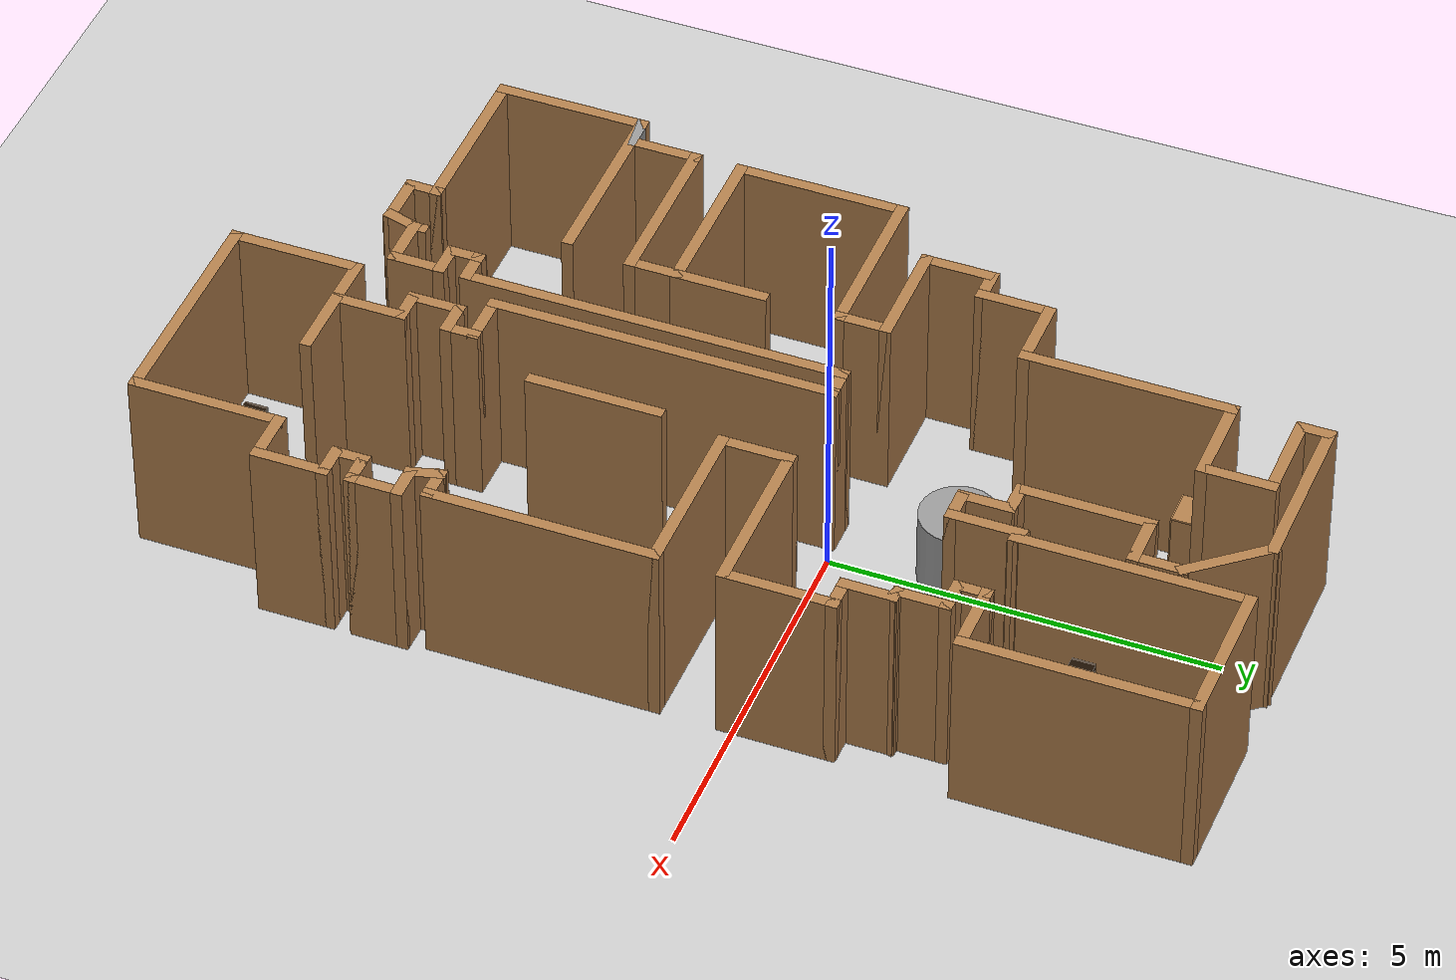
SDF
<sdf version="1.7">
 <world name="default">
  <light name="sun" type="directional">
   <pose>0 0 10 0 -0 0</pose>
   <diffuse>0.8 0.8 0.8 1</diffuse>
   <specular>0.2 0.2 0.2 1</specular>
   <attenuation>
    <range>1000</range>
    <constant>0.9</constant>
    <linear>0.01</linear>
    <quadratic>0.001</quadratic>
   </attenuation>
   <direction>-0.5 0.1 -0.9</direction>
   <spot><inner_angle>0</inner_angle><outer_angle>0</outer_angle><falloff>0</falloff></spot>
  </light>
  <model name="ground_plane">
   <static>1</static>
   <link name="link">
    <collision name="collision">
     <geometry><plane><normal>0 0 1</normal><size>100 100</size></plane></geometry>
     <surface><friction><ode><mu>100</mu><mu2>50</mu2></ode></friction></surface>
    </collision>
    <visual name="visual">
     <cast_shadows>0</cast_shadows>
     <geometry><plane><normal>0 0 1</normal><size>100 100</size></plane></geometry>
     <material>
      <script><uri>file://media/materials/scripts/gazebo.material</uri><name>Gazebo/Grey</name></script>
     </material>
    </visual>
   </link>
  </model>
  <gravity>0 0 -9.8</gravity>
  <magnetic_field>6e-06 2.3e-05 -4.2e-05</magnetic_field>
  <atmosphere type="adiabatic"/>
  <physics name="default_physics" default="0" type="ode">
   <max_step_size>0.001</max_step_size>
   <real_time_factor>1</real_time_factor>
   <real_time_update_rate>1000</real_time_update_rate>
  </physics>
  <scene><ambient>0.4 0.4 0.4 1</ambient><background>0.7 0.7 0.7 1</background><shadows>1</shadows></scene>
  <spherical_coordinates>
   <surface_model>EARTH_WGS84</surface_model>
   <latitude_deg>0</latitude_deg>
   <longitude_deg>0</longitude_deg>
   <elevation>0</elevation>
   <heading_deg>0</heading_deg>
  </spherical_coordinates>
  <model name="map_42">
   <link name="Wall_0">
    <pose>-0.25 6.70969 0 0 -0 3.14159</pose>
    <visual name="Wall_0_Visual">
     <pose>0 0 1.25 0 -0 0</pose>
     <geometry><box><size>2.25 0.15 2.5</size></box></geometry>
     <material>
      <script><uri>file://media/materials/scripts/gazebo.material</uri><name>Gazebo/Wood</name></script>
      <ambient>1 1 1 1</ambient>
      <shader type="pixel"/>
     </material>
     <meta><layer>0</layer></meta>
    </visual>
    <collision name="Wall_0_Collision">
     <pose>0 0 1.25 0 -0 0</pose>
     <geometry><box><size>2.25 0.15 2.5</size></box></geometry>
     <surface>
      <friction>
       <ode><mu>1</mu><mu2>1</mu2><fdir1>0 0 0</fdir1><slip1>0</slip1><slip2>0</slip2></ode>
       <torsional>
        <coefficient>1</coefficient>
        <patch_radius>0</patch_radius>
        <surface_radius>0</surface_radius>
        <use_patch_radius>1</use_patch_radius>
        <ode><slip>0</slip></ode>
       </torsional>
      </friction>
      <bounce><restitution_coefficient>0</restitution_coefficient><threshold>1e+06</threshold></bounce>
      <contact>
       <collide_without_contact>0</collide_without_contact>
       <collide_without_contact_bitmask>1</collide_without_contact_bitmask>
       <collide_bitmask>1</collide_bitmask>
       <ode>
        <soft_cfm>0</soft_cfm>
        <soft_erp>0.2</soft_erp>
        <kp>1e+13</kp>
        <kd>1</kd>
        <max_vel>0.01</max_vel>
        <min_depth>0</min_depth>
       </ode>
       <bullet>
        <split_impulse>1</split_impulse>
        <split_impulse_penetration_threshold>-0.01</split_impulse_penetration_threshold>
        <soft_cfm>0</soft_cfm>
        <soft_erp>0.2</soft_erp>
        <kp>1e+13</kp>
        <kd>1</kd>
       </bullet>
      </contact>
     </surface>
    </collision>
   </link>
   <link name="Wall_1">
    <pose>-1.3 6.53469 0 0 0 -1.5708</pose>
    <visual name="Wall_1_Visual">
     <pose>0 0 1.25 0 -0 0</pose>
     <geometry><box><size>0.5 0.15 2.5</size></box></geometry>
     <material>
      <script><uri>file://media/materials/scripts/gazebo.material</uri><name>Gazebo/Wood</name></script>
      <ambient>1 1 1 1</ambient>
      <shader type="pixel"/>
     </material>
     <meta><layer>0</layer></meta>
    </visual>
    <collision name="Wall_1_Collision">
     <pose>0 0 1.25 0 -0 0</pose>
     <geometry><box><size>0.5 0.15 2.5</size></box></geometry>
     <surface>
      <friction>
       <ode><mu>1</mu><mu2>1</mu2><fdir1>0 0 0</fdir1><slip1>0</slip1><slip2>0</slip2></ode>
       <torsional>
        <coefficient>1</coefficient>
        <patch_radius>0</patch_radius>
        <surface_radius>0</surface_radius>
        <use_patch_radius>1</use_patch_radius>
        <ode><slip>0</slip></ode>
       </torsional>
      </friction>
      <bounce><restitution_coefficient>0</restitution_coefficient><threshold>1e+06</threshold></bounce>
      <contact>
       <collide_without_contact>0</collide_without_contact>
       <collide_without_contact_bitmask>1</collide_without_contact_bitmask>
       <collide_bitmask>1</collide_bitmask>
       <ode>
        <soft_cfm>0</soft_cfm>
        <soft_erp>0.2</soft_erp>
        <kp>1e+13</kp>
        <kd>1</kd>
        <max_vel>0.01</max_vel>
        <min_depth>0</min_depth>
       </ode>
       <bullet>
        <split_impulse>1</split_impulse>
        <split_impulse_penetration_threshold>-0.01</split_impulse_penetration_threshold>
        <soft_cfm>0</soft_cfm>
        <soft_erp>0.2</soft_erp>
        <kp>1e+13</kp>
        <kd>1</kd>
       </bullet>
      </contact>
     </surface>
    </collision>
   </link>
   <link name="Wall_10">
    <pose>-2.325 2.05969 0 0 -0 3.14159</pose>
    <visual name="Wall_10_Visual">
     <pose>0 0 1.25 0 -0 0</pose>
     <geometry><box><size>0.5 0.15 2.5</size></box></geometry>
     <material>
      <script><uri>file://media/materials/scripts/gazebo.material</uri><name>Gazebo/Wood</name></script>
      <ambient>1 1 1 1</ambient>
      <shader type="pixel"/>
     </material>
     <meta><layer>0</layer></meta>
    </visual>
    <collision name="Wall_10_Collision">
     <pose>0 0 1.25 0 -0 0</pose>
     <geometry><box><size>0.5 0.15 2.5</size></box></geometry>
     <surface>
      <friction>
       <ode><mu>1</mu><mu2>1</mu2><fdir1>0 0 0</fdir1><slip1>0</slip1><slip2>0</slip2></ode>
       <torsional>
        <coefficient>1</coefficient>
        <patch_radius>0</patch_radius>
        <surface_radius>0</surface_radius>
        <use_patch_radius>1</use_patch_radius>
        <ode><slip>0</slip></ode>
       </torsional>
      </friction>
      <bounce><restitution_coefficient>0</restitution_coefficient><threshold>1e+06</threshold></bounce>
      <contact>
       <collide_without_contact>0</collide_without_contact>
       <collide_without_contact_bitmask>1</collide_without_contact_bitmask>
       <collide_bitmask>1</collide_bitmask>
       <ode>
        <soft_cfm>0</soft_cfm>
        <soft_erp>0.2</soft_erp>
        <kp>1e+13</kp>
        <kd>1</kd>
        <max_vel>0.01</max_vel>
        <min_depth>0</min_depth>
       </ode>
       <bullet>
        <split_impulse>1</split_impulse>
        <split_impulse_penetration_threshold>-0.01</split_impulse_penetration_threshold>
        <soft_cfm>0</soft_cfm>
        <soft_erp>0.2</soft_erp>
        <kp>1e+13</kp>
        <kd>1</kd>
       </bullet>
      </contact>
     </surface>
    </collision>
   </link>
   <link name="Wall_100">
    <pose>1.26623 3.34952 0 0 -0 1.5708</pose>
    <visual name="Wall_100_Visual">
     <pose>0 0 1.25 0 -0 0</pose>
     <geometry><box><size>0.75 0.15 2.5</size></box></geometry>
     <material>
      <script><uri>file://media/materials/scripts/gazebo.material</uri><name>Gazebo/Wood</name></script>
      <ambient>1 1 1 1</ambient>
      <shader type="pixel"/>
     </material>
     <meta><layer>0</layer></meta>
    </visual>
    <collision name="Wall_100_Collision">
     <pose>0 0 1.25 0 -0 0</pose>
     <geometry><box><size>0.75 0.15 2.5</size></box></geometry>
     <surface>
      <friction>
       <ode><mu>1</mu><mu2>1</mu2><fdir1>0 0 0</fdir1><slip1>0</slip1><slip2>0</slip2></ode>
       <torsional>
        <coefficient>1</coefficient>
        <patch_radius>0</patch_radius>
        <surface_radius>0</surface_radius>
        <use_patch_radius>1</use_patch_radius>
        <ode><slip>0</slip></ode>
       </torsional>
      </friction>
      <bounce><restitution_coefficient>0</restitution_coefficient><threshold>1e+06</threshold></bounce>
      <contact>
       <collide_without_contact>0</collide_without_contact>
       <collide_without_contact_bitmask>1</collide_without_contact_bitmask>
       <collide_bitmask>1</collide_bitmask>
       <ode>
        <soft_cfm>0</soft_cfm>
        <soft_erp>0.2</soft_erp>
        <kp>1e+13</kp>
        <kd>1</kd>
        <max_vel>0.01</max_vel>
        <min_depth>0</min_depth>
       </ode>
       <bullet>
        <split_impulse>1</split_impulse>
        <split_impulse_penetration_threshold>-0.01</split_impulse_penetration_threshold>
        <soft_cfm>0</soft_cfm>
        <soft_erp>0.2</soft_erp>
        <kp>1e+13</kp>
        <kd>1</kd>
       </bullet>
      </contact>
     </surface>
    </collision>
   </link>
   <link name="Wall_101">
    <pose>1.09123 3.64952 0 0 -0 3.14159</pose>
    <visual name="Wall_101_Visual">
     <pose>0 0 1.25 0 -0 0</pose>
     <geometry><box><size>0.5 0.15 2.5</size></box></geometry>
     <material>
      <script><uri>file://media/materials/scripts/gazebo.material</uri><name>Gazebo/Wood</name></script>
      <ambient>1 1 1 1</ambient>
      <shader type="pixel"/>
     </material>
     <meta><layer>0</layer></meta>
    </visual>
    <collision name="Wall_101_Collision">
     <pose>0 0 1.25 0 -0 0</pose>
     <geometry><box><size>0.5 0.15 2.5</size></box></geometry>
     <surface>
      <friction>
       <ode><mu>1</mu><mu2>1</mu2><fdir1>0 0 0</fdir1><slip1>0</slip1><slip2>0</slip2></ode>
       <torsional>
        <coefficient>1</coefficient>
        <patch_radius>0</patch_radius>
        <surface_radius>0</surface_radius>
        <use_patch_radius>1</use_patch_radius>
        <ode><slip>0</slip></ode>
       </torsional>
      </friction>
      <bounce><restitution_coefficient>0</restitution_coefficient><threshold>1e+06</threshold></bounce>
      <contact>
       <collide_without_contact>0</collide_without_contact>
       <collide_without_contact_bitmask>1</collide_without_contact_bitmask>
       <collide_bitmask>1</collide_bitmask>
       <ode>
        <soft_cfm>0</soft_cfm>
        <soft_erp>0.2</soft_erp>
        <kp>1e+13</kp>
        <kd>1</kd>
        <max_vel>0.01</max_vel>
        <min_depth>0</min_depth>
       </ode>
       <bullet>
        <split_impulse>1</split_impulse>
        <split_impulse_penetration_threshold>-0.01</split_impulse_penetration_threshold>
        <soft_cfm>0</soft_cfm>
        <soft_erp>0.2</soft_erp>
        <kp>1e+13</kp>
        <kd>1</kd>
       </bullet>
      </contact>
     </surface>
    </collision>
   </link>
   <link name="Wall_102">
    <pose>0.916228 4.44953 0 0 -0 1.5708</pose>
    <visual name="Wall_102_Visual">
     <pose>0 0 1.25 0 -0 0</pose>
     <geometry><box><size>1.75 0.15 2.5</size></box></geometry>
     <material>
      <script><uri>file://media/materials/scripts/gazebo.material</uri><name>Gazebo/Wood</name></script>
      <ambient>1 1 1 1</ambient>
      <shader type="pixel"/>
     </material>
     <meta><layer>0</layer></meta>
    </visual>
    <collision name="Wall_102_Collision">
     <pose>0 0 1.25 0 -0 0</pose>
     <geometry><box><size>1.75 0.15 2.5</size></box></geometry>
     <surface>
      <friction>
       <ode><mu>1</mu><mu2>1</mu2><fdir1>0 0 0</fdir1><slip1>0</slip1><slip2>0</slip2></ode>
       <torsional>
        <coefficient>1</coefficient>
        <patch_radius>0</patch_radius>
        <surface_radius>0</surface_radius>
        <use_patch_radius>1</use_patch_radius>
        <ode><slip>0</slip></ode>
       </torsional>
      </friction>
      <bounce><restitution_coefficient>0</restitution_coefficient><threshold>1e+06</threshold></bounce>
      <contact>
       <collide_without_contact>0</collide_without_contact>
       <collide_without_contact_bitmask>1</collide_without_contact_bitmask>
       <collide_bitmask>1</collide_bitmask>
       <ode>
        <soft_cfm>0</soft_cfm>
        <soft_erp>0.2</soft_erp>
        <kp>1e+13</kp>
        <kd>1</kd>
        <max_vel>0.01</max_vel>
        <min_depth>0</min_depth>
       </ode>
       <bullet>
        <split_impulse>1</split_impulse>
        <split_impulse_penetration_threshold>-0.01</split_impulse_penetration_threshold>
        <soft_cfm>0</soft_cfm>
        <soft_erp>0.2</soft_erp>
        <kp>1e+13</kp>
        <kd>1</kd>
       </bullet>
      </contact>
     </surface>
    </collision>
   </link>
   <link name="Wall_105">
    <pose>1.21623 5.24953 0 0 -0 0</pose>
    <visual name="Wall_105_Visual">
     <pose>0 0 1.25 0 -0 0</pose>
     <geometry><box><size>0.75 0.15 2.5</size></box></geometry>
     <material>
      <script><uri>file://media/materials/scripts/gazebo.material</uri><name>Gazebo/Wood</name></script>
      <ambient>1 1 1 1</ambient>
      <shader type="pixel"/>
     </material>
     <meta><layer>0</layer></meta>
    </visual>
    <collision name="Wall_105_Collision">
     <pose>0 0 1.25 0 -0 0</pose>
     <geometry><box><size>0.75 0.15 2.5</size></box></geometry>
     <surface>
      <friction>
       <ode><mu>1</mu><mu2>1</mu2><fdir1>0 0 0</fdir1><slip1>0</slip1><slip2>0</slip2></ode>
       <torsional>
        <coefficient>1</coefficient>
        <patch_radius>0</patch_radius>
        <surface_radius>0</surface_radius>
        <use_patch_radius>1</use_patch_radius>
        <ode><slip>0</slip></ode>
       </torsional>
      </friction>
      <bounce><restitution_coefficient>0</restitution_coefficient><threshold>1e+06</threshold></bounce>
      <contact>
       <collide_without_contact>0</collide_without_contact>
       <collide_without_contact_bitmask>1</collide_without_contact_bitmask>
       <collide_bitmask>1</collide_bitmask>
       <ode>
        <soft_cfm>0</soft_cfm>
        <soft_erp>0.2</soft_erp>
        <kp>1e+13</kp>
        <kd>1</kd>
        <max_vel>0.01</max_vel>
        <min_depth>0</min_depth>
       </ode>
       <bullet>
        <split_impulse>1</split_impulse>
        <split_impulse_penetration_threshold>-0.01</split_impulse_penetration_threshold>
        <soft_cfm>0</soft_cfm>
        <soft_erp>0.2</soft_erp>
        <kp>1e+13</kp>
        <kd>1</kd>
       </bullet>
      </contact>
     </surface>
    </collision>
   </link>
   <link name="Wall_106">
    <pose>1.51623 5.54953 0 0 -0 1.5708</pose>
    <visual name="Wall_106_Visual">
     <pose>0 0 1.25 0 -0 0</pose>
     <geometry><box><size>0.75 0.15 2.5</size></box></geometry>
     <material>
      <script><uri>file://media/materials/scripts/gazebo.material</uri><name>Gazebo/Wood</name></script>
      <ambient>1 1 1 1</ambient>
      <shader type="pixel"/>
     </material>
     <meta><layer>0</layer></meta>
    </visual>
    <collision name="Wall_106_Collision">
     <pose>0 0 1.25 0 -0 0</pose>
     <geometry><box><size>0.75 0.15 2.5</size></box></geometry>
     <surface>
      <friction>
       <ode><mu>1</mu><mu2>1</mu2><fdir1>0 0 0</fdir1><slip1>0</slip1><slip2>0</slip2></ode>
       <torsional>
        <coefficient>1</coefficient>
        <patch_radius>0</patch_radius>
        <surface_radius>0</surface_radius>
        <use_patch_radius>1</use_patch_radius>
        <ode><slip>0</slip></ode>
       </torsional>
      </friction>
      <bounce><restitution_coefficient>0</restitution_coefficient><threshold>1e+06</threshold></bounce>
      <contact>
       <collide_without_contact>0</collide_without_contact>
       <collide_without_contact_bitmask>1</collide_without_contact_bitmask>
       <collide_bitmask>1</collide_bitmask>
       <ode>
        <soft_cfm>0</soft_cfm>
        <soft_erp>0.2</soft_erp>
        <kp>1e+13</kp>
        <kd>1</kd>
        <max_vel>0.01</max_vel>
        <min_depth>0</min_depth>
       </ode>
       <bullet>
        <split_impulse>1</split_impulse>
        <split_impulse_penetration_threshold>-0.01</split_impulse_penetration_threshold>
        <soft_cfm>0</soft_cfm>
        <soft_erp>0.2</soft_erp>
        <kp>1e+13</kp>
        <kd>1</kd>
       </bullet>
      </contact>
     </surface>
    </collision>
   </link>
   <link name="Wall_107">
    <pose>1.15811 6.27961 0 0 -0 2.26514</pose>
    <visual name="Wall_107_Visual">
     <pose>0 0 1.25 0 -0 0</pose>
     <geometry><box><size>1.26931 0.15 2.5</size></box></geometry>
     <material>
      <script><uri>file://media/materials/scripts/gazebo.material</uri><name>Gazebo/Wood</name></script>
      <ambient>1 1 1 1</ambient>
      <shader type="pixel"/>
     </material>
     <meta><layer>0</layer></meta>
    </visual>
    <collision name="Wall_107_Collision">
     <pose>0 0 1.25 0 -0 0</pose>
     <geometry><box><size>1.26931 0.15 2.5</size></box></geometry>
     <surface>
      <friction>
       <ode><mu>1</mu><mu2>1</mu2><fdir1>0 0 0</fdir1><slip1>0</slip1><slip2>0</slip2></ode>
       <torsional>
        <coefficient>1</coefficient>
        <patch_radius>0</patch_radius>
        <surface_radius>0</surface_radius>
        <use_patch_radius>1</use_patch_radius>
        <ode><slip>0</slip></ode>
       </torsional>
      </friction>
      <bounce><restitution_coefficient>0</restitution_coefficient><threshold>1e+06</threshold></bounce>
      <contact>
       <collide_without_contact>0</collide_without_contact>
       <collide_without_contact_bitmask>1</collide_without_contact_bitmask>
       <collide_bitmask>1</collide_bitmask>
       <ode>
        <soft_cfm>0</soft_cfm>
        <soft_erp>0.2</soft_erp>
        <kp>1e+13</kp>
        <kd>1</kd>
        <max_vel>0.01</max_vel>
        <min_depth>0</min_depth>
       </ode>
       <bullet>
        <split_impulse>1</split_impulse>
        <split_impulse_penetration_threshold>-0.01</split_impulse_penetration_threshold>
        <soft_cfm>0</soft_cfm>
        <soft_erp>0.2</soft_erp>
        <kp>1e+13</kp>
        <kd>1</kd>
       </bullet>
      </contact>
     </surface>
    </collision>
   </link>
   <link name="Wall_11">
    <pose>-2.5 1.63469 0 0 0 -1.5708</pose>
    <visual name="Wall_11_Visual">
     <pose>0 0 1.25 0 -0 0</pose>
     <geometry><box><size>1 0.15 2.5</size></box></geometry>
     <material>
      <script><uri>file://media/materials/scripts/gazebo.material</uri><name>Gazebo/Wood</name></script>
      <ambient>1 1 1 1</ambient>
      <shader type="pixel"/>
     </material>
     <meta><layer>0</layer></meta>
    </visual>
    <collision name="Wall_11_Collision">
     <pose>0 0 1.25 0 -0 0</pose>
     <geometry><box><size>1 0.15 2.5</size></box></geometry>
     <surface>
      <friction>
       <ode><mu>1</mu><mu2>1</mu2><fdir1>0 0 0</fdir1><slip1>0</slip1><slip2>0</slip2></ode>
       <torsional>
        <coefficient>1</coefficient>
        <patch_radius>0</patch_radius>
        <surface_radius>0</surface_radius>
        <use_patch_radius>1</use_patch_radius>
        <ode><slip>0</slip></ode>
       </torsional>
      </friction>
      <bounce><restitution_coefficient>0</restitution_coefficient><threshold>1e+06</threshold></bounce>
      <contact>
       <collide_without_contact>0</collide_without_contact>
       <collide_without_contact_bitmask>1</collide_without_contact_bitmask>
       <collide_bitmask>1</collide_bitmask>
       <ode>
        <soft_cfm>0</soft_cfm>
        <soft_erp>0.2</soft_erp>
        <kp>1e+13</kp>
        <kd>1</kd>
        <max_vel>0.01</max_vel>
        <min_depth>0</min_depth>
       </ode>
       <bullet>
        <split_impulse>1</split_impulse>
        <split_impulse_penetration_threshold>-0.01</split_impulse_penetration_threshold>
        <soft_cfm>0</soft_cfm>
        <soft_erp>0.2</soft_erp>
        <kp>1e+13</kp>
        <kd>1</kd>
       </bullet>
      </contact>
     </surface>
    </collision>
   </link>
   <link name="Wall_111">
    <pose>1.22826 -1.58492 0 0 0 -1.5708</pose>
    <visual name="Wall_111_Visual">
     <pose>0 0 1.25 0 -0 0</pose>
     <geometry><box><size>1.75 0.15 2.5</size></box></geometry>
     <material>
      <script><uri>file://media/materials/scripts/gazebo.material</uri><name>Gazebo/Wood</name></script>
      <ambient>1 1 1 1</ambient>
      <shader type="pixel"/>
     </material>
     <meta><layer>0</layer></meta>
    </visual>
    <collision name="Wall_111_Collision">
     <pose>0 0 1.25 0 -0 0</pose>
     <geometry><box><size>1.75 0.15 2.5</size></box></geometry>
     <surface>
      <friction>
       <ode><mu>1</mu><mu2>1</mu2><fdir1>0 0 0</fdir1><slip1>0</slip1><slip2>0</slip2></ode>
       <torsional>
        <coefficient>1</coefficient>
        <patch_radius>0</patch_radius>
        <surface_radius>0</surface_radius>
        <use_patch_radius>1</use_patch_radius>
        <ode><slip>0</slip></ode>
       </torsional>
      </friction>
      <bounce><restitution_coefficient>0</restitution_coefficient><threshold>1e+06</threshold></bounce>
      <contact>
       <collide_without_contact>0</collide_without_contact>
       <collide_without_contact_bitmask>1</collide_without_contact_bitmask>
       <collide_bitmask>1</collide_bitmask>
       <ode>
        <soft_cfm>0</soft_cfm>
        <soft_erp>0.2</soft_erp>
        <kp>1e+13</kp>
        <kd>1</kd>
        <max_vel>0.01</max_vel>
        <min_depth>0</min_depth>
       </ode>
       <bullet>
        <split_impulse>1</split_impulse>
        <split_impulse_penetration_threshold>-0.01</split_impulse_penetration_threshold>
        <soft_cfm>0</soft_cfm>
        <soft_erp>0.2</soft_erp>
        <kp>1e+13</kp>
        <kd>1</kd>
       </bullet>
      </contact>
     </surface>
    </collision>
   </link>
   <link name="Wall_113">
    <pose>-2.425 -2.94031 0 0 -0 0</pose>
    <visual name="Wall_113_Visual">
     <pose>0 0 1.25 0 -0 0</pose>
     <geometry><box><size>2.5 0.15 2.5</size></box></geometry>
     <material>
      <script><uri>file://media/materials/scripts/gazebo.material</uri><name>Gazebo/Wood</name></script>
      <ambient>1 1 1 1</ambient>
      <shader type="pixel"/>
     </material>
     <meta><layer>0</layer></meta>
    </visual>
    <collision name="Wall_113_Collision">
     <pose>0 0 1.25 0 -0 0</pose>
     <geometry><box><size>2.5 0.15 2.5</size></box></geometry>
     <surface>
      <friction>
       <ode><mu>1</mu><mu2>1</mu2><fdir1>0 0 0</fdir1><slip1>0</slip1><slip2>0</slip2></ode>
       <torsional>
        <coefficient>1</coefficient>
        <patch_radius>0</patch_radius>
        <surface_radius>0</surface_radius>
        <use_patch_radius>1</use_patch_radius>
        <ode><slip>0</slip></ode>
       </torsional>
      </friction>
      <bounce><restitution_coefficient>0</restitution_coefficient><threshold>1e+06</threshold></bounce>
      <contact>
       <collide_without_contact>0</collide_without_contact>
       <collide_without_contact_bitmask>1</collide_without_contact_bitmask>
       <collide_bitmask>1</collide_bitmask>
       <ode>
        <soft_cfm>0</soft_cfm>
        <soft_erp>0.2</soft_erp>
        <kp>1e+13</kp>
        <kd>1</kd>
        <max_vel>0.01</max_vel>
        <min_depth>0</min_depth>
       </ode>
       <bullet>
        <split_impulse>1</split_impulse>
        <split_impulse_penetration_threshold>-0.01</split_impulse_penetration_threshold>
        <soft_cfm>0</soft_cfm>
        <soft_erp>0.2</soft_erp>
        <kp>1e+13</kp>
        <kd>1</kd>
       </bullet>
      </contact>
     </surface>
    </collision>
   </link>
   <link name="Wall_14">
    <pose>-1.825 1.20969 0 0 -0 0</pose>
    <visual name="Wall_14_Visual">
     <pose>0 0 1.25 0 -0 0</pose>
     <geometry><box><size>1.5 0.15 2.5</size></box></geometry>
     <material>
      <script><uri>file://media/materials/scripts/gazebo.material</uri><name>Gazebo/Wood</name></script>
      <ambient>1 1 1 1</ambient>
      <shader type="pixel"/>
     </material>
     <meta><layer>0</layer></meta>
    </visual>
    <collision name="Wall_14_Collision">
     <pose>0 0 1.25 0 -0 0</pose>
     <geometry><box><size>1.5 0.15 2.5</size></box></geometry>
     <surface>
      <friction>
       <ode><mu>1</mu><mu2>1</mu2><fdir1>0 0 0</fdir1><slip1>0</slip1><slip2>0</slip2></ode>
       <torsional>
        <coefficient>1</coefficient>
        <patch_radius>0</patch_radius>
        <surface_radius>0</surface_radius>
        <use_patch_radius>1</use_patch_radius>
        <ode><slip>0</slip></ode>
       </torsional>
      </friction>
      <bounce><restitution_coefficient>0</restitution_coefficient><threshold>1e+06</threshold></bounce>
      <contact>
       <collide_without_contact>0</collide_without_contact>
       <collide_without_contact_bitmask>1</collide_without_contact_bitmask>
       <collide_bitmask>1</collide_bitmask>
       <ode>
        <soft_cfm>0</soft_cfm>
        <soft_erp>0.2</soft_erp>
        <kp>1e+13</kp>
        <kd>1</kd>
        <max_vel>0.01</max_vel>
        <min_depth>0</min_depth>
       </ode>
       <bullet>
        <split_impulse>1</split_impulse>
        <split_impulse_penetration_threshold>-0.01</split_impulse_penetration_threshold>
        <soft_cfm>0</soft_cfm>
        <soft_erp>0.2</soft_erp>
        <kp>1e+13</kp>
        <kd>1</kd>
       </bullet>
      </contact>
     </surface>
    </collision>
   </link>
   <link name="Wall_15">
    <pose>-1.15 0.909687 0 0 0 -1.5708</pose>
    <visual name="Wall_15_Visual">
     <pose>0 0 1.25 0 -0 0</pose>
     <geometry><box><size>0.75 0.15 2.5</size></box></geometry>
     <material>
      <script><uri>file://media/materials/scripts/gazebo.material</uri><name>Gazebo/Wood</name></script>
      <ambient>1 1 1 1</ambient>
      <shader type="pixel"/>
     </material>
     <meta><layer>0</layer></meta>
    </visual>
    <collision name="Wall_15_Collision">
     <pose>0 0 1.25 0 -0 0</pose>
     <geometry><box><size>0.75 0.15 2.5</size></box></geometry>
     <surface>
      <friction>
       <ode><mu>1</mu><mu2>1</mu2><fdir1>0 0 0</fdir1><slip1>0</slip1><slip2>0</slip2></ode>
       <torsional>
        <coefficient>1</coefficient>
        <patch_radius>0</patch_radius>
        <surface_radius>0</surface_radius>
        <use_patch_radius>1</use_patch_radius>
        <ode><slip>0</slip></ode>
       </torsional>
      </friction>
      <bounce><restitution_coefficient>0</restitution_coefficient><threshold>1e+06</threshold></bounce>
      <contact>
       <collide_without_contact>0</collide_without_contact>
       <collide_without_contact_bitmask>1</collide_without_contact_bitmask>
       <collide_bitmask>1</collide_bitmask>
       <ode>
        <soft_cfm>0</soft_cfm>
        <soft_erp>0.2</soft_erp>
        <kp>1e+13</kp>
        <kd>1</kd>
        <max_vel>0.01</max_vel>
        <min_depth>0</min_depth>
       </ode>
       <bullet>
        <split_impulse>1</split_impulse>
        <split_impulse_penetration_threshold>-0.01</split_impulse_penetration_threshold>
        <soft_cfm>0</soft_cfm>
        <soft_erp>0.2</soft_erp>
        <kp>1e+13</kp>
        <kd>1</kd>
       </bullet>
      </contact>
     </surface>
    </collision>
   </link>
   <link name="Wall_16">
    <pose>-2.2 0.609687 0 0 -0 3.14159</pose>
    <visual name="Wall_16_Visual">
     <pose>0 0 1.25 0 -0 0</pose>
     <geometry><box><size>2.25 0.15 2.5</size></box></geometry>
     <material>
      <script><uri>file://media/materials/scripts/gazebo.material</uri><name>Gazebo/Wood</name></script>
      <ambient>1 1 1 1</ambient>
      <shader type="pixel"/>
     </material>
     <meta><layer>0</layer></meta>
    </visual>
    <collision name="Wall_16_Collision">
     <pose>0 0 1.25 0 -0 0</pose>
     <geometry><box><size>2.25 0.15 2.5</size></box></geometry>
     <surface>
      <friction>
       <ode><mu>1</mu><mu2>1</mu2><fdir1>0 0 0</fdir1><slip1>0</slip1><slip2>0</slip2></ode>
       <torsional>
        <coefficient>1</coefficient>
        <patch_radius>0</patch_radius>
        <surface_radius>0</surface_radius>
        <use_patch_radius>1</use_patch_radius>
        <ode><slip>0</slip></ode>
       </torsional>
      </friction>
      <bounce><restitution_coefficient>0</restitution_coefficient><threshold>1e+06</threshold></bounce>
      <contact>
       <collide_without_contact>0</collide_without_contact>
       <collide_without_contact_bitmask>1</collide_without_contact_bitmask>
       <collide_bitmask>1</collide_bitmask>
       <ode>
        <soft_cfm>0</soft_cfm>
        <soft_erp>0.2</soft_erp>
        <kp>1e+13</kp>
        <kd>1</kd>
        <max_vel>0.01</max_vel>
        <min_depth>0</min_depth>
       </ode>
       <bullet>
        <split_impulse>1</split_impulse>
        <split_impulse_penetration_threshold>-0.01</split_impulse_penetration_threshold>
        <soft_cfm>0</soft_cfm>
        <soft_erp>0.2</soft_erp>
        <kp>1e+13</kp>
        <kd>1</kd>
       </bullet>
      </contact>
     </surface>
    </collision>
   </link>
   <link name="Wall_17">
    <pose>-3.25 -0.440313 0 0 0 -1.5708</pose>
    <visual name="Wall_17_Visual">
     <pose>0 0 1.25 0 -0 0</pose>
     <geometry><box><size>2.25 0.15 2.5</size></box></geometry>
     <material>
      <script><uri>file://media/materials/scripts/gazebo.material</uri><name>Gazebo/Wood</name></script>
      <ambient>1 1 1 1</ambient>
      <shader type="pixel"/>
     </material>
     <meta><layer>0</layer></meta>
    </visual>
    <collision name="Wall_17_Collision">
     <pose>0 0 1.25 0 -0 0</pose>
     <geometry><box><size>2.25 0.15 2.5</size></box></geometry>
     <surface>
      <friction>
       <ode><mu>1</mu><mu2>1</mu2><fdir1>0 0 0</fdir1><slip1>0</slip1><slip2>0</slip2></ode>
       <torsional>
        <coefficient>1</coefficient>
        <patch_radius>0</patch_radius>
        <surface_radius>0</surface_radius>
        <use_patch_radius>1</use_patch_radius>
        <ode><slip>0</slip></ode>
       </torsional>
      </friction>
      <bounce><restitution_coefficient>0</restitution_coefficient><threshold>1e+06</threshold></bounce>
      <contact>
       <collide_without_contact>0</collide_without_contact>
       <collide_without_contact_bitmask>1</collide_without_contact_bitmask>
       <collide_bitmask>1</collide_bitmask>
       <ode>
        <soft_cfm>0</soft_cfm>
        <soft_erp>0.2</soft_erp>
        <kp>1e+13</kp>
        <kd>1</kd>
        <max_vel>0.01</max_vel>
        <min_depth>0</min_depth>
       </ode>
       <bullet>
        <split_impulse>1</split_impulse>
        <split_impulse_penetration_threshold>-0.01</split_impulse_penetration_threshold>
        <soft_cfm>0</soft_cfm>
        <soft_erp>0.2</soft_erp>
        <kp>1e+13</kp>
        <kd>1</kd>
       </bullet>
      </contact>
     </surface>
    </collision>
   </link>
   <link name="Wall_18">
    <pose>-2.2 -1.49031 0 0 -0 0</pose>
    <visual name="Wall_18_Visual">
     <pose>0 0 1.25 0 -0 0</pose>
     <geometry><box><size>2.25 0.15 2.5</size></box></geometry>
     <material>
      <script><uri>file://media/materials/scripts/gazebo.material</uri><name>Gazebo/Wood</name></script>
      <ambient>1 1 1 1</ambient>
      <shader type="pixel"/>
     </material>
     <meta><layer>0</layer></meta>
    </visual>
    <collision name="Wall_18_Collision">
     <pose>0 0 1.25 0 -0 0</pose>
     <geometry><box><size>2.25 0.15 2.5</size></box></geometry>
     <surface>
      <friction>
       <ode><mu>1</mu><mu2>1</mu2><fdir1>0 0 0</fdir1><slip1>0</slip1><slip2>0</slip2></ode>
       <torsional>
        <coefficient>1</coefficient>
        <patch_radius>0</patch_radius>
        <surface_radius>0</surface_radius>
        <use_patch_radius>1</use_patch_radius>
        <ode><slip>0</slip></ode>
       </torsional>
      </friction>
      <bounce><restitution_coefficient>0</restitution_coefficient><threshold>1e+06</threshold></bounce>
      <contact>
       <collide_without_contact>0</collide_without_contact>
       <collide_without_contact_bitmask>1</collide_without_contact_bitmask>
       <collide_bitmask>1</collide_bitmask>
       <ode>
        <soft_cfm>0</soft_cfm>
        <soft_erp>0.2</soft_erp>
        <kp>1e+13</kp>
        <kd>1</kd>
        <max_vel>0.01</max_vel>
        <min_depth>0</min_depth>
       </ode>
       <bullet>
        <split_impulse>1</split_impulse>
        <split_impulse_penetration_threshold>-0.01</split_impulse_penetration_threshold>
        <soft_cfm>0</soft_cfm>
        <soft_erp>0.2</soft_erp>
        <kp>1e+13</kp>
        <kd>1</kd>
       </bullet>
      </contact>
     </surface>
    </collision>
   </link>
   <link name="Wall_19">
    <pose>-1.15 -0.940313 0 0 -0 1.5708</pose>
    <visual name="Wall_19_Visual">
     <pose>0 0 1.25 0 -0 0</pose>
     <geometry><box><size>1.25 0.15 2.5</size></box></geometry>
     <material>
      <script><uri>file://media/materials/scripts/gazebo.material</uri><name>Gazebo/Wood</name></script>
      <ambient>1 1 1 1</ambient>
      <shader type="pixel"/>
     </material>
     <meta><layer>0</layer></meta>
    </visual>
    <collision name="Wall_19_Collision">
     <pose>0 0 1.25 0 -0 0</pose>
     <geometry><box><size>1.25 0.15 2.5</size></box></geometry>
     <surface>
      <friction>
       <ode><mu>1</mu><mu2>1</mu2><fdir1>0 0 0</fdir1><slip1>0</slip1><slip2>0</slip2></ode>
       <torsional>
        <coefficient>1</coefficient>
        <patch_radius>0</patch_radius>
        <surface_radius>0</surface_radius>
        <use_patch_radius>1</use_patch_radius>
        <ode><slip>0</slip></ode>
       </torsional>
      </friction>
      <bounce><restitution_coefficient>0</restitution_coefficient><threshold>1e+06</threshold></bounce>
      <contact>
       <collide_without_contact>0</collide_without_contact>
       <collide_without_contact_bitmask>1</collide_without_contact_bitmask>
       <collide_bitmask>1</collide_bitmask>
       <ode>
        <soft_cfm>0</soft_cfm>
        <soft_erp>0.2</soft_erp>
        <kp>1e+13</kp>
        <kd>1</kd>
        <max_vel>0.01</max_vel>
        <min_depth>0</min_depth>
       </ode>
       <bullet>
        <split_impulse>1</split_impulse>
        <split_impulse_penetration_threshold>-0.01</split_impulse_penetration_threshold>
        <soft_cfm>0</soft_cfm>
        <soft_erp>0.2</soft_erp>
        <kp>1e+13</kp>
        <kd>1</kd>
       </bullet>
      </contact>
     </surface>
    </collision>
   </link>
   <link name="Wall_21">
    <pose>-1.15 -1.79031 0 0 0 -1.5708</pose>
    <visual name="Wall_21_Visual">
     <pose>0 0 1.25 0 -0 0</pose>
     <geometry><box><size>0.75 0.15 2.5</size></box></geometry>
     <material>
      <script><uri>file://media/materials/scripts/gazebo.material</uri><name>Gazebo/Wood</name></script>
      <ambient>1 1 1 1</ambient>
      <shader type="pixel"/>
     </material>
     <meta><layer>0</layer></meta>
    </visual>
    <collision name="Wall_21_Collision">
     <pose>0 0 1.25 0 -0 0</pose>
     <geometry><box><size>0.75 0.15 2.5</size></box></geometry>
     <surface>
      <friction>
       <ode><mu>1</mu><mu2>1</mu2><fdir1>0 0 0</fdir1><slip1>0</slip1><slip2>0</slip2></ode>
       <torsional>
        <coefficient>1</coefficient>
        <patch_radius>0</patch_radius>
        <surface_radius>0</surface_radius>
        <use_patch_radius>1</use_patch_radius>
        <ode><slip>0</slip></ode>
       </torsional>
      </friction>
      <bounce><restitution_coefficient>0</restitution_coefficient><threshold>1e+06</threshold></bounce>
      <contact>
       <collide_without_contact>0</collide_without_contact>
       <collide_without_contact_bitmask>1</collide_without_contact_bitmask>
       <collide_bitmask>1</collide_bitmask>
       <ode>
        <soft_cfm>0</soft_cfm>
        <soft_erp>0.2</soft_erp>
        <kp>1e+13</kp>
        <kd>1</kd>
        <max_vel>0.01</max_vel>
        <min_depth>0</min_depth>
       </ode>
       <bullet>
        <split_impulse>1</split_impulse>
        <split_impulse_penetration_threshold>-0.01</split_impulse_penetration_threshold>
        <soft_cfm>0</soft_cfm>
        <soft_erp>0.2</soft_erp>
        <kp>1e+13</kp>
        <kd>1</kd>
       </bullet>
      </contact>
     </surface>
    </collision>
   </link>
   <link name="Wall_22">
    <pose>-2.2 -2.09031 0 0 -0 3.14159</pose>
    <visual name="Wall_22_Visual">
     <pose>0 0 1.25 0 -0 0</pose>
     <geometry><box><size>2.25 0.15 2.5</size></box></geometry>
     <material>
      <script><uri>file://media/materials/scripts/gazebo.material</uri><name>Gazebo/Wood</name></script>
      <ambient>1 1 1 1</ambient>
      <shader type="pixel"/>
     </material>
     <meta><layer>0</layer></meta>
    </visual>
    <collision name="Wall_22_Collision">
     <pose>0 0 1.25 0 -0 0</pose>
     <geometry><box><size>2.25 0.15 2.5</size></box></geometry>
     <surface>
      <friction>
       <ode><mu>1</mu><mu2>1</mu2><fdir1>0 0 0</fdir1><slip1>0</slip1><slip2>0</slip2></ode>
       <torsional>
        <coefficient>1</coefficient>
        <patch_radius>0</patch_radius>
        <surface_radius>0</surface_radius>
        <use_patch_radius>1</use_patch_radius>
        <ode><slip>0</slip></ode>
       </torsional>
      </friction>
      <bounce><restitution_coefficient>0</restitution_coefficient><threshold>1e+06</threshold></bounce>
      <contact>
       <collide_without_contact>0</collide_without_contact>
       <collide_without_contact_bitmask>1</collide_without_contact_bitmask>
       <collide_bitmask>1</collide_bitmask>
       <ode>
        <soft_cfm>0</soft_cfm>
        <soft_erp>0.2</soft_erp>
        <kp>1e+13</kp>
        <kd>1</kd>
        <max_vel>0.01</max_vel>
        <min_depth>0</min_depth>
       </ode>
       <bullet>
        <split_impulse>1</split_impulse>
        <split_impulse_penetration_threshold>-0.01</split_impulse_penetration_threshold>
        <soft_cfm>0</soft_cfm>
        <soft_erp>0.2</soft_erp>
        <kp>1e+13</kp>
        <kd>1</kd>
       </bullet>
      </contact>
     </surface>
    </collision>
   </link>
   <link name="Wall_23">
    <pose>-3.25 -2.51531 0 0 0 -1.5708</pose>
    <visual name="Wall_23_Visual">
     <pose>0 0 1.25 0 -0 0</pose>
     <geometry><box><size>1 0.15 2.5</size></box></geometry>
     <material>
      <script><uri>file://media/materials/scripts/gazebo.material</uri><name>Gazebo/Wood</name></script>
      <ambient>1 1 1 1</ambient>
      <shader type="pixel"/>
     </material>
     <meta><layer>0</layer></meta>
    </visual>
    <collision name="Wall_23_Collision">
     <pose>0 0 1.25 0 -0 0</pose>
     <geometry><box><size>1 0.15 2.5</size></box></geometry>
     <surface>
      <friction>
       <ode><mu>1</mu><mu2>1</mu2><fdir1>0 0 0</fdir1><slip1>0</slip1><slip2>0</slip2></ode>
       <torsional>
        <coefficient>1</coefficient>
        <patch_radius>0</patch_radius>
        <surface_radius>0</surface_radius>
        <use_patch_radius>1</use_patch_radius>
        <ode><slip>0</slip></ode>
       </torsional>
      </friction>
      <bounce><restitution_coefficient>0</restitution_coefficient><threshold>1e+06</threshold></bounce>
      <contact>
       <collide_without_contact>0</collide_without_contact>
       <collide_without_contact_bitmask>1</collide_without_contact_bitmask>
       <collide_bitmask>1</collide_bitmask>
       <ode>
        <soft_cfm>0</soft_cfm>
        <soft_erp>0.2</soft_erp>
        <kp>1e+13</kp>
        <kd>1</kd>
        <max_vel>0.01</max_vel>
        <min_depth>0</min_depth>
       </ode>
       <bullet>
        <split_impulse>1</split_impulse>
        <split_impulse_penetration_threshold>-0.01</split_impulse_penetration_threshold>
        <soft_cfm>0</soft_cfm>
        <soft_erp>0.2</soft_erp>
        <kp>1e+13</kp>
        <kd>1</kd>
       </bullet>
      </contact>
     </surface>
    </collision>
   </link>
   <link name="Wall_33">
    <pose>-0.8 -4.74031 0 0 -0 1.5708</pose>
    <visual name="Wall_33_Visual">
     <pose>0 0 1.25 0 -0 0</pose>
     <geometry><box><size>0.25 0.15 2.5</size></box></geometry>
     <material>
      <script><uri>file://media/materials/scripts/gazebo.material</uri><name>Gazebo/Wood</name></script>
      <ambient>1 1 1 1</ambient>
      <shader type="pixel"/>
     </material>
     <meta><layer>0</layer></meta>
    </visual>
    <collision name="Wall_33_Collision">
     <pose>0 0 1.25 0 -0 0</pose>
     <geometry><box><size>0.25 0.15 2.5</size></box></geometry>
     <surface>
      <friction>
       <ode><mu>1</mu><mu2>1</mu2><fdir1>0 0 0</fdir1><slip1>0</slip1><slip2>0</slip2></ode>
       <torsional>
        <coefficient>1</coefficient>
        <patch_radius>0</patch_radius>
        <surface_radius>0</surface_radius>
        <use_patch_radius>1</use_patch_radius>
        <ode><slip>0</slip></ode>
       </torsional>
      </friction>
      <bounce><restitution_coefficient>0</restitution_coefficient><threshold>1e+06</threshold></bounce>
      <contact>
       <collide_without_contact>0</collide_without_contact>
       <collide_without_contact_bitmask>1</collide_without_contact_bitmask>
       <collide_bitmask>1</collide_bitmask>
       <ode>
        <soft_cfm>0</soft_cfm>
        <soft_erp>0.2</soft_erp>
        <kp>1e+13</kp>
        <kd>1</kd>
        <max_vel>0.01</max_vel>
        <min_depth>0</min_depth>
       </ode>
       <bullet>
        <split_impulse>1</split_impulse>
        <split_impulse_penetration_threshold>-0.01</split_impulse_penetration_threshold>
        <soft_cfm>0</soft_cfm>
        <soft_erp>0.2</soft_erp>
        <kp>1e+13</kp>
        <kd>1</kd>
       </bullet>
      </contact>
     </surface>
    </collision>
   </link>
   <link name="Wall_35">
    <pose>-3.425 -2.94031 0 0 -0 3.14159</pose>
    <visual name="Wall_35_Visual">
     <pose>0 0 1.25 0 -0 0</pose>
     <geometry><box><size>0.5 0.15 2.5</size></box></geometry>
     <material>
      <script><uri>file://media/materials/scripts/gazebo.material</uri><name>Gazebo/Grey</name></script>
      <ambient>1 1 1 1</ambient>
      <shader type="pixel"/>
     </material>
     <meta><layer>0</layer></meta>
    </visual>
    <collision name="Wall_35_Collision">
     <pose>0 0 1.25 0 -0 0</pose>
     <geometry><box><size>0.5 0.15 2.5</size></box></geometry>
     <surface>
      <friction>
       <ode><mu>1</mu><mu2>1</mu2><fdir1>0 0 0</fdir1><slip1>0</slip1><slip2>0</slip2></ode>
       <torsional>
        <coefficient>1</coefficient>
        <patch_radius>0</patch_radius>
        <surface_radius>0</surface_radius>
        <use_patch_radius>1</use_patch_radius>
        <ode><slip>0</slip></ode>
       </torsional>
      </friction>
      <bounce><restitution_coefficient>0</restitution_coefficient><threshold>1e+06</threshold></bounce>
      <contact>
       <collide_without_contact>0</collide_without_contact>
       <collide_without_contact_bitmask>1</collide_without_contact_bitmask>
       <collide_bitmask>1</collide_bitmask>
       <ode>
        <soft_cfm>0</soft_cfm>
        <soft_erp>0.2</soft_erp>
        <kp>1e+13</kp>
        <kd>1</kd>
        <max_vel>0.01</max_vel>
        <min_depth>0</min_depth>
       </ode>
       <bullet>
        <split_impulse>1</split_impulse>
        <split_impulse_penetration_threshold>-0.01</split_impulse_penetration_threshold>
        <soft_cfm>0</soft_cfm>
        <soft_erp>0.2</soft_erp>
        <kp>1e+13</kp>
        <kd>1</kd>
       </bullet>
      </contact>
     </surface>
    </collision>
   </link>
   <link name="Wall_36">
    <pose>-3.6 -3.86531 0 0 0 -1.5708</pose>
    <visual name="Wall_36_Visual">
     <pose>0 0 1.25 0 -0 0</pose>
     <geometry><box><size>2 0.15 2.5</size></box></geometry>
     <material>
      <script><uri>file://media/materials/scripts/gazebo.material</uri><name>Gazebo/Wood</name></script>
      <ambient>1 1 1 1</ambient>
      <shader type="pixel"/>
     </material>
     <meta><layer>0</layer></meta>
    </visual>
    <collision name="Wall_36_Collision">
     <pose>0 0 1.25 0 -0 0</pose>
     <geometry><box><size>2 0.15 2.5</size></box></geometry>
     <surface>
      <friction>
       <ode><mu>1</mu><mu2>1</mu2><fdir1>0 0 0</fdir1><slip1>0</slip1><slip2>0</slip2></ode>
       <torsional>
        <coefficient>1</coefficient>
        <patch_radius>0</patch_radius>
        <surface_radius>0</surface_radius>
        <use_patch_radius>1</use_patch_radius>
        <ode><slip>0</slip></ode>
       </torsional>
      </friction>
      <bounce><restitution_coefficient>0</restitution_coefficient><threshold>1e+06</threshold></bounce>
      <contact>
       <collide_without_contact>0</collide_without_contact>
       <collide_without_contact_bitmask>1</collide_without_contact_bitmask>
       <collide_bitmask>1</collide_bitmask>
       <ode>
        <soft_cfm>0</soft_cfm>
        <soft_erp>0.2</soft_erp>
        <kp>1e+13</kp>
        <kd>1</kd>
        <max_vel>0.01</max_vel>
        <min_depth>0</min_depth>
       </ode>
       <bullet>
        <split_impulse>1</split_impulse>
        <split_impulse_penetration_threshold>-0.01</split_impulse_penetration_threshold>
        <soft_cfm>0</soft_cfm>
        <soft_erp>0.2</soft_erp>
        <kp>1e+13</kp>
        <kd>1</kd>
       </bullet>
      </contact>
     </surface>
    </collision>
   </link>
   <link name="Wall_37">
    <pose>-2.55 -4.79031 0 0 -0 0</pose>
    <visual name="Wall_37_Visual">
     <pose>0 0 1.25 0 -0 0</pose>
     <geometry><box><size>2.25 0.15 2.5</size></box></geometry>
     <material>
      <script><uri>file://media/materials/scripts/gazebo.material</uri><name>Gazebo/Wood</name></script>
      <ambient>1 1 1 1</ambient>
      <shader type="pixel"/>
     </material>
     <meta><layer>0</layer></meta>
    </visual>
    <collision name="Wall_37_Collision">
     <pose>0 0 1.25 0 -0 0</pose>
     <geometry><box><size>2.25 0.15 2.5</size></box></geometry>
     <surface>
      <friction>
       <ode><mu>1</mu><mu2>1</mu2><fdir1>0 0 0</fdir1><slip1>0</slip1><slip2>0</slip2></ode>
       <torsional>
        <coefficient>1</coefficient>
        <patch_radius>0</patch_radius>
        <surface_radius>0</surface_radius>
        <use_patch_radius>1</use_patch_radius>
        <ode><slip>0</slip></ode>
       </torsional>
      </friction>
      <bounce><restitution_coefficient>0</restitution_coefficient><threshold>1e+06</threshold></bounce>
      <contact>
       <collide_without_contact>0</collide_without_contact>
       <collide_without_contact_bitmask>1</collide_without_contact_bitmask>
       <collide_bitmask>1</collide_bitmask>
       <ode>
        <soft_cfm>0</soft_cfm>
        <soft_erp>0.2</soft_erp>
        <kp>1e+13</kp>
        <kd>1</kd>
        <max_vel>0.01</max_vel>
        <min_depth>0</min_depth>
       </ode>
       <bullet>
        <split_impulse>1</split_impulse>
        <split_impulse_penetration_threshold>-0.01</split_impulse_penetration_threshold>
        <soft_cfm>0</soft_cfm>
        <soft_erp>0.2</soft_erp>
        <kp>1e+13</kp>
        <kd>1</kd>
       </bullet>
      </contact>
     </surface>
    </collision>
   </link>
   <link name="Wall_38">
    <pose>-1.5 -4.96531 0 0 0 -1.5708</pose>
    <visual name="Wall_38_Visual">
     <pose>0 0 1.25 0 -0 0</pose>
     <geometry><box><size>0.5 0.15 2.5</size></box></geometry>
     <material>
      <script><uri>file://media/materials/scripts/gazebo.material</uri><name>Gazebo/Wood</name></script>
      <ambient>1 1 1 1</ambient>
      <shader type="pixel"/>
     </material>
     <meta><layer>0</layer></meta>
    </visual>
    <collision name="Wall_38_Collision">
     <pose>0 0 1.25 0 -0 0</pose>
     <geometry><box><size>0.5 0.15 2.5</size></box></geometry>
     <surface>
      <friction>
       <ode><mu>1</mu><mu2>1</mu2><fdir1>0 0 0</fdir1><slip1>0</slip1><slip2>0</slip2></ode>
       <torsional>
        <coefficient>1</coefficient>
        <patch_radius>0</patch_radius>
        <surface_radius>0</surface_radius>
        <use_patch_radius>1</use_patch_radius>
        <ode><slip>0</slip></ode>
       </torsional>
      </friction>
      <bounce><restitution_coefficient>0</restitution_coefficient><threshold>1e+06</threshold></bounce>
      <contact>
       <collide_without_contact>0</collide_without_contact>
       <collide_without_contact_bitmask>1</collide_without_contact_bitmask>
       <collide_bitmask>1</collide_bitmask>
       <ode>
        <soft_cfm>0</soft_cfm>
        <soft_erp>0.2</soft_erp>
        <kp>1e+13</kp>
        <kd>1</kd>
        <max_vel>0.01</max_vel>
        <min_depth>0</min_depth>
       </ode>
       <bullet>
        <split_impulse>1</split_impulse>
        <split_impulse_penetration_threshold>-0.01</split_impulse_penetration_threshold>
        <soft_cfm>0</soft_cfm>
        <soft_erp>0.2</soft_erp>
        <kp>1e+13</kp>
        <kd>1</kd>
       </bullet>
      </contact>
     </surface>
    </collision>
   </link>
   <link name="Wall_39">
    <pose>-1.2 -5.14031 0 0 -0 0</pose>
    <visual name="Wall_39_Visual">
     <pose>0 0 1.25 0 -0 0</pose>
     <geometry><box><size>0.75 0.15 2.5</size></box></geometry>
     <material>
      <script><uri>file://media/materials/scripts/gazebo.material</uri><name>Gazebo/Wood</name></script>
      <ambient>1 1 1 1</ambient>
      <shader type="pixel"/>
     </material>
     <meta><layer>0</layer></meta>
    </visual>
    <collision name="Wall_39_Collision">
     <pose>0 0 1.25 0 -0 0</pose>
     <geometry><box><size>0.75 0.15 2.5</size></box></geometry>
     <surface>
      <friction>
       <ode><mu>1</mu><mu2>1</mu2><fdir1>0 0 0</fdir1><slip1>0</slip1><slip2>0</slip2></ode>
       <torsional>
        <coefficient>1</coefficient>
        <patch_radius>0</patch_radius>
        <surface_radius>0</surface_radius>
        <use_patch_radius>1</use_patch_radius>
        <ode><slip>0</slip></ode>
       </torsional>
      </friction>
      <bounce><restitution_coefficient>0</restitution_coefficient><threshold>1e+06</threshold></bounce>
      <contact>
       <collide_without_contact>0</collide_without_contact>
       <collide_without_contact_bitmask>1</collide_without_contact_bitmask>
       <collide_bitmask>1</collide_bitmask>
       <ode>
        <soft_cfm>0</soft_cfm>
        <soft_erp>0.2</soft_erp>
        <kp>1e+13</kp>
        <kd>1</kd>
        <max_vel>0.01</max_vel>
        <min_depth>0</min_depth>
       </ode>
       <bullet>
        <split_impulse>1</split_impulse>
        <split_impulse_penetration_threshold>-0.01</split_impulse_penetration_threshold>
        <soft_cfm>0</soft_cfm>
        <soft_erp>0.2</soft_erp>
        <kp>1e+13</kp>
        <kd>1</kd>
       </bullet>
      </contact>
     </surface>
    </collision>
   </link>
   <link name="Wall_4">
    <pose>-0.75 6.35969 0 0 -0 0</pose>
    <visual name="Wall_4_Visual">
     <pose>0 0 1.25 0 -0 0</pose>
     <geometry><box><size>1.25 0.15 2.5</size></box></geometry>
     <material>
      <script><uri>file://media/materials/scripts/gazebo.material</uri><name>Gazebo/Wood</name></script>
      <ambient>1 1 1 1</ambient>
      <shader type="pixel"/>
     </material>
     <meta><layer>0</layer></meta>
    </visual>
    <collision name="Wall_4_Collision">
     <pose>0 0 1.25 0 -0 0</pose>
     <geometry><box><size>1.25 0.15 2.5</size></box></geometry>
     <surface>
      <friction>
       <ode><mu>1</mu><mu2>1</mu2><fdir1>0 0 0</fdir1><slip1>0</slip1><slip2>0</slip2></ode>
       <torsional>
        <coefficient>1</coefficient>
        <patch_radius>0</patch_radius>
        <surface_radius>0</surface_radius>
        <use_patch_radius>1</use_patch_radius>
        <ode><slip>0</slip></ode>
       </torsional>
      </friction>
      <bounce><restitution_coefficient>0</restitution_coefficient><threshold>1e+06</threshold></bounce>
      <contact>
       <collide_without_contact>0</collide_without_contact>
       <collide_without_contact_bitmask>1</collide_without_contact_bitmask>
       <collide_bitmask>1</collide_bitmask>
       <ode>
        <soft_cfm>0</soft_cfm>
        <soft_erp>0.2</soft_erp>
        <kp>1e+13</kp>
        <kd>1</kd>
        <max_vel>0.01</max_vel>
        <min_depth>0</min_depth>
       </ode>
       <bullet>
        <split_impulse>1</split_impulse>
        <split_impulse_penetration_threshold>-0.01</split_impulse_penetration_threshold>
        <soft_cfm>0</soft_cfm>
        <soft_erp>0.2</soft_erp>
        <kp>1e+13</kp>
        <kd>1</kd>
       </bullet>
      </contact>
     </surface>
    </collision>
   </link>
   <link name="Wall_42">
    <pose>-0.85 -4.96531 0 0 -0 1.2925</pose>
    <visual name="Wall_42_Visual">
     <pose>0 0 1.25 0 -0 0</pose>
     <geometry><box><size>0.514005 0.15 2.5</size></box></geometry>
     <material>
      <script><uri>file://media/materials/scripts/gazebo.material</uri><name>Gazebo/Wood</name></script>
      <ambient>1 1 1 1</ambient>
      <shader type="pixel"/>
     </material>
     <meta><layer>0</layer></meta>
    </visual>
    <collision name="Wall_42_Collision">
     <pose>0 0 1.25 0 -0 0</pose>
     <geometry><box><size>0.514005 0.15 2.5</size></box></geometry>
     <surface>
      <friction>
       <ode><mu>1</mu><mu2>1</mu2><fdir1>0 0 0</fdir1><slip1>0</slip1><slip2>0</slip2></ode>
       <torsional>
        <coefficient>1</coefficient>
        <patch_radius>0</patch_radius>
        <surface_radius>0</surface_radius>
        <use_patch_radius>1</use_patch_radius>
        <ode><slip>0</slip></ode>
       </torsional>
      </friction>
      <bounce><restitution_coefficient>0</restitution_coefficient><threshold>1e+06</threshold></bounce>
      <contact>
       <collide_without_contact>0</collide_without_contact>
       <collide_without_contact_bitmask>1</collide_without_contact_bitmask>
       <collide_bitmask>1</collide_bitmask>
       <ode>
        <soft_cfm>0</soft_cfm>
        <soft_erp>0.2</soft_erp>
        <kp>1e+13</kp>
        <kd>1</kd>
        <max_vel>0.01</max_vel>
        <min_depth>0</min_depth>
       </ode>
       <bullet>
        <split_impulse>1</split_impulse>
        <split_impulse_penetration_threshold>-0.01</split_impulse_penetration_threshold>
        <soft_cfm>0</soft_cfm>
        <soft_erp>0.2</soft_erp>
        <kp>1e+13</kp>
        <kd>1</kd>
       </bullet>
      </contact>
     </surface>
    </collision>
   </link>
   <link name="Wall_43">
    <pose>-0.5 -4.79031 0 0 -0 0</pose>
    <visual name="Wall_43_Visual">
     <pose>0 0 1.25 0 -0 0</pose>
     <geometry><box><size>0.75 0.15 2.5</size></box></geometry>
     <material>
      <script><uri>file://media/materials/scripts/gazebo.material</uri><name>Gazebo/Wood</name></script>
      <ambient>1 1 1 1</ambient>
      <shader type="pixel"/>
     </material>
     <meta><layer>0</layer></meta>
    </visual>
    <collision name="Wall_43_Collision">
     <pose>0 0 1.25 0 -0 0</pose>
     <geometry><box><size>0.75 0.15 2.5</size></box></geometry>
     <surface>
      <friction>
       <ode><mu>1</mu><mu2>1</mu2><fdir1>0 0 0</fdir1><slip1>0</slip1><slip2>0</slip2></ode>
       <torsional>
        <coefficient>1</coefficient>
        <patch_radius>0</patch_radius>
        <surface_radius>0</surface_radius>
        <use_patch_radius>1</use_patch_radius>
        <ode><slip>0</slip></ode>
       </torsional>
      </friction>
      <bounce><restitution_coefficient>0</restitution_coefficient><threshold>1e+06</threshold></bounce>
      <contact>
       <collide_without_contact>0</collide_without_contact>
       <collide_without_contact_bitmask>1</collide_without_contact_bitmask>
       <collide_bitmask>1</collide_bitmask>
       <ode>
        <soft_cfm>0</soft_cfm>
        <soft_erp>0.2</soft_erp>
        <kp>1e+13</kp>
        <kd>1</kd>
        <max_vel>0.01</max_vel>
        <min_depth>0</min_depth>
       </ode>
       <bullet>
        <split_impulse>1</split_impulse>
        <split_impulse_penetration_threshold>-0.01</split_impulse_penetration_threshold>
        <soft_cfm>0</soft_cfm>
        <soft_erp>0.2</soft_erp>
        <kp>1e+13</kp>
        <kd>1</kd>
       </bullet>
      </contact>
     </surface>
    </collision>
   </link>
   <link name="Wall_46">
    <pose>-0.2 -4.49031 0 0 -0 1.5708</pose>
    <visual name="Wall_46_Visual">
     <pose>0 0 1.25 0 -0 0</pose>
     <geometry><box><size>0.75 0.15 2.5</size></box></geometry>
     <material>
      <script><uri>file://media/materials/scripts/gazebo.material</uri><name>Gazebo/Wood</name></script>
      <ambient>1 1 1 1</ambient>
      <shader type="pixel"/>
     </material>
     <meta><layer>0</layer></meta>
    </visual>
    <collision name="Wall_46_Collision">
     <pose>0 0 1.25 0 -0 0</pose>
     <geometry><box><size>0.75 0.15 2.5</size></box></geometry>
     <surface>
      <friction>
       <ode><mu>1</mu><mu2>1</mu2><fdir1>0 0 0</fdir1><slip1>0</slip1><slip2>0</slip2></ode>
       <torsional>
        <coefficient>1</coefficient>
        <patch_radius>0</patch_radius>
        <surface_radius>0</surface_radius>
        <use_patch_radius>1</use_patch_radius>
        <ode><slip>0</slip></ode>
       </torsional>
      </friction>
      <bounce><restitution_coefficient>0</restitution_coefficient><threshold>1e+06</threshold></bounce>
      <contact>
       <collide_without_contact>0</collide_without_contact>
       <collide_without_contact_bitmask>1</collide_without_contact_bitmask>
       <collide_bitmask>1</collide_bitmask>
       <ode>
        <soft_cfm>0</soft_cfm>
        <soft_erp>0.2</soft_erp>
        <kp>1e+13</kp>
        <kd>1</kd>
        <max_vel>0.01</max_vel>
        <min_depth>0</min_depth>
       </ode>
       <bullet>
        <split_impulse>1</split_impulse>
        <split_impulse_penetration_threshold>-0.01</split_impulse_penetration_threshold>
        <soft_cfm>0</soft_cfm>
        <soft_erp>0.2</soft_erp>
        <kp>1e+13</kp>
        <kd>1</kd>
       </bullet>
      </contact>
     </surface>
    </collision>
   </link>
   <link name="Wall_47">
    <pose>-0.375 -4.19031 0 0 -0 3.14159</pose>
    <visual name="Wall_47_Visual">
     <pose>0 0 1.25 0 -0 0</pose>
     <geometry><box><size>0.5 0.15 2.5</size></box></geometry>
     <material>
      <script><uri>file://media/materials/scripts/gazebo.material</uri><name>Gazebo/Wood</name></script>
      <ambient>1 1 1 1</ambient>
      <shader type="pixel"/>
     </material>
     <meta><layer>0</layer></meta>
    </visual>
    <collision name="Wall_47_Collision">
     <pose>0 0 1.25 0 -0 0</pose>
     <geometry><box><size>0.5 0.15 2.5</size></box></geometry>
     <surface>
      <friction>
       <ode><mu>1</mu><mu2>1</mu2><fdir1>0 0 0</fdir1><slip1>0</slip1><slip2>0</slip2></ode>
       <torsional>
        <coefficient>1</coefficient>
        <patch_radius>0</patch_radius>
        <surface_radius>0</surface_radius>
        <use_patch_radius>1</use_patch_radius>
        <ode><slip>0</slip></ode>
       </torsional>
      </friction>
      <bounce><restitution_coefficient>0</restitution_coefficient><threshold>1e+06</threshold></bounce>
      <contact>
       <collide_without_contact>0</collide_without_contact>
       <collide_without_contact_bitmask>1</collide_without_contact_bitmask>
       <collide_bitmask>1</collide_bitmask>
       <ode>
        <soft_cfm>0</soft_cfm>
        <soft_erp>0.2</soft_erp>
        <kp>1e+13</kp>
        <kd>1</kd>
        <max_vel>0.01</max_vel>
        <min_depth>0</min_depth>
       </ode>
       <bullet>
        <split_impulse>1</split_impulse>
        <split_impulse_penetration_threshold>-0.01</split_impulse_penetration_threshold>
        <soft_cfm>0</soft_cfm>
        <soft_erp>0.2</soft_erp>
        <kp>1e+13</kp>
        <kd>1</kd>
       </bullet>
      </contact>
     </surface>
    </collision>
   </link>
   <link name="Wall_48">
    <pose>-0.55 -4.01531 0 0 -0 1.5708</pose>
    <visual name="Wall_48_Visual">
     <pose>0 0 1.25 0 -0 0</pose>
     <geometry><box><size>0.5 0.15 2.5</size></box></geometry>
     <material>
      <script><uri>file://media/materials/scripts/gazebo.material</uri><name>Gazebo/Wood</name></script>
      <ambient>1 1 1 1</ambient>
      <shader type="pixel"/>
     </material>
     <meta><layer>0</layer></meta>
    </visual>
    <collision name="Wall_48_Collision">
     <pose>0 0 1.25 0 -0 0</pose>
     <geometry><box><size>0.5 0.15 2.5</size></box></geometry>
     <surface>
      <friction>
       <ode><mu>1</mu><mu2>1</mu2><fdir1>0 0 0</fdir1><slip1>0</slip1><slip2>0</slip2></ode>
       <torsional>
        <coefficient>1</coefficient>
        <patch_radius>0</patch_radius>
        <surface_radius>0</surface_radius>
        <use_patch_radius>1</use_patch_radius>
        <ode><slip>0</slip></ode>
       </torsional>
      </friction>
      <bounce><restitution_coefficient>0</restitution_coefficient><threshold>1e+06</threshold></bounce>
      <contact>
       <collide_without_contact>0</collide_without_contact>
       <collide_without_contact_bitmask>1</collide_without_contact_bitmask>
       <collide_bitmask>1</collide_bitmask>
       <ode>
        <soft_cfm>0</soft_cfm>
        <soft_erp>0.2</soft_erp>
        <kp>1e+13</kp>
        <kd>1</kd>
        <max_vel>0.01</max_vel>
        <min_depth>0</min_depth>
       </ode>
       <bullet>
        <split_impulse>1</split_impulse>
        <split_impulse_penetration_threshold>-0.01</split_impulse_penetration_threshold>
        <soft_cfm>0</soft_cfm>
        <soft_erp>0.2</soft_erp>
        <kp>1e+13</kp>
        <kd>1</kd>
       </bullet>
      </contact>
     </surface>
    </collision>
   </link>
   <link name="Wall_49">
    <pose>-0.375 -3.84031 0 0 -0 0</pose>
    <visual name="Wall_49_Visual">
     <pose>0 0 1.25 0 -0 0</pose>
     <geometry><box><size>0.5 0.15 2.5</size></box></geometry>
     <material>
      <script><uri>file://media/materials/scripts/gazebo.material</uri><name>Gazebo/Wood</name></script>
      <ambient>1 1 1 1</ambient>
      <shader type="pixel"/>
     </material>
     <meta><layer>0</layer></meta>
    </visual>
    <collision name="Wall_49_Collision">
     <pose>0 0 1.25 0 -0 0</pose>
     <geometry><box><size>0.5 0.15 2.5</size></box></geometry>
     <surface>
      <friction>
       <ode><mu>1</mu><mu2>1</mu2><fdir1>0 0 0</fdir1><slip1>0</slip1><slip2>0</slip2></ode>
       <torsional>
        <coefficient>1</coefficient>
        <patch_radius>0</patch_radius>
        <surface_radius>0</surface_radius>
        <use_patch_radius>1</use_patch_radius>
        <ode><slip>0</slip></ode>
       </torsional>
      </friction>
      <bounce><restitution_coefficient>0</restitution_coefficient><threshold>1e+06</threshold></bounce>
      <contact>
       <collide_without_contact>0</collide_without_contact>
       <collide_without_contact_bitmask>1</collide_without_contact_bitmask>
       <collide_bitmask>1</collide_bitmask>
       <ode>
        <soft_cfm>0</soft_cfm>
        <soft_erp>0.2</soft_erp>
        <kp>1e+13</kp>
        <kd>1</kd>
        <max_vel>0.01</max_vel>
        <min_depth>0</min_depth>
       </ode>
       <bullet>
        <split_impulse>1</split_impulse>
        <split_impulse_penetration_threshold>-0.01</split_impulse_penetration_threshold>
        <soft_cfm>0</soft_cfm>
        <soft_erp>0.2</soft_erp>
        <kp>1e+13</kp>
        <kd>1</kd>
       </bullet>
      </contact>
     </surface>
    </collision>
   </link>
   <link name="Wall_5">
    <pose>-0.2 5.93469 0 0 0 -1.5708</pose>
    <visual name="Wall_5_Visual">
     <pose>0 0 1.25 0 -0 0</pose>
     <geometry><box><size>1 0.15 2.5</size></box></geometry>
     <material>
      <script><uri>file://media/materials/scripts/gazebo.material</uri><name>Gazebo/Wood</name></script>
      <ambient>1 1 1 1</ambient>
      <shader type="pixel"/>
     </material>
     <meta><layer>0</layer></meta>
    </visual>
    <collision name="Wall_5_Collision">
     <pose>0 0 1.25 0 -0 0</pose>
     <geometry><box><size>1 0.15 2.5</size></box></geometry>
     <surface>
      <friction>
       <ode><mu>1</mu><mu2>1</mu2><fdir1>0 0 0</fdir1><slip1>0</slip1><slip2>0</slip2></ode>
       <torsional>
        <coefficient>1</coefficient>
        <patch_radius>0</patch_radius>
        <surface_radius>0</surface_radius>
        <use_patch_radius>1</use_patch_radius>
        <ode><slip>0</slip></ode>
       </torsional>
      </friction>
      <bounce><restitution_coefficient>0</restitution_coefficient><threshold>1e+06</threshold></bounce>
      <contact>
       <collide_without_contact>0</collide_without_contact>
       <collide_without_contact_bitmask>1</collide_without_contact_bitmask>
       <collide_bitmask>1</collide_bitmask>
       <ode>
        <soft_cfm>0</soft_cfm>
        <soft_erp>0.2</soft_erp>
        <kp>1e+13</kp>
        <kd>1</kd>
        <max_vel>0.01</max_vel>
        <min_depth>0</min_depth>
       </ode>
       <bullet>
        <split_impulse>1</split_impulse>
        <split_impulse_penetration_threshold>-0.01</split_impulse_penetration_threshold>
        <soft_cfm>0</soft_cfm>
        <soft_erp>0.2</soft_erp>
        <kp>1e+13</kp>
        <kd>1</kd>
       </bullet>
      </contact>
     </surface>
    </collision>
   </link>
   <link name="Wall_50">
    <pose>-0.2 -1.41531 0 0 -0 1.5708</pose>
    <visual name="Wall_50_Visual">
     <pose>0 0 1.25 0 -0 0</pose>
     <geometry><box><size>5 0.15 2.5</size></box></geometry>
     <material>
      <script><uri>file://media/materials/scripts/gazebo.material</uri><name>Gazebo/Wood</name></script>
      <ambient>1 1 1 1</ambient>
      <shader type="pixel"/>
     </material>
     <meta><layer>0</layer></meta>
    </visual>
    <collision name="Wall_50_Collision">
     <pose>0 0 1.25 0 -0 0</pose>
     <geometry><box><size>5 0.15 2.5</size></box></geometry>
     <surface>
      <friction>
       <ode><mu>1</mu><mu2>1</mu2><fdir1>0 0 0</fdir1><slip1>0</slip1><slip2>0</slip2></ode>
       <torsional>
        <coefficient>1</coefficient>
        <patch_radius>0</patch_radius>
        <surface_radius>0</surface_radius>
        <use_patch_radius>1</use_patch_radius>
        <ode><slip>0</slip></ode>
       </torsional>
      </friction>
      <bounce><restitution_coefficient>0</restitution_coefficient><threshold>1e+06</threshold></bounce>
      <contact>
       <collide_without_contact>0</collide_without_contact>
       <collide_without_contact_bitmask>1</collide_without_contact_bitmask>
       <collide_bitmask>1</collide_bitmask>
       <ode>
        <soft_cfm>0</soft_cfm>
        <soft_erp>0.2</soft_erp>
        <kp>1e+13</kp>
        <kd>1</kd>
        <max_vel>0.01</max_vel>
        <min_depth>0</min_depth>
       </ode>
       <bullet>
        <split_impulse>1</split_impulse>
        <split_impulse_penetration_threshold>-0.01</split_impulse_penetration_threshold>
        <soft_cfm>0</soft_cfm>
        <soft_erp>0.2</soft_erp>
        <kp>1e+13</kp>
        <kd>1</kd>
       </bullet>
      </contact>
     </surface>
    </collision>
   </link>
   <link name="Wall_51">
    <pose>-0.025 1.00969 0 0 -0 0</pose>
    <visual name="Wall_51_Visual">
     <pose>0 0 1.25 0 -0 0</pose>
     <geometry><box><size>0.5 0.15 2.5</size></box></geometry>
     <material>
      <script><uri>file://media/materials/scripts/gazebo.material</uri><name>Gazebo/Wood</name></script>
      <ambient>1 1 1 1</ambient>
      <shader type="pixel"/>
     </material>
     <meta><layer>0</layer></meta>
    </visual>
    <collision name="Wall_51_Collision">
     <pose>0 0 1.25 0 -0 0</pose>
     <geometry><box><size>0.5 0.15 2.5</size></box></geometry>
     <surface>
      <friction>
       <ode><mu>1</mu><mu2>1</mu2><fdir1>0 0 0</fdir1><slip1>0</slip1><slip2>0</slip2></ode>
       <torsional>
        <coefficient>1</coefficient>
        <patch_radius>0</patch_radius>
        <surface_radius>0</surface_radius>
        <use_patch_radius>1</use_patch_radius>
        <ode><slip>0</slip></ode>
       </torsional>
      </friction>
      <bounce><restitution_coefficient>0</restitution_coefficient><threshold>1e+06</threshold></bounce>
      <contact>
       <collide_without_contact>0</collide_without_contact>
       <collide_without_contact_bitmask>1</collide_without_contact_bitmask>
       <collide_bitmask>1</collide_bitmask>
       <ode>
        <soft_cfm>0</soft_cfm>
        <soft_erp>0.2</soft_erp>
        <kp>1e+13</kp>
        <kd>1</kd>
        <max_vel>0.01</max_vel>
        <min_depth>0</min_depth>
       </ode>
       <bullet>
        <split_impulse>1</split_impulse>
        <split_impulse_penetration_threshold>-0.01</split_impulse_penetration_threshold>
        <soft_cfm>0</soft_cfm>
        <soft_erp>0.2</soft_erp>
        <kp>1e+13</kp>
        <kd>1</kd>
       </bullet>
      </contact>
     </surface>
    </collision>
   </link>
   <link name="Wall_52">
    <pose>0.15 -1.16531 0 0 0 -1.5708</pose>
    <visual name="Wall_52_Visual">
     <pose>0 0 1.25 0 -0 0</pose>
     <geometry><box><size>4.5 0.15 2.5</size></box></geometry>
     <material>
      <script><uri>file://media/materials/scripts/gazebo.material</uri><name>Gazebo/Wood</name></script>
      <ambient>1 1 1 1</ambient>
      <shader type="pixel"/>
     </material>
     <meta><layer>0</layer></meta>
    </visual>
    <collision name="Wall_52_Collision">
     <pose>0 0 1.25 0 -0 0</pose>
     <geometry><box><size>4.5 0.15 2.5</size></box></geometry>
     <surface>
      <friction>
       <ode><mu>1</mu><mu2>1</mu2><fdir1>0 0 0</fdir1><slip1>0</slip1><slip2>0</slip2></ode>
       <torsional>
        <coefficient>1</coefficient>
        <patch_radius>0</patch_radius>
        <surface_radius>0</surface_radius>
        <use_patch_radius>1</use_patch_radius>
        <ode><slip>0</slip></ode>
       </torsional>
      </friction>
      <bounce><restitution_coefficient>0</restitution_coefficient><threshold>1e+06</threshold></bounce>
      <contact>
       <collide_without_contact>0</collide_without_contact>
       <collide_without_contact_bitmask>1</collide_without_contact_bitmask>
       <collide_bitmask>1</collide_bitmask>
       <ode>
        <soft_cfm>0</soft_cfm>
        <soft_erp>0.2</soft_erp>
        <kp>1e+13</kp>
        <kd>1</kd>
        <max_vel>0.01</max_vel>
        <min_depth>0</min_depth>
       </ode>
       <bullet>
        <split_impulse>1</split_impulse>
        <split_impulse_penetration_threshold>-0.01</split_impulse_penetration_threshold>
        <soft_cfm>0</soft_cfm>
        <soft_erp>0.2</soft_erp>
        <kp>1e+13</kp>
        <kd>1</kd>
       </bullet>
      </contact>
     </surface>
    </collision>
   </link>
   <link name="Wall_53">
    <pose>0.45 -3.34031 0 0 -0 0</pose>
    <visual name="Wall_53_Visual">
     <pose>0 0 1.25 0 -0 0</pose>
     <geometry><box><size>0.75 0.15 2.5</size></box></geometry>
     <material>
      <script><uri>file://media/materials/scripts/gazebo.material</uri><name>Gazebo/Wood</name></script>
      <ambient>1 1 1 1</ambient>
      <shader type="pixel"/>
     </material>
     <meta><layer>0</layer></meta>
    </visual>
    <collision name="Wall_53_Collision">
     <pose>0 0 1.25 0 -0 0</pose>
     <geometry><box><size>0.75 0.15 2.5</size></box></geometry>
     <surface>
      <friction>
       <ode><mu>1</mu><mu2>1</mu2><fdir1>0 0 0</fdir1><slip1>0</slip1><slip2>0</slip2></ode>
       <torsional>
        <coefficient>1</coefficient>
        <patch_radius>0</patch_radius>
        <surface_radius>0</surface_radius>
        <use_patch_radius>1</use_patch_radius>
        <ode><slip>0</slip></ode>
       </torsional>
      </friction>
      <bounce><restitution_coefficient>0</restitution_coefficient><threshold>1e+06</threshold></bounce>
      <contact>
       <collide_without_contact>0</collide_without_contact>
       <collide_without_contact_bitmask>1</collide_without_contact_bitmask>
       <collide_bitmask>1</collide_bitmask>
       <ode>
        <soft_cfm>0</soft_cfm>
        <soft_erp>0.2</soft_erp>
        <kp>1e+13</kp>
        <kd>1</kd>
        <max_vel>0.01</max_vel>
        <min_depth>0</min_depth>
       </ode>
       <bullet>
        <split_impulse>1</split_impulse>
        <split_impulse_penetration_threshold>-0.01</split_impulse_penetration_threshold>
        <soft_cfm>0</soft_cfm>
        <soft_erp>0.2</soft_erp>
        <kp>1e+13</kp>
        <kd>1</kd>
       </bullet>
      </contact>
     </surface>
    </collision>
   </link>
   <link name="Wall_54">
    <pose>0.75 -3.51531 0 0 0 -1.5708</pose>
    <visual name="Wall_54_Visual">
     <pose>0 0 1.25 0 -0 0</pose>
     <geometry><box><size>0.5 0.15 2.5</size></box></geometry>
     <material>
      <script><uri>file://media/materials/scripts/gazebo.material</uri><name>Gazebo/Wood</name></script>
      <ambient>1 1 1 1</ambient>
      <shader type="pixel"/>
     </material>
     <meta><layer>0</layer></meta>
    </visual>
    <collision name="Wall_54_Collision">
     <pose>0 0 1.25 0 -0 0</pose>
     <geometry><box><size>0.5 0.15 2.5</size></box></geometry>
     <surface>
      <friction>
       <ode><mu>1</mu><mu2>1</mu2><fdir1>0 0 0</fdir1><slip1>0</slip1><slip2>0</slip2></ode>
       <torsional>
        <coefficient>1</coefficient>
        <patch_radius>0</patch_radius>
        <surface_radius>0</surface_radius>
        <use_patch_radius>1</use_patch_radius>
        <ode><slip>0</slip></ode>
       </torsional>
      </friction>
      <bounce><restitution_coefficient>0</restitution_coefficient><threshold>1e+06</threshold></bounce>
      <contact>
       <collide_without_contact>0</collide_without_contact>
       <collide_without_contact_bitmask>1</collide_without_contact_bitmask>
       <collide_bitmask>1</collide_bitmask>
       <ode>
        <soft_cfm>0</soft_cfm>
        <soft_erp>0.2</soft_erp>
        <kp>1e+13</kp>
        <kd>1</kd>
        <max_vel>0.01</max_vel>
        <min_depth>0</min_depth>
       </ode>
       <bullet>
        <split_impulse>1</split_impulse>
        <split_impulse_penetration_threshold>-0.01</split_impulse_penetration_threshold>
        <soft_cfm>0</soft_cfm>
        <soft_erp>0.2</soft_erp>
        <kp>1e+13</kp>
        <kd>1</kd>
       </bullet>
      </contact>
     </surface>
    </collision>
   </link>
   <link name="Wall_55">
    <pose>0.575 -3.69031 0 0 -0 3.14159</pose>
    <visual name="Wall_55_Visual">
     <pose>0 0 1.25 0 -0 0</pose>
     <geometry><box><size>0.5 0.15 2.5</size></box></geometry>
     <material>
      <script><uri>file://media/materials/scripts/gazebo.material</uri><name>Gazebo/Wood</name></script>
      <ambient>1 1 1 1</ambient>
      <shader type="pixel"/>
     </material>
     <meta><layer>0</layer></meta>
    </visual>
    <collision name="Wall_55_Collision">
     <pose>0 0 1.25 0 -0 0</pose>
     <geometry><box><size>0.5 0.15 2.5</size></box></geometry>
     <surface>
      <friction>
       <ode><mu>1</mu><mu2>1</mu2><fdir1>0 0 0</fdir1><slip1>0</slip1><slip2>0</slip2></ode>
       <torsional>
        <coefficient>1</coefficient>
        <patch_radius>0</patch_radius>
        <surface_radius>0</surface_radius>
        <use_patch_radius>1</use_patch_radius>
        <ode><slip>0</slip></ode>
       </torsional>
      </friction>
      <bounce><restitution_coefficient>0</restitution_coefficient><threshold>1e+06</threshold></bounce>
      <contact>
       <collide_without_contact>0</collide_without_contact>
       <collide_without_contact_bitmask>1</collide_without_contact_bitmask>
       <collide_bitmask>1</collide_bitmask>
       <ode>
        <soft_cfm>0</soft_cfm>
        <soft_erp>0.2</soft_erp>
        <kp>1e+13</kp>
        <kd>1</kd>
        <max_vel>0.01</max_vel>
        <min_depth>0</min_depth>
       </ode>
       <bullet>
        <split_impulse>1</split_impulse>
        <split_impulse_penetration_threshold>-0.01</split_impulse_penetration_threshold>
        <soft_cfm>0</soft_cfm>
        <soft_erp>0.2</soft_erp>
        <kp>1e+13</kp>
        <kd>1</kd>
       </bullet>
      </contact>
     </surface>
    </collision>
   </link>
   <link name="Wall_56">
    <pose>0.4 -3.99031 0 0 0 -1.5708</pose>
    <visual name="Wall_56_Visual">
     <pose>0 0 1.25 0 -0 0</pose>
     <geometry><box><size>0.75 0.15 2.5</size></box></geometry>
     <material>
      <script><uri>file://media/materials/scripts/gazebo.material</uri><name>Gazebo/Wood</name></script>
      <ambient>1 1 1 1</ambient>
      <shader type="pixel"/>
     </material>
     <meta><layer>0</layer></meta>
    </visual>
    <collision name="Wall_56_Collision">
     <pose>0 0 1.25 0 -0 0</pose>
     <geometry><box><size>0.75 0.15 2.5</size></box></geometry>
     <surface>
      <friction>
       <ode><mu>1</mu><mu2>1</mu2><fdir1>0 0 0</fdir1><slip1>0</slip1><slip2>0</slip2></ode>
       <torsional>
        <coefficient>1</coefficient>
        <patch_radius>0</patch_radius>
        <surface_radius>0</surface_radius>
        <use_patch_radius>1</use_patch_radius>
        <ode><slip>0</slip></ode>
       </torsional>
      </friction>
      <bounce><restitution_coefficient>0</restitution_coefficient><threshold>1e+06</threshold></bounce>
      <contact>
       <collide_without_contact>0</collide_without_contact>
       <collide_without_contact_bitmask>1</collide_without_contact_bitmask>
       <collide_bitmask>1</collide_bitmask>
       <ode>
        <soft_cfm>0</soft_cfm>
        <soft_erp>0.2</soft_erp>
        <kp>1e+13</kp>
        <kd>1</kd>
        <max_vel>0.01</max_vel>
        <min_depth>0</min_depth>
       </ode>
       <bullet>
        <split_impulse>1</split_impulse>
        <split_impulse_penetration_threshold>-0.01</split_impulse_penetration_threshold>
        <soft_cfm>0</soft_cfm>
        <soft_erp>0.2</soft_erp>
        <kp>1e+13</kp>
        <kd>1</kd>
       </bullet>
      </contact>
     </surface>
    </collision>
   </link>
   <link name="Wall_57">
    <pose>0.575 -4.29031 0 0 -0 0</pose>
    <visual name="Wall_57_Visual">
     <pose>0 0 1.25 0 -0 0</pose>
     <geometry><box><size>0.5 0.15 2.5</size></box></geometry>
     <material>
      <script><uri>file://media/materials/scripts/gazebo.material</uri><name>Gazebo/Wood</name></script>
      <ambient>1 1 1 1</ambient>
      <shader type="pixel"/>
     </material>
     <meta><layer>0</layer></meta>
    </visual>
    <collision name="Wall_57_Collision">
     <pose>0 0 1.25 0 -0 0</pose>
     <geometry><box><size>0.5 0.15 2.5</size></box></geometry>
     <surface>
      <friction>
       <ode><mu>1</mu><mu2>1</mu2><fdir1>0 0 0</fdir1><slip1>0</slip1><slip2>0</slip2></ode>
       <torsional>
        <coefficient>1</coefficient>
        <patch_radius>0</patch_radius>
        <surface_radius>0</surface_radius>
        <use_patch_radius>1</use_patch_radius>
        <ode><slip>0</slip></ode>
       </torsional>
      </friction>
      <bounce><restitution_coefficient>0</restitution_coefficient><threshold>1e+06</threshold></bounce>
      <contact>
       <collide_without_contact>0</collide_without_contact>
       <collide_without_contact_bitmask>1</collide_without_contact_bitmask>
       <collide_bitmask>1</collide_bitmask>
       <ode>
        <soft_cfm>0</soft_cfm>
        <soft_erp>0.2</soft_erp>
        <kp>1e+13</kp>
        <kd>1</kd>
        <max_vel>0.01</max_vel>
        <min_depth>0</min_depth>
       </ode>
       <bullet>
        <split_impulse>1</split_impulse>
        <split_impulse_penetration_threshold>-0.01</split_impulse_penetration_threshold>
        <soft_cfm>0</soft_cfm>
        <soft_erp>0.2</soft_erp>
        <kp>1e+13</kp>
        <kd>1</kd>
       </bullet>
      </contact>
     </surface>
    </collision>
   </link>
   <link name="Wall_58">
    <pose>0.75 -4.71531 0 0 0 -1.5708</pose>
    <visual name="Wall_58_Visual">
     <pose>0 0 1.25 0 -0 0</pose>
     <geometry><box><size>1 0.15 2.5</size></box></geometry>
     <material>
      <script><uri>file://media/materials/scripts/gazebo.material</uri><name>Gazebo/Wood</name></script>
      <ambient>1 1 1 1</ambient>
      <shader type="pixel"/>
     </material>
     <meta><layer>0</layer></meta>
    </visual>
    <collision name="Wall_58_Collision">
     <pose>0 0 1.25 0 -0 0</pose>
     <geometry><box><size>1 0.15 2.5</size></box></geometry>
     <surface>
      <friction>
       <ode><mu>1</mu><mu2>1</mu2><fdir1>0 0 0</fdir1><slip1>0</slip1><slip2>0</slip2></ode>
       <torsional>
        <coefficient>1</coefficient>
        <patch_radius>0</patch_radius>
        <surface_radius>0</surface_radius>
        <use_patch_radius>1</use_patch_radius>
        <ode><slip>0</slip></ode>
       </torsional>
      </friction>
      <bounce><restitution_coefficient>0</restitution_coefficient><threshold>1e+06</threshold></bounce>
      <contact>
       <collide_without_contact>0</collide_without_contact>
       <collide_without_contact_bitmask>1</collide_without_contact_bitmask>
       <collide_bitmask>1</collide_bitmask>
       <ode>
        <soft_cfm>0</soft_cfm>
        <soft_erp>0.2</soft_erp>
        <kp>1e+13</kp>
        <kd>1</kd>
        <max_vel>0.01</max_vel>
        <min_depth>0</min_depth>
       </ode>
       <bullet>
        <split_impulse>1</split_impulse>
        <split_impulse_penetration_threshold>-0.01</split_impulse_penetration_threshold>
        <soft_cfm>0</soft_cfm>
        <soft_erp>0.2</soft_erp>
        <kp>1e+13</kp>
        <kd>1</kd>
       </bullet>
      </contact>
     </surface>
    </collision>
   </link>
   <link name="Wall_59">
    <pose>1.175 -5.14031 0 0 -0 0</pose>
    <visual name="Wall_59_Visual">
     <pose>0 0 1.25 0 -0 0</pose>
     <geometry><box><size>1 0.15 2.5</size></box></geometry>
     <material>
      <script><uri>file://media/materials/scripts/gazebo.material</uri><name>Gazebo/Wood</name></script>
      <ambient>1 1 1 1</ambient>
      <shader type="pixel"/>
     </material>
     <meta><layer>0</layer></meta>
    </visual>
    <collision name="Wall_59_Collision">
     <pose>0 0 1.25 0 -0 0</pose>
     <geometry><box><size>1 0.15 2.5</size></box></geometry>
     <surface>
      <friction>
       <ode><mu>1</mu><mu2>1</mu2><fdir1>0 0 0</fdir1><slip1>0</slip1><slip2>0</slip2></ode>
       <torsional>
        <coefficient>1</coefficient>
        <patch_radius>0</patch_radius>
        <surface_radius>0</surface_radius>
        <use_patch_radius>1</use_patch_radius>
        <ode><slip>0</slip></ode>
       </torsional>
      </friction>
      <bounce><restitution_coefficient>0</restitution_coefficient><threshold>1e+06</threshold></bounce>
      <contact>
       <collide_without_contact>0</collide_without_contact>
       <collide_without_contact_bitmask>1</collide_without_contact_bitmask>
       <collide_bitmask>1</collide_bitmask>
       <ode>
        <soft_cfm>0</soft_cfm>
        <soft_erp>0.2</soft_erp>
        <kp>1e+13</kp>
        <kd>1</kd>
        <max_vel>0.01</max_vel>
        <min_depth>0</min_depth>
       </ode>
       <bullet>
        <split_impulse>1</split_impulse>
        <split_impulse_penetration_threshold>-0.01</split_impulse_penetration_threshold>
        <soft_cfm>0</soft_cfm>
        <soft_erp>0.2</soft_erp>
        <kp>1e+13</kp>
        <kd>1</kd>
       </bullet>
      </contact>
     </surface>
    </collision>
   </link>
   <link name="Wall_6">
    <pose>-0.75 5.50969 0 0 -0 3.14159</pose>
    <visual name="Wall_6_Visual">
     <pose>0 0 1.25 0 -0 0</pose>
     <geometry><box><size>1.25 0.15 2.5</size></box></geometry>
     <material>
      <script><uri>file://media/materials/scripts/gazebo.material</uri><name>Gazebo/Wood</name></script>
      <ambient>1 1 1 1</ambient>
      <shader type="pixel"/>
     </material>
     <meta><layer>0</layer></meta>
    </visual>
    <collision name="Wall_6_Collision">
     <pose>0 0 1.25 0 -0 0</pose>
     <geometry><box><size>1.25 0.15 2.5</size></box></geometry>
     <surface>
      <friction>
       <ode><mu>1</mu><mu2>1</mu2><fdir1>0 0 0</fdir1><slip1>0</slip1><slip2>0</slip2></ode>
       <torsional>
        <coefficient>1</coefficient>
        <patch_radius>0</patch_radius>
        <surface_radius>0</surface_radius>
        <use_patch_radius>1</use_patch_radius>
        <ode><slip>0</slip></ode>
       </torsional>
      </friction>
      <bounce><restitution_coefficient>0</restitution_coefficient><threshold>1e+06</threshold></bounce>
      <contact>
       <collide_without_contact>0</collide_without_contact>
       <collide_without_contact_bitmask>1</collide_without_contact_bitmask>
       <collide_bitmask>1</collide_bitmask>
       <ode>
        <soft_cfm>0</soft_cfm>
        <soft_erp>0.2</soft_erp>
        <kp>1e+13</kp>
        <kd>1</kd>
        <max_vel>0.01</max_vel>
        <min_depth>0</min_depth>
       </ode>
       <bullet>
        <split_impulse>1</split_impulse>
        <split_impulse_penetration_threshold>-0.01</split_impulse_penetration_threshold>
        <soft_cfm>0</soft_cfm>
        <soft_erp>0.2</soft_erp>
        <kp>1e+13</kp>
        <kd>1</kd>
       </bullet>
      </contact>
     </surface>
    </collision>
   </link>
   <link name="Wall_61">
    <pose>0.45 -5.14031 0 0 -0 3.14159</pose>
    <visual name="Wall_61_Visual">
     <pose>0 0 1.25 0 -0 0</pose>
     <geometry><box><size>0.75 0.15 2.5</size></box></geometry>
     <material>
      <script><uri>file://media/materials/scripts/gazebo.material</uri><name>Gazebo/Wood</name></script>
      <ambient>1 1 1 1</ambient>
      <shader type="pixel"/>
     </material>
     <meta><layer>0</layer></meta>
    </visual>
    <collision name="Wall_61_Collision">
     <pose>0 0 1.25 0 -0 0</pose>
     <geometry><box><size>0.75 0.15 2.5</size></box></geometry>
     <surface>
      <friction>
       <ode><mu>1</mu><mu2>1</mu2><fdir1>0 0 0</fdir1><slip1>0</slip1><slip2>0</slip2></ode>
       <torsional>
        <coefficient>1</coefficient>
        <patch_radius>0</patch_radius>
        <surface_radius>0</surface_radius>
        <use_patch_radius>1</use_patch_radius>
        <ode><slip>0</slip></ode>
       </torsional>
      </friction>
      <bounce><restitution_coefficient>0</restitution_coefficient><threshold>1e+06</threshold></bounce>
      <contact>
       <collide_without_contact>0</collide_without_contact>
       <collide_without_contact_bitmask>1</collide_without_contact_bitmask>
       <collide_bitmask>1</collide_bitmask>
       <ode>
        <soft_cfm>0</soft_cfm>
        <soft_erp>0.2</soft_erp>
        <kp>1e+13</kp>
        <kd>1</kd>
        <max_vel>0.01</max_vel>
        <min_depth>0</min_depth>
       </ode>
       <bullet>
        <split_impulse>1</split_impulse>
        <split_impulse_penetration_threshold>-0.01</split_impulse_penetration_threshold>
        <soft_cfm>0</soft_cfm>
        <soft_erp>0.2</soft_erp>
        <kp>1e+13</kp>
        <kd>1</kd>
       </bullet>
      </contact>
     </surface>
    </collision>
   </link>
   <link name="Wall_62">
    <pose>0.15 -5.94031 0 0 0 -1.5708</pose>
    <visual name="Wall_62_Visual">
     <pose>0 0 1.25 0 -0 0</pose>
     <geometry><box><size>1.75 0.15 2.5</size></box></geometry>
     <material>
      <script><uri>file://media/materials/scripts/gazebo.material</uri><name>Gazebo/Wood</name></script>
      <ambient>1 1 1 1</ambient>
      <shader type="pixel"/>
     </material>
     <meta><layer>0</layer></meta>
    </visual>
    <collision name="Wall_62_Collision">
     <pose>0 0 1.25 0 -0 0</pose>
     <geometry><box><size>1.75 0.15 2.5</size></box></geometry>
     <surface>
      <friction>
       <ode><mu>1</mu><mu2>1</mu2><fdir1>0 0 0</fdir1><slip1>0</slip1><slip2>0</slip2></ode>
       <torsional>
        <coefficient>1</coefficient>
        <patch_radius>0</patch_radius>
        <surface_radius>0</surface_radius>
        <use_patch_radius>1</use_patch_radius>
        <ode><slip>0</slip></ode>
       </torsional>
      </friction>
      <bounce><restitution_coefficient>0</restitution_coefficient><threshold>1e+06</threshold></bounce>
      <contact>
       <collide_without_contact>0</collide_without_contact>
       <collide_without_contact_bitmask>1</collide_without_contact_bitmask>
       <collide_bitmask>1</collide_bitmask>
       <ode>
        <soft_cfm>0</soft_cfm>
        <soft_erp>0.2</soft_erp>
        <kp>1e+13</kp>
        <kd>1</kd>
        <max_vel>0.01</max_vel>
        <min_depth>0</min_depth>
       </ode>
       <bullet>
        <split_impulse>1</split_impulse>
        <split_impulse_penetration_threshold>-0.01</split_impulse_penetration_threshold>
        <soft_cfm>0</soft_cfm>
        <soft_erp>0.2</soft_erp>
        <kp>1e+13</kp>
        <kd>1</kd>
       </bullet>
      </contact>
     </surface>
    </collision>
   </link>
   <link name="Wall_65">
    <pose>1.575 -6.74031 0 0 -0 0</pose>
    <visual name="Wall_65_Visual">
     <pose>0 0 1.25 0 -0 0</pose>
     <geometry><box><size>3 0.15 2.5</size></box></geometry>
     <material>
      <script><uri>file://media/materials/scripts/gazebo.material</uri><name>Gazebo/Wood</name></script>
      <ambient>1 1 1 1</ambient>
      <shader type="pixel"/>
     </material>
     <meta><layer>0</layer></meta>
    </visual>
    <collision name="Wall_65_Collision">
     <pose>0 0 1.25 0 -0 0</pose>
     <geometry><box><size>3 0.15 2.5</size></box></geometry>
     <surface>
      <friction>
       <ode><mu>1</mu><mu2>1</mu2><fdir1>0 0 0</fdir1><slip1>0</slip1><slip2>0</slip2></ode>
       <torsional>
        <coefficient>1</coefficient>
        <patch_radius>0</patch_radius>
        <surface_radius>0</surface_radius>
        <use_patch_radius>1</use_patch_radius>
        <ode><slip>0</slip></ode>
       </torsional>
      </friction>
      <bounce><restitution_coefficient>0</restitution_coefficient><threshold>1e+06</threshold></bounce>
      <contact>
       <collide_without_contact>0</collide_without_contact>
       <collide_without_contact_bitmask>1</collide_without_contact_bitmask>
       <collide_bitmask>1</collide_bitmask>
       <ode>
        <soft_cfm>0</soft_cfm>
        <soft_erp>0.2</soft_erp>
        <kp>1e+13</kp>
        <kd>1</kd>
        <max_vel>0.01</max_vel>
        <min_depth>0</min_depth>
       </ode>
       <bullet>
        <split_impulse>1</split_impulse>
        <split_impulse_penetration_threshold>-0.01</split_impulse_penetration_threshold>
        <soft_cfm>0</soft_cfm>
        <soft_erp>0.2</soft_erp>
        <kp>1e+13</kp>
        <kd>1</kd>
       </bullet>
      </contact>
     </surface>
    </collision>
   </link>
   <link name="Wall_66">
    <pose>3 -5.81531 0 0 -0 1.5708</pose>
    <visual name="Wall_66_Visual">
     <pose>0 0 1.25 0 -0 0</pose>
     <geometry><box><size>2 0.15 2.5</size></box></geometry>
     <material>
      <script><uri>file://media/materials/scripts/gazebo.material</uri><name>Gazebo/Wood</name></script>
      <ambient>1 1 1 1</ambient>
      <shader type="pixel"/>
     </material>
     <meta><layer>0</layer></meta>
    </visual>
    <collision name="Wall_66_Collision">
     <pose>0 0 1.25 0 -0 0</pose>
     <geometry><box><size>2 0.15 2.5</size></box></geometry>
     <surface>
      <friction>
       <ode><mu>1</mu><mu2>1</mu2><fdir1>0 0 0</fdir1><slip1>0</slip1><slip2>0</slip2></ode>
       <torsional>
        <coefficient>1</coefficient>
        <patch_radius>0</patch_radius>
        <surface_radius>0</surface_radius>
        <use_patch_radius>1</use_patch_radius>
        <ode><slip>0</slip></ode>
       </torsional>
      </friction>
      <bounce><restitution_coefficient>0</restitution_coefficient><threshold>1e+06</threshold></bounce>
      <contact>
       <collide_without_contact>0</collide_without_contact>
       <collide_without_contact_bitmask>1</collide_without_contact_bitmask>
       <collide_bitmask>1</collide_bitmask>
       <ode>
        <soft_cfm>0</soft_cfm>
        <soft_erp>0.2</soft_erp>
        <kp>1e+13</kp>
        <kd>1</kd>
        <max_vel>0.01</max_vel>
        <min_depth>0</min_depth>
       </ode>
       <bullet>
        <split_impulse>1</split_impulse>
        <split_impulse_penetration_threshold>-0.01</split_impulse_penetration_threshold>
        <soft_cfm>0</soft_cfm>
        <soft_erp>0.2</soft_erp>
        <kp>1e+13</kp>
        <kd>1</kd>
       </bullet>
      </contact>
     </surface>
    </collision>
   </link>
   <link name="Wall_69">
    <pose>3.3 -4.89031 0 0 -0 0</pose>
    <visual name="Wall_69_Visual">
     <pose>0 0 1.25 0 -0 0</pose>
     <geometry><box><size>0.75 0.15 2.5</size></box></geometry>
     <material>
      <script><uri>file://media/materials/scripts/gazebo.material</uri><name>Gazebo/Wood</name></script>
      <ambient>1 1 1 1</ambient>
      <shader type="pixel"/>
     </material>
     <meta><layer>0</layer></meta>
    </visual>
    <collision name="Wall_69_Collision">
     <pose>0 0 1.25 0 -0 0</pose>
     <geometry><box><size>0.75 0.15 2.5</size></box></geometry>
     <surface>
      <friction>
       <ode><mu>1</mu><mu2>1</mu2><fdir1>0 0 0</fdir1><slip1>0</slip1><slip2>0</slip2></ode>
       <torsional>
        <coefficient>1</coefficient>
        <patch_radius>0</patch_radius>
        <surface_radius>0</surface_radius>
        <use_patch_radius>1</use_patch_radius>
        <ode><slip>0</slip></ode>
       </torsional>
      </friction>
      <bounce><restitution_coefficient>0</restitution_coefficient><threshold>1e+06</threshold></bounce>
      <contact>
       <collide_without_contact>0</collide_without_contact>
       <collide_without_contact_bitmask>1</collide_without_contact_bitmask>
       <collide_bitmask>1</collide_bitmask>
       <ode>
        <soft_cfm>0</soft_cfm>
        <soft_erp>0.2</soft_erp>
        <kp>1e+13</kp>
        <kd>1</kd>
        <max_vel>0.01</max_vel>
        <min_depth>0</min_depth>
       </ode>
       <bullet>
        <split_impulse>1</split_impulse>
        <split_impulse_penetration_threshold>-0.01</split_impulse_penetration_threshold>
        <soft_cfm>0</soft_cfm>
        <soft_erp>0.2</soft_erp>
        <kp>1e+13</kp>
        <kd>1</kd>
       </bullet>
      </contact>
     </surface>
    </collision>
   </link>
   <link name="Wall_7">
    <pose>-1.3 4.20969 0 0 0 -1.5708</pose>
    <visual name="Wall_7_Visual">
     <pose>0 0 1.25 0 -0 0</pose>
     <geometry><box><size>2.75 0.15 2.5</size></box></geometry>
     <material>
      <script><uri>file://media/materials/scripts/gazebo.material</uri><name>Gazebo/Wood</name></script>
      <ambient>1 1 1 1</ambient>
      <shader type="pixel"/>
     </material>
     <meta><layer>0</layer></meta>
    </visual>
    <collision name="Wall_7_Collision">
     <pose>0 0 1.25 0 -0 0</pose>
     <geometry><box><size>2.75 0.15 2.5</size></box></geometry>
     <surface>
      <friction>
       <ode><mu>1</mu><mu2>1</mu2><fdir1>0 0 0</fdir1><slip1>0</slip1><slip2>0</slip2></ode>
       <torsional>
        <coefficient>1</coefficient>
        <patch_radius>0</patch_radius>
        <surface_radius>0</surface_radius>
        <use_patch_radius>1</use_patch_radius>
        <ode><slip>0</slip></ode>
       </torsional>
      </friction>
      <bounce><restitution_coefficient>0</restitution_coefficient><threshold>1e+06</threshold></bounce>
      <contact>
       <collide_without_contact>0</collide_without_contact>
       <collide_without_contact_bitmask>1</collide_without_contact_bitmask>
       <collide_bitmask>1</collide_bitmask>
       <ode>
        <soft_cfm>0</soft_cfm>
        <soft_erp>0.2</soft_erp>
        <kp>1e+13</kp>
        <kd>1</kd>
        <max_vel>0.01</max_vel>
        <min_depth>0</min_depth>
       </ode>
       <bullet>
        <split_impulse>1</split_impulse>
        <split_impulse_penetration_threshold>-0.01</split_impulse_penetration_threshold>
        <soft_cfm>0</soft_cfm>
        <soft_erp>0.2</soft_erp>
        <kp>1e+13</kp>
        <kd>1</kd>
       </bullet>
      </contact>
     </surface>
    </collision>
   </link>
   <link name="Wall_70">
    <pose>3.6 -4.46531 0 0 -0 1.5708</pose>
    <visual name="Wall_70_Visual">
     <pose>0 0 1.25 0 -0 0</pose>
     <geometry><box><size>1 0.15 2.5</size></box></geometry>
     <material>
      <script><uri>file://media/materials/scripts/gazebo.material</uri><name>Gazebo/Wood</name></script>
      <ambient>1 1 1 1</ambient>
      <shader type="pixel"/>
     </material>
     <meta><layer>0</layer></meta>
    </visual>
    <collision name="Wall_70_Collision">
     <pose>0 0 1.25 0 -0 0</pose>
     <geometry><box><size>1 0.15 2.5</size></box></geometry>
     <surface>
      <friction>
       <ode><mu>1</mu><mu2>1</mu2><fdir1>0 0 0</fdir1><slip1>0</slip1><slip2>0</slip2></ode>
       <torsional>
        <coefficient>1</coefficient>
        <patch_radius>0</patch_radius>
        <surface_radius>0</surface_radius>
        <use_patch_radius>1</use_patch_radius>
        <ode><slip>0</slip></ode>
       </torsional>
      </friction>
      <bounce><restitution_coefficient>0</restitution_coefficient><threshold>1e+06</threshold></bounce>
      <contact>
       <collide_without_contact>0</collide_without_contact>
       <collide_without_contact_bitmask>1</collide_without_contact_bitmask>
       <collide_bitmask>1</collide_bitmask>
       <ode>
        <soft_cfm>0</soft_cfm>
        <soft_erp>0.2</soft_erp>
        <kp>1e+13</kp>
        <kd>1</kd>
        <max_vel>0.01</max_vel>
        <min_depth>0</min_depth>
       </ode>
       <bullet>
        <split_impulse>1</split_impulse>
        <split_impulse_penetration_threshold>-0.01</split_impulse_penetration_threshold>
        <soft_cfm>0</soft_cfm>
        <soft_erp>0.2</soft_erp>
        <kp>1e+13</kp>
        <kd>1</kd>
       </bullet>
      </contact>
     </surface>
    </collision>
   </link>
   <link name="Wall_71">
    <pose>3.425 -4.04031 0 0 -0 3.14159</pose>
    <visual name="Wall_71_Visual">
     <pose>0 0 1.25 0 -0 0</pose>
     <geometry><box><size>0.5 0.15 2.5</size></box></geometry>
     <material>
      <script><uri>file://media/materials/scripts/gazebo.material</uri><name>Gazebo/Wood</name></script>
      <ambient>1 1 1 1</ambient>
      <shader type="pixel"/>
     </material>
     <meta><layer>0</layer></meta>
    </visual>
    <collision name="Wall_71_Collision">
     <pose>0 0 1.25 0 -0 0</pose>
     <geometry><box><size>0.5 0.15 2.5</size></box></geometry>
     <surface>
      <friction>
       <ode><mu>1</mu><mu2>1</mu2><fdir1>0 0 0</fdir1><slip1>0</slip1><slip2>0</slip2></ode>
       <torsional>
        <coefficient>1</coefficient>
        <patch_radius>0</patch_radius>
        <surface_radius>0</surface_radius>
        <use_patch_radius>1</use_patch_radius>
        <ode><slip>0</slip></ode>
       </torsional>
      </friction>
      <bounce><restitution_coefficient>0</restitution_coefficient><threshold>1e+06</threshold></bounce>
      <contact>
       <collide_without_contact>0</collide_without_contact>
       <collide_without_contact_bitmask>1</collide_without_contact_bitmask>
       <collide_bitmask>1</collide_bitmask>
       <ode>
        <soft_cfm>0</soft_cfm>
        <soft_erp>0.2</soft_erp>
        <kp>1e+13</kp>
        <kd>1</kd>
        <max_vel>0.01</max_vel>
        <min_depth>0</min_depth>
       </ode>
       <bullet>
        <split_impulse>1</split_impulse>
        <split_impulse_penetration_threshold>-0.01</split_impulse_penetration_threshold>
        <soft_cfm>0</soft_cfm>
        <soft_erp>0.2</soft_erp>
        <kp>1e+13</kp>
        <kd>1</kd>
       </bullet>
      </contact>
     </surface>
    </collision>
   </link>
   <link name="Wall_72">
    <pose>3.25 -3.86531 0 0 -0 1.5708</pose>
    <visual name="Wall_72_Visual">
     <pose>0 0 1.25 0 -0 0</pose>
     <geometry><box><size>0.5 0.15 2.5</size></box></geometry>
     <material>
      <script><uri>file://media/materials/scripts/gazebo.material</uri><name>Gazebo/Wood</name></script>
      <ambient>1 1 1 1</ambient>
      <shader type="pixel"/>
     </material>
     <meta><layer>0</layer></meta>
    </visual>
    <collision name="Wall_72_Collision">
     <pose>0 0 1.25 0 -0 0</pose>
     <geometry><box><size>0.5 0.15 2.5</size></box></geometry>
     <surface>
      <friction>
       <ode><mu>1</mu><mu2>1</mu2><fdir1>0 0 0</fdir1><slip1>0</slip1><slip2>0</slip2></ode>
       <torsional>
        <coefficient>1</coefficient>
        <patch_radius>0</patch_radius>
        <surface_radius>0</surface_radius>
        <use_patch_radius>1</use_patch_radius>
        <ode><slip>0</slip></ode>
       </torsional>
      </friction>
      <bounce><restitution_coefficient>0</restitution_coefficient><threshold>1e+06</threshold></bounce>
      <contact>
       <collide_without_contact>0</collide_without_contact>
       <collide_without_contact_bitmask>1</collide_without_contact_bitmask>
       <collide_bitmask>1</collide_bitmask>
       <ode>
        <soft_cfm>0</soft_cfm>
        <soft_erp>0.2</soft_erp>
        <kp>1e+13</kp>
        <kd>1</kd>
        <max_vel>0.01</max_vel>
        <min_depth>0</min_depth>
       </ode>
       <bullet>
        <split_impulse>1</split_impulse>
        <split_impulse_penetration_threshold>-0.01</split_impulse_penetration_threshold>
        <soft_cfm>0</soft_cfm>
        <soft_erp>0.2</soft_erp>
        <kp>1e+13</kp>
        <kd>1</kd>
       </bullet>
      </contact>
     </surface>
    </collision>
   </link>
   <link name="Wall_73">
    <pose>3.425 -3.69031 0 0 -0 0</pose>
    <visual name="Wall_73_Visual">
     <pose>0 0 1.25 0 -0 0</pose>
     <geometry><box><size>0.5 0.15 2.5</size></box></geometry>
     <material>
      <script><uri>file://media/materials/scripts/gazebo.material</uri><name>Gazebo/Wood</name></script>
      <ambient>1 1 1 1</ambient>
      <shader type="pixel"/>
     </material>
     <meta><layer>0</layer></meta>
    </visual>
    <collision name="Wall_73_Collision">
     <pose>0 0 1.25 0 -0 0</pose>
     <geometry><box><size>0.5 0.15 2.5</size></box></geometry>
     <surface>
      <friction>
       <ode><mu>1</mu><mu2>1</mu2><fdir1>0 0 0</fdir1><slip1>0</slip1><slip2>0</slip2></ode>
       <torsional>
        <coefficient>1</coefficient>
        <patch_radius>0</patch_radius>
        <surface_radius>0</surface_radius>
        <use_patch_radius>1</use_patch_radius>
        <ode><slip>0</slip></ode>
       </torsional>
      </friction>
      <bounce><restitution_coefficient>0</restitution_coefficient><threshold>1e+06</threshold></bounce>
      <contact>
       <collide_without_contact>0</collide_without_contact>
       <collide_without_contact_bitmask>1</collide_without_contact_bitmask>
       <collide_bitmask>1</collide_bitmask>
       <ode>
        <soft_cfm>0</soft_cfm>
        <soft_erp>0.2</soft_erp>
        <kp>1e+13</kp>
        <kd>1</kd>
        <max_vel>0.01</max_vel>
        <min_depth>0</min_depth>
       </ode>
       <bullet>
        <split_impulse>1</split_impulse>
        <split_impulse_penetration_threshold>-0.01</split_impulse_penetration_threshold>
        <soft_cfm>0</soft_cfm>
        <soft_erp>0.2</soft_erp>
        <kp>1e+13</kp>
        <kd>1</kd>
       </bullet>
      </contact>
     </surface>
    </collision>
   </link>
   <link name="Wall_74">
    <pose>3.6 -3.39031 0 0 -0 1.5708</pose>
    <visual name="Wall_74_Visual">
     <pose>0 0 1.25 0 -0 0</pose>
     <geometry><box><size>0.75 0.15 2.5</size></box></geometry>
     <material>
      <script><uri>file://media/materials/scripts/gazebo.material</uri><name>Gazebo/Wood</name></script>
      <ambient>1 1 1 1</ambient>
      <shader type="pixel"/>
     </material>
     <meta><layer>0</layer></meta>
    </visual>
    <collision name="Wall_74_Collision">
     <pose>0 0 1.25 0 -0 0</pose>
     <geometry><box><size>0.75 0.15 2.5</size></box></geometry>
     <surface>
      <friction>
       <ode><mu>1</mu><mu2>1</mu2><fdir1>0 0 0</fdir1><slip1>0</slip1><slip2>0</slip2></ode>
       <torsional>
        <coefficient>1</coefficient>
        <patch_radius>0</patch_radius>
        <surface_radius>0</surface_radius>
        <use_patch_radius>1</use_patch_radius>
        <ode><slip>0</slip></ode>
       </torsional>
      </friction>
      <bounce><restitution_coefficient>0</restitution_coefficient><threshold>1e+06</threshold></bounce>
      <contact>
       <collide_without_contact>0</collide_without_contact>
       <collide_without_contact_bitmask>1</collide_without_contact_bitmask>
       <collide_bitmask>1</collide_bitmask>
       <ode>
        <soft_cfm>0</soft_cfm>
        <soft_erp>0.2</soft_erp>
        <kp>1e+13</kp>
        <kd>1</kd>
        <max_vel>0.01</max_vel>
        <min_depth>0</min_depth>
       </ode>
       <bullet>
        <split_impulse>1</split_impulse>
        <split_impulse_penetration_threshold>-0.01</split_impulse_penetration_threshold>
        <soft_cfm>0</soft_cfm>
        <soft_erp>0.2</soft_erp>
        <kp>1e+13</kp>
        <kd>1</kd>
       </bullet>
      </contact>
     </surface>
    </collision>
   </link>
   <link name="Wall_75">
    <pose>3.425 -3.09031 0 0 -0 3.14159</pose>
    <visual name="Wall_75_Visual">
     <pose>0 0 1.25 0 -0 0</pose>
     <geometry><box><size>0.5 0.15 2.5</size></box></geometry>
     <material>
      <script><uri>file://media/materials/scripts/gazebo.material</uri><name>Gazebo/Wood</name></script>
      <ambient>1 1 1 1</ambient>
      <shader type="pixel"/>
     </material>
     <meta><layer>0</layer></meta>
    </visual>
    <collision name="Wall_75_Collision">
     <pose>0 0 1.25 0 -0 0</pose>
     <geometry><box><size>0.5 0.15 2.5</size></box></geometry>
     <surface>
      <friction>
       <ode><mu>1</mu><mu2>1</mu2><fdir1>0 0 0</fdir1><slip1>0</slip1><slip2>0</slip2></ode>
       <torsional>
        <coefficient>1</coefficient>
        <patch_radius>0</patch_radius>
        <surface_radius>0</surface_radius>
        <use_patch_radius>1</use_patch_radius>
        <ode><slip>0</slip></ode>
       </torsional>
      </friction>
      <bounce><restitution_coefficient>0</restitution_coefficient><threshold>1e+06</threshold></bounce>
      <contact>
       <collide_without_contact>0</collide_without_contact>
       <collide_without_contact_bitmask>1</collide_without_contact_bitmask>
       <collide_bitmask>1</collide_bitmask>
       <ode>
        <soft_cfm>0</soft_cfm>
        <soft_erp>0.2</soft_erp>
        <kp>1e+13</kp>
        <kd>1</kd>
        <max_vel>0.01</max_vel>
        <min_depth>0</min_depth>
       </ode>
       <bullet>
        <split_impulse>1</split_impulse>
        <split_impulse_penetration_threshold>-0.01</split_impulse_penetration_threshold>
        <soft_cfm>0</soft_cfm>
        <soft_erp>0.2</soft_erp>
        <kp>1e+13</kp>
        <kd>1</kd>
       </bullet>
      </contact>
     </surface>
    </collision>
   </link>
   <link name="Wall_76">
    <pose>3.20471 -2.92128 0 0 -0 1.8326</pose>
    <visual name="Wall_76_Visual">
     <pose>0 0 1.25 0 -0 0</pose>
     <geometry><box><size>0.5 0.15 2.5</size></box></geometry>
     <material>
      <script><uri>file://media/materials/scripts/gazebo.material</uri><name>Gazebo/Wood</name></script>
      <ambient>1 1 1 1</ambient>
      <shader type="pixel"/>
     </material>
     <meta><layer>0</layer></meta>
    </visual>
    <collision name="Wall_76_Collision">
     <pose>0 0 1.25 0 -0 0</pose>
     <geometry><box><size>0.5 0.15 2.5</size></box></geometry>
     <surface>
      <friction>
       <ode><mu>1</mu><mu2>1</mu2><fdir1>0 0 0</fdir1><slip1>0</slip1><slip2>0</slip2></ode>
       <torsional>
        <coefficient>1</coefficient>
        <patch_radius>0</patch_radius>
        <surface_radius>0</surface_radius>
        <use_patch_radius>1</use_patch_radius>
        <ode><slip>0</slip></ode>
       </torsional>
      </friction>
      <bounce><restitution_coefficient>0</restitution_coefficient><threshold>1e+06</threshold></bounce>
      <contact>
       <collide_without_contact>0</collide_without_contact>
       <collide_without_contact_bitmask>1</collide_without_contact_bitmask>
       <collide_bitmask>1</collide_bitmask>
       <ode>
        <soft_cfm>0</soft_cfm>
        <soft_erp>0.2</soft_erp>
        <kp>1e+13</kp>
        <kd>1</kd>
        <max_vel>0.01</max_vel>
        <min_depth>0</min_depth>
       </ode>
       <bullet>
        <split_impulse>1</split_impulse>
        <split_impulse_penetration_threshold>-0.01</split_impulse_penetration_threshold>
        <soft_cfm>0</soft_cfm>
        <soft_erp>0.2</soft_erp>
        <kp>1e+13</kp>
        <kd>1</kd>
       </bullet>
      </contact>
     </surface>
    </collision>
   </link>
   <link name="Wall_77">
    <pose>3.33441 -2.75224 0 0 -0 0</pose>
    <visual name="Wall_77_Visual">
     <pose>0 0 1.25 0 -0 0</pose>
     <geometry><box><size>0.5 0.15 2.5</size></box></geometry>
     <material>
      <script><uri>file://media/materials/scripts/gazebo.material</uri><name>Gazebo/Wood</name></script>
      <ambient>1 1 1 1</ambient>
      <shader type="pixel"/>
     </material>
     <meta><layer>0</layer></meta>
    </visual>
    <collision name="Wall_77_Collision">
     <pose>0 0 1.25 0 -0 0</pose>
     <geometry><box><size>0.5 0.15 2.5</size></box></geometry>
     <surface>
      <friction>
       <ode><mu>1</mu><mu2>1</mu2><fdir1>0 0 0</fdir1><slip1>0</slip1><slip2>0</slip2></ode>
       <torsional>
        <coefficient>1</coefficient>
        <patch_radius>0</patch_radius>
        <surface_radius>0</surface_radius>
        <use_patch_radius>1</use_patch_radius>
        <ode><slip>0</slip></ode>
       </torsional>
      </friction>
      <bounce><restitution_coefficient>0</restitution_coefficient><threshold>1e+06</threshold></bounce>
      <contact>
       <collide_without_contact>0</collide_without_contact>
       <collide_without_contact_bitmask>1</collide_without_contact_bitmask>
       <collide_bitmask>1</collide_bitmask>
       <ode>
        <soft_cfm>0</soft_cfm>
        <soft_erp>0.2</soft_erp>
        <kp>1e+13</kp>
        <kd>1</kd>
        <max_vel>0.01</max_vel>
        <min_depth>0</min_depth>
       </ode>
       <bullet>
        <split_impulse>1</split_impulse>
        <split_impulse_penetration_threshold>-0.01</split_impulse_penetration_threshold>
        <soft_cfm>0</soft_cfm>
        <soft_erp>0.2</soft_erp>
        <kp>1e+13</kp>
        <kd>1</kd>
       </bullet>
      </contact>
     </surface>
    </collision>
   </link>
   <link name="Wall_78">
    <pose>3.50941 -1.32724 0 0 -0 1.5708</pose>
    <visual name="Wall_78_Visual">
     <pose>0 0 1.25 0 -0 0</pose>
     <geometry><box><size>3 0.15 2.5</size></box></geometry>
     <material>
      <script><uri>file://media/materials/scripts/gazebo.material</uri><name>Gazebo/Wood</name></script>
      <ambient>1 1 1 1</ambient>
      <shader type="pixel"/>
     </material>
     <meta><layer>0</layer></meta>
    </visual>
    <collision name="Wall_78_Collision">
     <pose>0 0 1.25 0 -0 0</pose>
     <geometry><box><size>3 0.15 2.5</size></box></geometry>
     <surface>
      <friction>
       <ode><mu>1</mu><mu2>1</mu2><fdir1>0 0 0</fdir1><slip1>0</slip1><slip2>0</slip2></ode>
       <torsional>
        <coefficient>1</coefficient>
        <patch_radius>0</patch_radius>
        <surface_radius>0</surface_radius>
        <use_patch_radius>1</use_patch_radius>
        <ode><slip>0</slip></ode>
       </torsional>
      </friction>
      <bounce><restitution_coefficient>0</restitution_coefficient><threshold>1e+06</threshold></bounce>
      <contact>
       <collide_without_contact>0</collide_without_contact>
       <collide_without_contact_bitmask>1</collide_without_contact_bitmask>
       <collide_bitmask>1</collide_bitmask>
       <ode>
        <soft_cfm>0</soft_cfm>
        <soft_erp>0.2</soft_erp>
        <kp>1e+13</kp>
        <kd>1</kd>
        <max_vel>0.01</max_vel>
        <min_depth>0</min_depth>
       </ode>
       <bullet>
        <split_impulse>1</split_impulse>
        <split_impulse_penetration_threshold>-0.01</split_impulse_penetration_threshold>
        <soft_cfm>0</soft_cfm>
        <soft_erp>0.2</soft_erp>
        <kp>1e+13</kp>
        <kd>1</kd>
       </bullet>
      </contact>
     </surface>
    </collision>
   </link>
   <link name="Wall_79">
    <pose>2.45941 0.097761 0 0 -0 3.14159</pose>
    <visual name="Wall_79_Visual">
     <pose>0 0 1.25 0 -0 0</pose>
     <geometry><box><size>2.25 0.15 2.5</size></box></geometry>
     <material>
      <script><uri>file://media/materials/scripts/gazebo.material</uri><name>Gazebo/Wood</name></script>
      <ambient>1 1 1 1</ambient>
      <shader type="pixel"/>
     </material>
     <meta><layer>0</layer></meta>
    </visual>
    <collision name="Wall_79_Collision">
     <pose>0 0 1.25 0 -0 0</pose>
     <geometry><box><size>2.25 0.15 2.5</size></box></geometry>
     <surface>
      <friction>
       <ode><mu>1</mu><mu2>1</mu2><fdir1>0 0 0</fdir1><slip1>0</slip1><slip2>0</slip2></ode>
       <torsional>
        <coefficient>1</coefficient>
        <patch_radius>0</patch_radius>
        <surface_radius>0</surface_radius>
        <use_patch_radius>1</use_patch_radius>
        <ode><slip>0</slip></ode>
       </torsional>
      </friction>
      <bounce><restitution_coefficient>0</restitution_coefficient><threshold>1e+06</threshold></bounce>
      <contact>
       <collide_without_contact>0</collide_without_contact>
       <collide_without_contact_bitmask>1</collide_without_contact_bitmask>
       <collide_bitmask>1</collide_bitmask>
       <ode>
        <soft_cfm>0</soft_cfm>
        <soft_erp>0.2</soft_erp>
        <kp>1e+13</kp>
        <kd>1</kd>
        <max_vel>0.01</max_vel>
        <min_depth>0</min_depth>
       </ode>
       <bullet>
        <split_impulse>1</split_impulse>
        <split_impulse_penetration_threshold>-0.01</split_impulse_penetration_threshold>
        <soft_cfm>0</soft_cfm>
        <soft_erp>0.2</soft_erp>
        <kp>1e+13</kp>
        <kd>1</kd>
       </bullet>
      </contact>
     </surface>
    </collision>
   </link>
   <link name="Wall_8">
    <pose>-1.725 2.90969 0 0 -0 3.14159</pose>
    <visual name="Wall_8_Visual">
     <pose>0 0 1.25 0 -0 0</pose>
     <geometry><box><size>1 0.15 2.5</size></box></geometry>
     <material>
      <script><uri>file://media/materials/scripts/gazebo.material</uri><name>Gazebo/Wood</name></script>
      <ambient>1 1 1 1</ambient>
      <shader type="pixel"/>
     </material>
     <meta><layer>0</layer></meta>
    </visual>
    <collision name="Wall_8_Collision">
     <pose>0 0 1.25 0 -0 0</pose>
     <geometry><box><size>1 0.15 2.5</size></box></geometry>
     <surface>
      <friction>
       <ode><mu>1</mu><mu2>1</mu2><fdir1>0 0 0</fdir1><slip1>0</slip1><slip2>0</slip2></ode>
       <torsional>
        <coefficient>1</coefficient>
        <patch_radius>0</patch_radius>
        <surface_radius>0</surface_radius>
        <use_patch_radius>1</use_patch_radius>
        <ode><slip>0</slip></ode>
       </torsional>
      </friction>
      <bounce><restitution_coefficient>0</restitution_coefficient><threshold>1e+06</threshold></bounce>
      <contact>
       <collide_without_contact>0</collide_without_contact>
       <collide_without_contact_bitmask>1</collide_without_contact_bitmask>
       <collide_bitmask>1</collide_bitmask>
       <ode>
        <soft_cfm>0</soft_cfm>
        <soft_erp>0.2</soft_erp>
        <kp>1e+13</kp>
        <kd>1</kd>
        <max_vel>0.01</max_vel>
        <min_depth>0</min_depth>
       </ode>
       <bullet>
        <split_impulse>1</split_impulse>
        <split_impulse_penetration_threshold>-0.01</split_impulse_penetration_threshold>
        <soft_cfm>0</soft_cfm>
        <soft_erp>0.2</soft_erp>
        <kp>1e+13</kp>
        <kd>1</kd>
       </bullet>
      </contact>
     </surface>
    </collision>
   </link>
   <link name="Wall_80">
    <pose>1.40941 0.522761 0 0 -0 1.5708</pose>
    <visual name="Wall_80_Visual">
     <pose>0 0 1.25 0 -0 0</pose>
     <geometry><box><size>1 0.15 2.5</size></box></geometry>
     <material>
      <script><uri>file://media/materials/scripts/gazebo.material</uri><name>Gazebo/Wood</name></script>
      <ambient>1 1 1 1</ambient>
      <shader type="pixel"/>
     </material>
     <meta><layer>0</layer></meta>
    </visual>
    <collision name="Wall_80_Collision">
     <pose>0 0 1.25 0 -0 0</pose>
     <geometry><box><size>1 0.15 2.5</size></box></geometry>
     <surface>
      <friction>
       <ode><mu>1</mu><mu2>1</mu2><fdir1>0 0 0</fdir1><slip1>0</slip1><slip2>0</slip2></ode>
       <torsional>
        <coefficient>1</coefficient>
        <patch_radius>0</patch_radius>
        <surface_radius>0</surface_radius>
        <use_patch_radius>1</use_patch_radius>
        <ode><slip>0</slip></ode>
       </torsional>
      </friction>
      <bounce><restitution_coefficient>0</restitution_coefficient><threshold>1e+06</threshold></bounce>
      <contact>
       <collide_without_contact>0</collide_without_contact>
       <collide_without_contact_bitmask>1</collide_without_contact_bitmask>
       <collide_bitmask>1</collide_bitmask>
       <ode>
        <soft_cfm>0</soft_cfm>
        <soft_erp>0.2</soft_erp>
        <kp>1e+13</kp>
        <kd>1</kd>
        <max_vel>0.01</max_vel>
        <min_depth>0</min_depth>
       </ode>
       <bullet>
        <split_impulse>1</split_impulse>
        <split_impulse_penetration_threshold>-0.01</split_impulse_penetration_threshold>
        <soft_cfm>0</soft_cfm>
        <soft_erp>0.2</soft_erp>
        <kp>1e+13</kp>
        <kd>1</kd>
       </bullet>
      </contact>
     </surface>
    </collision>
   </link>
   <link name="Wall_81">
    <pose>2.45941 0.947761 0 0 -0 0</pose>
    <visual name="Wall_81_Visual">
     <pose>0 0 1.25 0 -0 0</pose>
     <geometry><box><size>2.25 0.15 2.5</size></box></geometry>
     <material>
      <script><uri>file://media/materials/scripts/gazebo.material</uri><name>Gazebo/Wood</name></script>
      <ambient>1 1 1 1</ambient>
      <shader type="pixel"/>
     </material>
     <meta><layer>0</layer></meta>
    </visual>
    <collision name="Wall_81_Collision">
     <pose>0 0 1.25 0 -0 0</pose>
     <geometry><box><size>2.25 0.15 2.5</size></box></geometry>
     <surface>
      <friction>
       <ode><mu>1</mu><mu2>1</mu2><fdir1>0 0 0</fdir1><slip1>0</slip1><slip2>0</slip2></ode>
       <torsional>
        <coefficient>1</coefficient>
        <patch_radius>0</patch_radius>
        <surface_radius>0</surface_radius>
        <use_patch_radius>1</use_patch_radius>
        <ode><slip>0</slip></ode>
       </torsional>
      </friction>
      <bounce><restitution_coefficient>0</restitution_coefficient><threshold>1e+06</threshold></bounce>
      <contact>
       <collide_without_contact>0</collide_without_contact>
       <collide_without_contact_bitmask>1</collide_without_contact_bitmask>
       <collide_bitmask>1</collide_bitmask>
       <ode>
        <soft_cfm>0</soft_cfm>
        <soft_erp>0.2</soft_erp>
        <kp>1e+13</kp>
        <kd>1</kd>
        <max_vel>0.01</max_vel>
        <min_depth>0</min_depth>
       </ode>
       <bullet>
        <split_impulse>1</split_impulse>
        <split_impulse_penetration_threshold>-0.01</split_impulse_penetration_threshold>
        <soft_cfm>0</soft_cfm>
        <soft_erp>0.2</soft_erp>
        <kp>1e+13</kp>
        <kd>1</kd>
       </bullet>
      </contact>
     </surface>
    </collision>
   </link>
   <link name="Wall_82">
    <pose>3.50941 1.62276 0 0 -0 1.5708</pose>
    <visual name="Wall_82_Visual">
     <pose>0 0 1.25 0 -0 0</pose>
     <geometry><box><size>1.5 0.15 2.5</size></box></geometry>
     <material>
      <script><uri>file://media/materials/scripts/gazebo.material</uri><name>Gazebo/Wood</name></script>
      <ambient>1 1 1 1</ambient>
      <shader type="pixel"/>
     </material>
     <meta><layer>0</layer></meta>
    </visual>
    <collision name="Wall_82_Collision">
     <pose>0 0 1.25 0 -0 0</pose>
     <geometry><box><size>1.5 0.15 2.5</size></box></geometry>
     <surface>
      <friction>
       <ode><mu>1</mu><mu2>1</mu2><fdir1>0 0 0</fdir1><slip1>0</slip1><slip2>0</slip2></ode>
       <torsional>
        <coefficient>1</coefficient>
        <patch_radius>0</patch_radius>
        <surface_radius>0</surface_radius>
        <use_patch_radius>1</use_patch_radius>
        <ode><slip>0</slip></ode>
       </torsional>
      </friction>
      <bounce><restitution_coefficient>0</restitution_coefficient><threshold>1e+06</threshold></bounce>
      <contact>
       <collide_without_contact>0</collide_without_contact>
       <collide_without_contact_bitmask>1</collide_without_contact_bitmask>
       <collide_bitmask>1</collide_bitmask>
       <ode>
        <soft_cfm>0</soft_cfm>
        <soft_erp>0.2</soft_erp>
        <kp>1e+13</kp>
        <kd>1</kd>
        <max_vel>0.01</max_vel>
        <min_depth>0</min_depth>
       </ode>
       <bullet>
        <split_impulse>1</split_impulse>
        <split_impulse_penetration_threshold>-0.01</split_impulse_penetration_threshold>
        <soft_cfm>0</soft_cfm>
        <soft_erp>0.2</soft_erp>
        <kp>1e+13</kp>
        <kd>1</kd>
       </bullet>
      </contact>
     </surface>
    </collision>
   </link>
   <link name="Wall_83">
    <pose>3.33441 2.29776 0 0 -0 3.14159</pose>
    <visual name="Wall_83_Visual">
     <pose>0 0 1.25 0 -0 0</pose>
     <geometry><box><size>0.5 0.15 2.5</size></box></geometry>
     <material>
      <script><uri>file://media/materials/scripts/gazebo.material</uri><name>Gazebo/Wood</name></script>
      <ambient>1 1 1 1</ambient>
      <shader type="pixel"/>
     </material>
     <meta><layer>0</layer></meta>
    </visual>
    <collision name="Wall_83_Collision">
     <pose>0 0 1.25 0 -0 0</pose>
     <geometry><box><size>0.5 0.15 2.5</size></box></geometry>
     <surface>
      <friction>
       <ode><mu>1</mu><mu2>1</mu2><fdir1>0 0 0</fdir1><slip1>0</slip1><slip2>0</slip2></ode>
       <torsional>
        <coefficient>1</coefficient>
        <patch_radius>0</patch_radius>
        <surface_radius>0</surface_radius>
        <use_patch_radius>1</use_patch_radius>
        <ode><slip>0</slip></ode>
       </torsional>
      </friction>
      <bounce><restitution_coefficient>0</restitution_coefficient><threshold>1e+06</threshold></bounce>
      <contact>
       <collide_without_contact>0</collide_without_contact>
       <collide_without_contact_bitmask>1</collide_without_contact_bitmask>
       <collide_bitmask>1</collide_bitmask>
       <ode>
        <soft_cfm>0</soft_cfm>
        <soft_erp>0.2</soft_erp>
        <kp>1e+13</kp>
        <kd>1</kd>
        <max_vel>0.01</max_vel>
        <min_depth>0</min_depth>
       </ode>
       <bullet>
        <split_impulse>1</split_impulse>
        <split_impulse_penetration_threshold>-0.01</split_impulse_penetration_threshold>
        <soft_cfm>0</soft_cfm>
        <soft_erp>0.2</soft_erp>
        <kp>1e+13</kp>
        <kd>1</kd>
       </bullet>
      </contact>
     </surface>
    </collision>
   </link>
   <link name="Wall_84">
    <pose>3.15941 2.59776 0 0 -0 1.5708</pose>
    <visual name="Wall_84_Visual">
     <pose>0 0 1.25 0 -0 0</pose>
     <geometry><box><size>0.75 0.15 2.5</size></box></geometry>
     <material>
      <script><uri>file://media/materials/scripts/gazebo.material</uri><name>Gazebo/Wood</name></script>
      <ambient>1 1 1 1</ambient>
      <shader type="pixel"/>
     </material>
     <meta><layer>0</layer></meta>
    </visual>
    <collision name="Wall_84_Collision">
     <pose>0 0 1.25 0 -0 0</pose>
     <geometry><box><size>0.75 0.15 2.5</size></box></geometry>
     <surface>
      <friction>
       <ode><mu>1</mu><mu2>1</mu2><fdir1>0 0 0</fdir1><slip1>0</slip1><slip2>0</slip2></ode>
       <torsional>
        <coefficient>1</coefficient>
        <patch_radius>0</patch_radius>
        <surface_radius>0</surface_radius>
        <use_patch_radius>1</use_patch_radius>
        <ode><slip>0</slip></ode>
       </torsional>
      </friction>
      <bounce><restitution_coefficient>0</restitution_coefficient><threshold>1e+06</threshold></bounce>
      <contact>
       <collide_without_contact>0</collide_without_contact>
       <collide_without_contact_bitmask>1</collide_without_contact_bitmask>
       <collide_bitmask>1</collide_bitmask>
       <ode>
        <soft_cfm>0</soft_cfm>
        <soft_erp>0.2</soft_erp>
        <kp>1e+13</kp>
        <kd>1</kd>
        <max_vel>0.01</max_vel>
        <min_depth>0</min_depth>
       </ode>
       <bullet>
        <split_impulse>1</split_impulse>
        <split_impulse_penetration_threshold>-0.01</split_impulse_penetration_threshold>
        <soft_cfm>0</soft_cfm>
        <soft_erp>0.2</soft_erp>
        <kp>1e+13</kp>
        <kd>1</kd>
       </bullet>
      </contact>
     </surface>
    </collision>
   </link>
   <link name="Wall_85">
    <pose>3.11112 2.9107 0 0 -0 2.87979</pose>
    <visual name="Wall_85_Visual">
     <pose>0 0 1.25 0 -0 0</pose>
     <geometry><box><size>0.25 0.15 2.5</size></box></geometry>
     <material>
      <script><uri>file://media/materials/scripts/gazebo.material</uri><name>Gazebo/Wood</name></script>
      <ambient>1 1 1 1</ambient>
      <shader type="pixel"/>
     </material>
     <meta><layer>0</layer></meta>
    </visual>
    <collision name="Wall_85_Collision">
     <pose>0 0 1.25 0 -0 0</pose>
     <geometry><box><size>0.25 0.15 2.5</size></box></geometry>
     <surface>
      <friction>
       <ode><mu>1</mu><mu2>1</mu2><fdir1>0 0 0</fdir1><slip1>0</slip1><slip2>0</slip2></ode>
       <torsional>
        <coefficient>1</coefficient>
        <patch_radius>0</patch_radius>
        <surface_radius>0</surface_radius>
        <use_patch_radius>1</use_patch_radius>
        <ode><slip>0</slip></ode>
       </torsional>
      </friction>
      <bounce><restitution_coefficient>0</restitution_coefficient><threshold>1e+06</threshold></bounce>
      <contact>
       <collide_without_contact>0</collide_without_contact>
       <collide_without_contact_bitmask>1</collide_without_contact_bitmask>
       <collide_bitmask>1</collide_bitmask>
       <ode>
        <soft_cfm>0</soft_cfm>
        <soft_erp>0.2</soft_erp>
        <kp>1e+13</kp>
        <kd>1</kd>
        <max_vel>0.01</max_vel>
        <min_depth>0</min_depth>
       </ode>
       <bullet>
        <split_impulse>1</split_impulse>
        <split_impulse_penetration_threshold>-0.01</split_impulse_penetration_threshold>
        <soft_cfm>0</soft_cfm>
        <soft_erp>0.2</soft_erp>
        <kp>1e+13</kp>
        <kd>1</kd>
       </bullet>
      </contact>
     </surface>
    </collision>
   </link>
   <link name="Wall_86">
    <pose>3.06282 3.22364 0 0 -0 1.5708</pose>
    <visual name="Wall_86_Visual">
     <pose>0 0 1.25 0 -0 0</pose>
     <geometry><box><size>0.75 0.15 2.5</size></box></geometry>
     <material>
      <script><uri>file://media/materials/scripts/gazebo.material</uri><name>Gazebo/Wood</name></script>
      <ambient>1 1 1 1</ambient>
      <shader type="pixel"/>
     </material>
     <meta><layer>0</layer></meta>
    </visual>
    <collision name="Wall_86_Collision">
     <pose>0 0 1.25 0 -0 0</pose>
     <geometry><box><size>0.75 0.15 2.5</size></box></geometry>
     <surface>
      <friction>
       <ode><mu>1</mu><mu2>1</mu2><fdir1>0 0 0</fdir1><slip1>0</slip1><slip2>0</slip2></ode>
       <torsional>
        <coefficient>1</coefficient>
        <patch_radius>0</patch_radius>
        <surface_radius>0</surface_radius>
        <use_patch_radius>1</use_patch_radius>
        <ode><slip>0</slip></ode>
       </torsional>
      </friction>
      <bounce><restitution_coefficient>0</restitution_coefficient><threshold>1e+06</threshold></bounce>
      <contact>
       <collide_without_contact>0</collide_without_contact>
       <collide_without_contact_bitmask>1</collide_without_contact_bitmask>
       <collide_bitmask>1</collide_bitmask>
       <ode>
        <soft_cfm>0</soft_cfm>
        <soft_erp>0.2</soft_erp>
        <kp>1e+13</kp>
        <kd>1</kd>
        <max_vel>0.01</max_vel>
        <min_depth>0</min_depth>
       </ode>
       <bullet>
        <split_impulse>1</split_impulse>
        <split_impulse_penetration_threshold>-0.01</split_impulse_penetration_threshold>
        <soft_cfm>0</soft_cfm>
        <soft_erp>0.2</soft_erp>
        <kp>1e+13</kp>
        <kd>1</kd>
       </bullet>
      </contact>
     </surface>
    </collision>
   </link>
   <link name="Wall_89">
    <pose>2.88782 3.52364 0 0 -0 3.14159</pose>
    <visual name="Wall_89_Visual">
     <pose>0 0 1.25 0 -0 0</pose>
     <geometry><box><size>0.5 0.15 2.5</size></box></geometry>
     <material>
      <script><uri>file://media/materials/scripts/gazebo.material</uri><name>Gazebo/Wood</name></script>
      <ambient>1 1 1 1</ambient>
      <shader type="pixel"/>
     </material>
     <meta><layer>0</layer></meta>
    </visual>
    <collision name="Wall_89_Collision">
     <pose>0 0 1.25 0 -0 0</pose>
     <geometry><box><size>0.5 0.15 2.5</size></box></geometry>
     <surface>
      <friction>
       <ode><mu>1</mu><mu2>1</mu2><fdir1>0 0 0</fdir1><slip1>0</slip1><slip2>0</slip2></ode>
       <torsional>
        <coefficient>1</coefficient>
        <patch_radius>0</patch_radius>
        <surface_radius>0</surface_radius>
        <use_patch_radius>1</use_patch_radius>
        <ode><slip>0</slip></ode>
       </torsional>
      </friction>
      <bounce><restitution_coefficient>0</restitution_coefficient><threshold>1e+06</threshold></bounce>
      <contact>
       <collide_without_contact>0</collide_without_contact>
       <collide_without_contact_bitmask>1</collide_without_contact_bitmask>
       <collide_bitmask>1</collide_bitmask>
       <ode>
        <soft_cfm>0</soft_cfm>
        <soft_erp>0.2</soft_erp>
        <kp>1e+13</kp>
        <kd>1</kd>
        <max_vel>0.01</max_vel>
        <min_depth>0</min_depth>
       </ode>
       <bullet>
        <split_impulse>1</split_impulse>
        <split_impulse_penetration_threshold>-0.01</split_impulse_penetration_threshold>
        <soft_cfm>0</soft_cfm>
        <soft_erp>0.2</soft_erp>
        <kp>1e+13</kp>
        <kd>1</kd>
       </bullet>
      </contact>
     </surface>
    </collision>
   </link>
   <link name="Wall_9">
    <pose>-2.15 2.48469 0 0 0 -1.5708</pose>
    <visual name="Wall_9_Visual">
     <pose>0 0 1.25 0 -0 0</pose>
     <geometry><box><size>1 0.15 2.5</size></box></geometry>
     <material>
      <script><uri>file://media/materials/scripts/gazebo.material</uri><name>Gazebo/Wood</name></script>
      <ambient>1 1 1 1</ambient>
      <shader type="pixel"/>
     </material>
     <meta><layer>0</layer></meta>
    </visual>
    <collision name="Wall_9_Collision">
     <pose>0 0 1.25 0 -0 0</pose>
     <geometry><box><size>1 0.15 2.5</size></box></geometry>
     <surface>
      <friction>
       <ode><mu>1</mu><mu2>1</mu2><fdir1>0 0 0</fdir1><slip1>0</slip1><slip2>0</slip2></ode>
       <torsional>
        <coefficient>1</coefficient>
        <patch_radius>0</patch_radius>
        <surface_radius>0</surface_radius>
        <use_patch_radius>1</use_patch_radius>
        <ode><slip>0</slip></ode>
       </torsional>
      </friction>
      <bounce><restitution_coefficient>0</restitution_coefficient><threshold>1e+06</threshold></bounce>
      <contact>
       <collide_without_contact>0</collide_without_contact>
       <collide_without_contact_bitmask>1</collide_without_contact_bitmask>
       <collide_bitmask>1</collide_bitmask>
       <ode>
        <soft_cfm>0</soft_cfm>
        <soft_erp>0.2</soft_erp>
        <kp>1e+13</kp>
        <kd>1</kd>
        <max_vel>0.01</max_vel>
        <min_depth>0</min_depth>
       </ode>
       <bullet>
        <split_impulse>1</split_impulse>
        <split_impulse_penetration_threshold>-0.01</split_impulse_penetration_threshold>
        <soft_cfm>0</soft_cfm>
        <soft_erp>0.2</soft_erp>
        <kp>1e+13</kp>
        <kd>1</kd>
       </bullet>
      </contact>
     </surface>
    </collision>
   </link>
   <link name="Wall_90">
    <pose>2.71282 3.69864 0 0 -0 1.5708</pose>
    <visual name="Wall_90_Visual">
     <pose>0 0 1.25 0 -0 0</pose>
     <geometry><box><size>0.5 0.15 2.5</size></box></geometry>
     <material>
      <script><uri>file://media/materials/scripts/gazebo.material</uri><name>Gazebo/Wood</name></script>
      <ambient>1 1 1 1</ambient>
      <shader type="pixel"/>
     </material>
     <meta><layer>0</layer></meta>
    </visual>
    <collision name="Wall_90_Collision">
     <pose>0 0 1.25 0 -0 0</pose>
     <geometry><box><size>0.5 0.15 2.5</size></box></geometry>
     <surface>
      <friction>
       <ode><mu>1</mu><mu2>1</mu2><fdir1>0 0 0</fdir1><slip1>0</slip1><slip2>0</slip2></ode>
       <torsional>
        <coefficient>1</coefficient>
        <patch_radius>0</patch_radius>
        <surface_radius>0</surface_radius>
        <use_patch_radius>1</use_patch_radius>
        <ode><slip>0</slip></ode>
       </torsional>
      </friction>
      <bounce><restitution_coefficient>0</restitution_coefficient><threshold>1e+06</threshold></bounce>
      <contact>
       <collide_without_contact>0</collide_without_contact>
       <collide_without_contact_bitmask>1</collide_without_contact_bitmask>
       <collide_bitmask>1</collide_bitmask>
       <ode>
        <soft_cfm>0</soft_cfm>
        <soft_erp>0.2</soft_erp>
        <kp>1e+13</kp>
        <kd>1</kd>
        <max_vel>0.01</max_vel>
        <min_depth>0</min_depth>
       </ode>
       <bullet>
        <split_impulse>1</split_impulse>
        <split_impulse_penetration_threshold>-0.01</split_impulse_penetration_threshold>
        <soft_cfm>0</soft_cfm>
        <soft_erp>0.2</soft_erp>
        <kp>1e+13</kp>
        <kd>1</kd>
       </bullet>
      </contact>
     </surface>
    </collision>
   </link>
   <link name="Wall_91">
    <pose>3.13782 3.87364 0 0 -0 0</pose>
    <visual name="Wall_91_Visual">
     <pose>0 0 1.25 0 -0 0</pose>
     <geometry><box><size>1 0.15 2.5</size></box></geometry>
     <material>
      <script><uri>file://media/materials/scripts/gazebo.material</uri><name>Gazebo/Wood</name></script>
      <ambient>1 1 1 1</ambient>
      <shader type="pixel"/>
     </material>
     <meta><layer>0</layer></meta>
    </visual>
    <collision name="Wall_91_Collision">
     <pose>0 0 1.25 0 -0 0</pose>
     <geometry><box><size>1 0.15 2.5</size></box></geometry>
     <surface>
      <friction>
       <ode><mu>1</mu><mu2>1</mu2><fdir1>0 0 0</fdir1><slip1>0</slip1><slip2>0</slip2></ode>
       <torsional>
        <coefficient>1</coefficient>
        <patch_radius>0</patch_radius>
        <surface_radius>0</surface_radius>
        <use_patch_radius>1</use_patch_radius>
        <ode><slip>0</slip></ode>
       </torsional>
      </friction>
      <bounce><restitution_coefficient>0</restitution_coefficient><threshold>1e+06</threshold></bounce>
      <contact>
       <collide_without_contact>0</collide_without_contact>
       <collide_without_contact_bitmask>1</collide_without_contact_bitmask>
       <collide_bitmask>1</collide_bitmask>
       <ode>
        <soft_cfm>0</soft_cfm>
        <soft_erp>0.2</soft_erp>
        <kp>1e+13</kp>
        <kd>1</kd>
        <max_vel>0.01</max_vel>
        <min_depth>0</min_depth>
       </ode>
       <bullet>
        <split_impulse>1</split_impulse>
        <split_impulse_penetration_threshold>-0.01</split_impulse_penetration_threshold>
        <soft_cfm>0</soft_cfm>
        <soft_erp>0.2</soft_erp>
        <kp>1e+13</kp>
        <kd>1</kd>
       </bullet>
      </contact>
     </surface>
    </collision>
   </link>
   <link name="Wall_92">
    <pose>3.56282 5.29864 0 0 -0 1.5708</pose>
    <visual name="Wall_92_Visual">
     <pose>0 0 1.25 0 -0 0</pose>
     <geometry><box><size>3 0.15 2.5</size></box></geometry>
     <material>
      <script><uri>file://media/materials/scripts/gazebo.material</uri><name>Gazebo/Wood</name></script>
      <ambient>1 1 1 1</ambient>
      <shader type="pixel"/>
     </material>
     <meta><layer>0</layer></meta>
    </visual>
    <collision name="Wall_92_Collision">
     <pose>0 0 1.25 0 -0 0</pose>
     <geometry><box><size>3 0.15 2.5</size></box></geometry>
     <surface>
      <friction>
       <ode><mu>1</mu><mu2>1</mu2><fdir1>0 0 0</fdir1><slip1>0</slip1><slip2>0</slip2></ode>
       <torsional>
        <coefficient>1</coefficient>
        <patch_radius>0</patch_radius>
        <surface_radius>0</surface_radius>
        <use_patch_radius>1</use_patch_radius>
        <ode><slip>0</slip></ode>
       </torsional>
      </friction>
      <bounce><restitution_coefficient>0</restitution_coefficient><threshold>1e+06</threshold></bounce>
      <contact>
       <collide_without_contact>0</collide_without_contact>
       <collide_without_contact_bitmask>1</collide_without_contact_bitmask>
       <collide_bitmask>1</collide_bitmask>
       <ode>
        <soft_cfm>0</soft_cfm>
        <soft_erp>0.2</soft_erp>
        <kp>1e+13</kp>
        <kd>1</kd>
        <max_vel>0.01</max_vel>
        <min_depth>0</min_depth>
       </ode>
       <bullet>
        <split_impulse>1</split_impulse>
        <split_impulse_penetration_threshold>-0.01</split_impulse_penetration_threshold>
        <soft_cfm>0</soft_cfm>
        <soft_erp>0.2</soft_erp>
        <kp>1e+13</kp>
        <kd>1</kd>
       </bullet>
      </contact>
     </surface>
    </collision>
   </link>
   <link name="Wall_93">
    <pose>2.63782 6.72364 0 0 -0 3.14159</pose>
    <visual name="Wall_93_Visual">
     <pose>0 0 1.25 0 -0 0</pose>
     <geometry><box><size>2 0.15 2.5</size></box></geometry>
     <material>
      <script><uri>file://media/materials/scripts/gazebo.material</uri><name>Gazebo/Wood</name></script>
      <ambient>1 1 1 1</ambient>
      <shader type="pixel"/>
     </material>
     <meta><layer>0</layer></meta>
    </visual>
    <collision name="Wall_93_Collision">
     <pose>0 0 1.25 0 -0 0</pose>
     <geometry><box><size>2 0.15 2.5</size></box></geometry>
     <surface>
      <friction>
       <ode><mu>1</mu><mu2>1</mu2><fdir1>0 0 0</fdir1><slip1>0</slip1><slip2>0</slip2></ode>
       <torsional>
        <coefficient>1</coefficient>
        <patch_radius>0</patch_radius>
        <surface_radius>0</surface_radius>
        <use_patch_radius>1</use_patch_radius>
        <ode><slip>0</slip></ode>
       </torsional>
      </friction>
      <bounce><restitution_coefficient>0</restitution_coefficient><threshold>1e+06</threshold></bounce>
      <contact>
       <collide_without_contact>0</collide_without_contact>
       <collide_without_contact_bitmask>1</collide_without_contact_bitmask>
       <collide_bitmask>1</collide_bitmask>
       <ode>
        <soft_cfm>0</soft_cfm>
        <soft_erp>0.2</soft_erp>
        <kp>1e+13</kp>
        <kd>1</kd>
        <max_vel>0.01</max_vel>
        <min_depth>0</min_depth>
       </ode>
       <bullet>
        <split_impulse>1</split_impulse>
        <split_impulse_penetration_threshold>-0.01</split_impulse_penetration_threshold>
        <soft_cfm>0</soft_cfm>
        <soft_erp>0.2</soft_erp>
        <kp>1e+13</kp>
        <kd>1</kd>
       </bullet>
      </contact>
     </surface>
    </collision>
   </link>
   <link name="Wall_94">
    <pose>1.71282 5.29864 0 0 0 -1.5708</pose>
    <visual name="Wall_94_Visual">
     <pose>0 0 1.25 0 -0 0</pose>
     <geometry><box><size>3 0.15 2.5</size></box></geometry>
     <material>
      <script><uri>file://media/materials/scripts/gazebo.material</uri><name>Gazebo/Wood</name></script>
      <ambient>1 1 1 1</ambient>
      <shader type="pixel"/>
     </material>
     <meta><layer>0</layer></meta>
    </visual>
    <collision name="Wall_94_Collision">
     <pose>0 0 1.25 0 -0 0</pose>
     <geometry><box><size>3 0.15 2.5</size></box></geometry>
     <surface>
      <friction>
       <ode><mu>1</mu><mu2>1</mu2><fdir1>0 0 0</fdir1><slip1>0</slip1><slip2>0</slip2></ode>
       <torsional>
        <coefficient>1</coefficient>
        <patch_radius>0</patch_radius>
        <surface_radius>0</surface_radius>
        <use_patch_radius>1</use_patch_radius>
        <ode><slip>0</slip></ode>
       </torsional>
      </friction>
      <bounce><restitution_coefficient>0</restitution_coefficient><threshold>1e+06</threshold></bounce>
      <contact>
       <collide_without_contact>0</collide_without_contact>
       <collide_without_contact_bitmask>1</collide_without_contact_bitmask>
       <collide_bitmask>1</collide_bitmask>
       <ode>
        <soft_cfm>0</soft_cfm>
        <soft_erp>0.2</soft_erp>
        <kp>1e+13</kp>
        <kd>1</kd>
        <max_vel>0.01</max_vel>
        <min_depth>0</min_depth>
       </ode>
       <bullet>
        <split_impulse>1</split_impulse>
        <split_impulse_penetration_threshold>-0.01</split_impulse_penetration_threshold>
        <soft_cfm>0</soft_cfm>
        <soft_erp>0.2</soft_erp>
        <kp>1e+13</kp>
        <kd>1</kd>
       </bullet>
      </contact>
     </surface>
    </collision>
   </link>
   <link name="Wall_97">
    <pose>1.66452 3.88658 0 0 -0 2.87979</pose>
    <visual name="Wall_97_Visual">
     <pose>0 0 1.25 0 -0 0</pose>
     <geometry><box><size>0.25 0.15 2.5</size></box></geometry>
     <material>
      <script><uri>file://media/materials/scripts/gazebo.material</uri><name>Gazebo/Wood</name></script>
      <ambient>1 1 1 1</ambient>
      <shader type="pixel"/>
     </material>
     <meta><layer>0</layer></meta>
    </visual>
    <collision name="Wall_97_Collision">
     <pose>0 0 1.25 0 -0 0</pose>
     <geometry><box><size>0.25 0.15 2.5</size></box></geometry>
     <surface>
      <friction>
       <ode><mu>1</mu><mu2>1</mu2><fdir1>0 0 0</fdir1><slip1>0</slip1><slip2>0</slip2></ode>
       <torsional>
        <coefficient>1</coefficient>
        <patch_radius>0</patch_radius>
        <surface_radius>0</surface_radius>
        <use_patch_radius>1</use_patch_radius>
        <ode><slip>0</slip></ode>
       </torsional>
      </friction>
      <bounce><restitution_coefficient>0</restitution_coefficient><threshold>1e+06</threshold></bounce>
      <contact>
       <collide_without_contact>0</collide_without_contact>
       <collide_without_contact_bitmask>1</collide_without_contact_bitmask>
       <collide_bitmask>1</collide_bitmask>
       <ode>
        <soft_cfm>0</soft_cfm>
        <soft_erp>0.2</soft_erp>
        <kp>1e+13</kp>
        <kd>1</kd>
        <max_vel>0.01</max_vel>
        <min_depth>0</min_depth>
       </ode>
       <bullet>
        <split_impulse>1</split_impulse>
        <split_impulse_penetration_threshold>-0.01</split_impulse_penetration_threshold>
        <soft_cfm>0</soft_cfm>
        <soft_erp>0.2</soft_erp>
        <kp>1e+13</kp>
        <kd>1</kd>
       </bullet>
      </contact>
     </surface>
    </collision>
   </link>
   <link name="Wall_98">
    <pose>1.61623 3.47452 0 0 0 -1.5708</pose>
    <visual name="Wall_98_Visual">
     <pose>0 0 1.25 0 -0 0</pose>
     <geometry><box><size>1 0.15 2.5</size></box></geometry>
     <material>
      <script><uri>file://media/materials/scripts/gazebo.material</uri><name>Gazebo/Wood</name></script>
      <ambient>1 1 1 1</ambient>
      <shader type="pixel"/>
     </material>
     <meta><layer>0</layer></meta>
    </visual>
    <collision name="Wall_98_Collision">
     <pose>0 0 1.25 0 -0 0</pose>
     <geometry><box><size>1 0.15 2.5</size></box></geometry>
     <surface>
      <friction>
       <ode><mu>1</mu><mu2>1</mu2><fdir1>0 0 0</fdir1><slip1>0</slip1><slip2>0</slip2></ode>
       <torsional>
        <coefficient>1</coefficient>
        <patch_radius>0</patch_radius>
        <surface_radius>0</surface_radius>
        <use_patch_radius>1</use_patch_radius>
        <ode><slip>0</slip></ode>
       </torsional>
      </friction>
      <bounce><restitution_coefficient>0</restitution_coefficient><threshold>1e+06</threshold></bounce>
      <contact>
       <collide_without_contact>0</collide_without_contact>
       <collide_without_contact_bitmask>1</collide_without_contact_bitmask>
       <collide_bitmask>1</collide_bitmask>
       <ode>
        <soft_cfm>0</soft_cfm>
        <soft_erp>0.2</soft_erp>
        <kp>1e+13</kp>
        <kd>1</kd>
        <max_vel>0.01</max_vel>
        <min_depth>0</min_depth>
       </ode>
       <bullet>
        <split_impulse>1</split_impulse>
        <split_impulse_penetration_threshold>-0.01</split_impulse_penetration_threshold>
        <soft_cfm>0</soft_cfm>
        <soft_erp>0.2</soft_erp>
        <kp>1e+13</kp>
        <kd>1</kd>
       </bullet>
      </contact>
     </surface>
    </collision>
   </link>
   <link name="Wall_99">
    <pose>1.44123 3.04953 0 0 -0 3.14159</pose>
    <visual name="Wall_99_Visual">
     <pose>0 0 1.25 0 -0 0</pose>
     <geometry><box><size>0.5 0.15 2.5</size></box></geometry>
     <material>
      <script><uri>file://media/materials/scripts/gazebo.material</uri><name>Gazebo/Wood</name></script>
      <ambient>1 1 1 1</ambient>
      <shader type="pixel"/>
     </material>
     <meta><layer>0</layer></meta>
    </visual>
    <collision name="Wall_99_Collision">
     <pose>0 0 1.25 0 -0 0</pose>
     <geometry><box><size>0.5 0.15 2.5</size></box></geometry>
     <surface>
      <friction>
       <ode><mu>1</mu><mu2>1</mu2><fdir1>0 0 0</fdir1><slip1>0</slip1><slip2>0</slip2></ode>
       <torsional>
        <coefficient>1</coefficient>
        <patch_radius>0</patch_radius>
        <surface_radius>0</surface_radius>
        <use_patch_radius>1</use_patch_radius>
        <ode><slip>0</slip></ode>
       </torsional>
      </friction>
      <bounce><restitution_coefficient>0</restitution_coefficient><threshold>1e+06</threshold></bounce>
      <contact>
       <collide_without_contact>0</collide_without_contact>
       <collide_without_contact_bitmask>1</collide_without_contact_bitmask>
       <collide_bitmask>1</collide_bitmask>
       <ode>
        <soft_cfm>0</soft_cfm>
        <soft_erp>0.2</soft_erp>
        <kp>1e+13</kp>
        <kd>1</kd>
        <max_vel>0.01</max_vel>
        <min_depth>0</min_depth>
       </ode>
       <bullet>
        <split_impulse>1</split_impulse>
        <split_impulse_penetration_threshold>-0.01</split_impulse_penetration_threshold>
        <soft_cfm>0</soft_cfm>
        <soft_erp>0.2</soft_erp>
        <kp>1e+13</kp>
        <kd>1</kd>
       </bullet>
      </contact>
     </surface>
    </collision>
   </link>
   <static>1</static>
   <pose>-0.44967 -1.08542 0 0 -0 0</pose>
  </model>
  <model name="unit_cylinder">
   <pose>-0.375347 1.52765 0.499997 3e-06 4e-06 -0</pose>
   <link name="link">
    <inertial>
     <mass>1</mass>
     <inertia><ixx>0.145833</ixx><ixy>0</ixy><ixz>0</ixz><iyy>0.145833</iyy><iyz>0</iyz><izz>0.125</izz></inertia>
    </inertial>
    <collision name="collision">
     <geometry><cylinder><radius>0.5</radius><length>1</length></cylinder></geometry>
    </collision>
    <visual name="visual">
     <geometry><cylinder><radius>0.5</radius><length>1</length></cylinder></geometry>
     <material>
      <script><name>Gazebo/Grey</name><uri>file://media/materials/scripts/gazebo.material</uri></script>
     </material>
    </visual>
   </link>
  </model>
  <model name="6_Cube_StorageE">
   <link name="Wall_0">
    <pose>0 0 0.01 0 -0 0</pose>
    <inertial>
     <mass>1.6201</mass>
     <inertia><ixx>0.0119</ixx><iyy>0.0631</iyy><izz>0.0513</izz><ixy>0</ixy><ixz>0</ixz><iyz>0</iyz></inertia>
    </inertial>
    <collision name="Wall_0_Collision"><geometry><box><size>0.616 0.296 0.02</size></box></geometry></collision>
    <visual name="Wall_0_Visual">
     <geometry><box><size>0.616 0.296 0.02</size></box></geometry>
     <material>
      <script><uri>file://media/materials/scripts/gazebo.material</uri><name>Gazebo/Grey</name></script>
      <ambient>0.105882 0.0509804 0 1</ambient>
     </material>
    </visual>
   </link>
   <joint name="0_2" type="fixed">
    <pose>-0.308 0 0 0 -0 0</pose>
    <parent>Wall_2</parent>
    <child>Wall_0</child>
    <axis><xyz>1 0 0</xyz><limit><lower>-1e+16</lower><upper>1e+16</upper></limit></axis>
   </joint>
   <joint name="0_12" type="fixed">
    <parent>Wall_12</parent>
    <child>Wall_0</child>
    <axis><xyz>0 0 1</xyz><limit><lower>-1e+16</lower><upper>1e+16</upper></limit></axis>
   </joint>
   <joint name="0_4" type="fixed">
    <pose>0.308 0 0 0 -0 0</pose>
    <parent>Wall_4</parent>
    <child>Wall_0</child>
    <axis><xyz>1 0 0</xyz><limit><lower>-1e+16</lower><upper>1e+16</upper></limit></axis>
   </joint>
   <link name="Wall_10">
    <pose>0 0 0.61 0 -0 0</pose>
    <inertial>
     <mass>1.6201</mass>
     <inertia><ixx>0.0119</ixx><iyy>0.0631</iyy><izz>0.0513</izz><ixy>0</ixy><ixz>0</ixz><iyz>0</iyz></inertia>
    </inertial>
    <collision name="Wall_10_Collision"><geometry><box><size>0.616 0.296 0.02</size></box></geometry></collision>
    <visual name="Wall_10_Visual">
     <geometry><box><size>0.616 0.296 0.02</size></box></geometry>
     <material>
      <script><uri>file://media/materials/scripts/gazebo.material</uri><name>Gazebo/Grey</name></script>
      <ambient>0.105882 0.0509804 0 1</ambient>
     </material>
    </visual>
   </link>
   <joint name="10_2" type="fixed">
    <pose>-0.308 0 0 0 -0 0</pose>
    <parent>Wall_2</parent>
    <child>Wall_10</child>
    <axis><xyz>1 0 0</xyz><limit><lower>-1e+16</lower><upper>1e+16</upper></limit></axis>
   </joint>
   <joint name="10_12" type="fixed">
    <parent>Wall_12</parent>
    <child>Wall_10</child>
    <axis><xyz>0 0 1</xyz><limit><lower>-1e+16</lower><upper>1e+16</upper></limit></axis>
   </joint>
   <joint name="10_4" type="fixed">
    <pose>0.308 0 0 0 -0 0</pose>
    <parent>Wall_4</parent>
    <child>Wall_10</child>
    <axis><xyz>1 0 0</xyz><limit><lower>-1e+16</lower><upper>1e+16</upper></limit></axis>
   </joint>
   <link name="Wall_12">
    <pose>0 0 0.4575 0 -0 0</pose>
    <inertial>
     <mass>2.4065</mass>
     <inertia><ixx>0.0177</ixx><iyy>0.1855</iyy><izz>0.168</izz><ixy>0</ixy><ixz>0</ixz><iyz>0</iyz></inertia>
    </inertial>
    <collision name="Wall_12_Collision"><geometry><box><size>0.02 0.296 0.915</size></box></geometry></collision>
    <visual name="Wall_12_Visual">
     <geometry><box><size>0.02 0.296 0.915</size></box></geometry>
     <material>
      <script><uri>file://media/materials/scripts/gazebo.material</uri><name>Gazebo/Grey</name></script>
      <ambient>0.105882 0.0509804 0 1</ambient>
     </material>
    </visual>
   </link>
   <link name="Wall_2">
    <pose>-0.298 0 0.4575 0 -0 0</pose>
    <inertial>
     <mass>2.4065</mass>
     <inertia><ixx>0.0177</ixx><iyy>0.1855</iyy><izz>0.168</izz><ixy>0</ixy><ixz>0</ixz><iyz>0</iyz></inertia>
    </inertial>
    <collision name="Wall_2_Collision"><geometry><box><size>0.02 0.296 0.915</size></box></geometry></collision>
    <visual name="Wall_2_Visual">
     <geometry><box><size>0.02 0.296 0.915</size></box></geometry>
     <material>
      <script><uri>file://media/materials/scripts/gazebo.material</uri><name>Gazebo/Grey</name></script>
      <ambient>0.105882 0.0509804 0 1</ambient>
     </material>
    </visual>
   </link>
   <link name="Wall_4">
    <pose>0.298 0 0.4575 0 -0 0</pose>
    <inertial>
     <mass>2.4065</mass>
     <inertia><ixx>0.0177</ixx><iyy>0.1855</iyy><izz>0.168</izz><ixy>0</ixy><ixz>0</ixz><iyz>0</iyz></inertia>
    </inertial>
    <collision name="Wall_4_Collision"><geometry><box><size>0.02 0.296 0.915</size></box></geometry></collision>
    <visual name="Wall_4_Visual">
     <geometry><box><size>0.02 0.296 0.915</size></box></geometry>
     <material>
      <script><uri>file://media/materials/scripts/gazebo.material</uri><name>Gazebo/Grey</name></script>
      <ambient>0.105882 0.0509804 0 1</ambient>
     </material>
    </visual>
   </link>
   <link name="Wall_6">
    <pose>0 0 0.905 0 -0 0</pose>
    <inertial>
     <mass>1.6201</mass>
     <inertia><ixx>0.0119</ixx><iyy>0.0631</iyy><izz>0.0513</izz><ixy>0</ixy><ixz>0</ixz><iyz>0</iyz></inertia>
    </inertial>
    <collision name="Wall_6_Collision"><geometry><box><size>0.616 0.296 0.02</size></box></geometry></collision>
    <visual name="Wall_6_Visual">
     <geometry><box><size>0.616 0.296 0.02</size></box></geometry>
     <material>
      <script><uri>file://media/materials/scripts/gazebo.material</uri><name>Gazebo/Grey</name></script>
      <ambient>0.105882 0.0509804 0 1</ambient>
     </material>
    </visual>
   </link>
   <joint name="6_2" type="fixed">
    <pose>-0.308 0 0 0 -0 0</pose>
    <parent>Wall_2</parent>
    <child>Wall_6</child>
    <axis><xyz>2 0 0</xyz><limit><lower>-1e+16</lower><upper>1e+16</upper></limit></axis>
   </joint>
   <joint name="6_12" type="fixed">
    <parent>Wall_12</parent>
    <child>Wall_6</child>
    <axis><xyz>0 0 1</xyz><limit><lower>-1e+16</lower><upper>1e+16</upper></limit></axis>
   </joint>
   <joint name="6_4" type="fixed">
    <pose>0.308 0 0 0 -0 0</pose>
    <parent>Wall_4</parent>
    <child>Wall_6</child>
    <axis><xyz>1 0 0</xyz><limit><lower>-1e+16</lower><upper>1e+16</upper></limit></axis>
   </joint>
   <link name="Wall_8">
    <pose>0 0 0.305 0 -0 0</pose>
    <inertial>
     <mass>1.6201</mass>
     <inertia><ixx>0.0119</ixx><iyy>0.0631</iyy><izz>0.0513</izz><ixy>0</ixy><ixz>0</ixz><iyz>0</iyz></inertia>
    </inertial>
    <collision name="Wall_8_Collision"><geometry><box><size>0.616 0.296 0.02</size></box></geometry></collision>
    <visual name="Wall_8_Visual">
     <geometry><box><size>0.616 0.296 0.02</size></box></geometry>
     <material>
      <script><uri>file://media/materials/scripts/gazebo.material</uri><name>Gazebo/Grey</name></script>
      <ambient>0.105882 0.0509804 0 1</ambient>
     </material>
    </visual>
   </link>
   <joint name="8_2" type="fixed">
    <pose>-0.308 0 0 0 -0 0</pose>
    <parent>Wall_2</parent>
    <child>Wall_8</child>
    <axis><xyz>1 0 0</xyz><limit><lower>-1e+16</lower><upper>1e+16</upper></limit></axis>
   </joint>
   <joint name="8_12" type="fixed">
    <parent>Wall_12</parent>
    <child>Wall_8</child>
    <axis><xyz>0 0 1</xyz><limit><lower>-1e+16</lower><upper>1e+16</upper></limit></axis>
   </joint>
   <joint name="8_4" type="fixed">
    <pose>0.308 0 0 0 -0 0</pose>
    <parent>Wall_4</parent>
    <child>Wall_8</child>
    <axis><xyz>1 0 0</xyz><limit><lower>-1e+16</lower><upper>1e+16</upper></limit></axis>
   </joint>
   <static>1</static>
   <pose>2.66113 -1.22407 0 0 -0 0</pose>
  </model>
  <model name="6_Cube_StorageE_0">
   <link name="Wall_0">
    <pose>0 0 0.01 0 -0 0</pose>
    <inertial>
     <mass>1.6201</mass>
     <inertia><ixx>0.0119</ixx><iyy>0.0631</iyy><izz>0.0513</izz><ixy>0</ixy><ixz>0</ixz><iyz>0</iyz></inertia>
    </inertial>
    <collision name="Wall_0_Collision"><geometry><box><size>0.616 0.296 0.02</size></box></geometry></collision>
    <visual name="Wall_0_Visual">
     <geometry><box><size>0.616 0.296 0.02</size></box></geometry>
     <material>
      <script><uri>file://media/materials/scripts/gazebo.material</uri><name>Gazebo/Grey</name></script>
      <ambient>0.105882 0.0509804 0 1</ambient>
     </material>
    </visual>
   </link>
   <joint name="0_2" type="fixed">
    <pose>-0.308 0 0 0 -0 0</pose>
    <parent>Wall_2</parent>
    <child>Wall_0</child>
    <axis><xyz>1 0 0</xyz><limit><lower>-1e+16</lower><upper>1e+16</upper></limit></axis>
   </joint>
   <joint name="0_12" type="fixed">
    <parent>Wall_12</parent>
    <child>Wall_0</child>
    <axis><xyz>0 0 1</xyz><limit><lower>-1e+16</lower><upper>1e+16</upper></limit></axis>
   </joint>
   <joint name="0_4" type="fixed">
    <pose>0.308 0 0 0 -0 0</pose>
    <parent>Wall_4</parent>
    <child>Wall_0</child>
    <axis><xyz>1 0 0</xyz><limit><lower>-1e+16</lower><upper>1e+16</upper></limit></axis>
   </joint>
   <link name="Wall_10">
    <pose>0 0 0.61 0 -0 0</pose>
    <inertial>
     <mass>1.6201</mass>
     <inertia><ixx>0.0119</ixx><iyy>0.0631</iyy><izz>0.0513</izz><ixy>0</ixy><ixz>0</ixz><iyz>0</iyz></inertia>
    </inertial>
    <collision name="Wall_10_Collision"><geometry><box><size>0.616 0.296 0.02</size></box></geometry></collision>
    <visual name="Wall_10_Visual">
     <geometry><box><size>0.616 0.296 0.02</size></box></geometry>
     <material>
      <script><uri>file://media/materials/scripts/gazebo.material</uri><name>Gazebo/Grey</name></script>
      <ambient>0.105882 0.0509804 0 1</ambient>
     </material>
    </visual>
   </link>
   <joint name="10_2" type="fixed">
    <pose>-0.308 0 0 0 -0 0</pose>
    <parent>Wall_2</parent>
    <child>Wall_10</child>
    <axis><xyz>1 0 0</xyz><limit><lower>-1e+16</lower><upper>1e+16</upper></limit></axis>
   </joint>
   <joint name="10_12" type="fixed">
    <parent>Wall_12</parent>
    <child>Wall_10</child>
    <axis><xyz>0 0 1</xyz><limit><lower>-1e+16</lower><upper>1e+16</upper></limit></axis>
   </joint>
   <joint name="10_4" type="fixed">
    <pose>0.308 0 0 0 -0 0</pose>
    <parent>Wall_4</parent>
    <child>Wall_10</child>
    <axis><xyz>1 0 0</xyz><limit><lower>-1e+16</lower><upper>1e+16</upper></limit></axis>
   </joint>
   <link name="Wall_12">
    <pose>0 0 0.4575 0 -0 0</pose>
    <inertial>
     <mass>2.4065</mass>
     <inertia><ixx>0.0177</ixx><iyy>0.1855</iyy><izz>0.168</izz><ixy>0</ixy><ixz>0</ixz><iyz>0</iyz></inertia>
    </inertial>
    <collision name="Wall_12_Collision"><geometry><box><size>0.02 0.296 0.915</size></box></geometry></collision>
    <visual name="Wall_12_Visual">
     <geometry><box><size>0.02 0.296 0.915</size></box></geometry>
     <material>
      <script><uri>file://media/materials/scripts/gazebo.material</uri><name>Gazebo/Grey</name></script>
      <ambient>0.105882 0.0509804 0 1</ambient>
     </material>
    </visual>
   </link>
   <link name="Wall_2">
    <pose>-0.298 0 0.4575 0 -0 0</pose>
    <inertial>
     <mass>2.4065</mass>
     <inertia><ixx>0.0177</ixx><iyy>0.1855</iyy><izz>0.168</izz><ixy>0</ixy><ixz>0</ixz><iyz>0</iyz></inertia>
    </inertial>
    <collision name="Wall_2_Collision"><geometry><box><size>0.02 0.296 0.915</size></box></geometry></collision>
    <visual name="Wall_2_Visual">
     <geometry><box><size>0.02 0.296 0.915</size></box></geometry>
     <material>
      <script><uri>file://media/materials/scripts/gazebo.material</uri><name>Gazebo/Grey</name></script>
      <ambient>0.105882 0.0509804 0 1</ambient>
     </material>
    </visual>
   </link>
   <link name="Wall_4">
    <pose>0.298 0 0.4575 0 -0 0</pose>
    <inertial>
     <mass>2.4065</mass>
     <inertia><ixx>0.0177</ixx><iyy>0.1855</iyy><izz>0.168</izz><ixy>0</ixy><ixz>0</ixz><iyz>0</iyz></inertia>
    </inertial>
    <collision name="Wall_4_Collision"><geometry><box><size>0.02 0.296 0.915</size></box></geometry></collision>
    <visual name="Wall_4_Visual">
     <geometry><box><size>0.02 0.296 0.915</size></box></geometry>
     <material>
      <script><uri>file://media/materials/scripts/gazebo.material</uri><name>Gazebo/Grey</name></script>
      <ambient>0.105882 0.0509804 0 1</ambient>
     </material>
    </visual>
   </link>
   <link name="Wall_6">
    <pose>0 0 0.905 0 -0 0</pose>
    <inertial>
     <mass>1.6201</mass>
     <inertia><ixx>0.0119</ixx><iyy>0.0631</iyy><izz>0.0513</izz><ixy>0</ixy><ixz>0</ixz><iyz>0</iyz></inertia>
    </inertial>
    <collision name="Wall_6_Collision"><geometry><box><size>0.616 0.296 0.02</size></box></geometry></collision>
    <visual name="Wall_6_Visual">
     <geometry><box><size>0.616 0.296 0.02</size></box></geometry>
     <material>
      <script><uri>file://media/materials/scripts/gazebo.material</uri><name>Gazebo/Grey</name></script>
      <ambient>0.105882 0.0509804 0 1</ambient>
     </material>
    </visual>
   </link>
   <joint name="6_2" type="fixed">
    <pose>-0.308 0 0 0 -0 0</pose>
    <parent>Wall_2</parent>
    <child>Wall_6</child>
    <axis><xyz>2 0 0</xyz><limit><lower>-1e+16</lower><upper>1e+16</upper></limit></axis>
   </joint>
   <joint name="6_12" type="fixed">
    <parent>Wall_12</parent>
    <child>Wall_6</child>
    <axis><xyz>0 0 1</xyz><limit><lower>-1e+16</lower><upper>1e+16</upper></limit></axis>
   </joint>
   <joint name="6_4" type="fixed">
    <pose>0.308 0 0 0 -0 0</pose>
    <parent>Wall_4</parent>
    <child>Wall_6</child>
    <axis><xyz>1 0 0</xyz><limit><lower>-1e+16</lower><upper>1e+16</upper></limit></axis>
   </joint>
   <link name="Wall_8">
    <pose>0 0 0.305 0 -0 0</pose>
    <inertial>
     <mass>1.6201</mass>
     <inertia><ixx>0.0119</ixx><iyy>0.0631</iyy><izz>0.0513</izz><ixy>0</ixy><ixz>0</ixz><iyz>0</iyz></inertia>
    </inertial>
    <collision name="Wall_8_Collision"><geometry><box><size>0.616 0.296 0.02</size></box></geometry></collision>
    <visual name="Wall_8_Visual">
     <geometry><box><size>0.616 0.296 0.02</size></box></geometry>
     <material>
      <script><uri>file://media/materials/scripts/gazebo.material</uri><name>Gazebo/Grey</name></script>
      <ambient>0.105882 0.0509804 0 1</ambient>
     </material>
    </visual>
   </link>
   <joint name="8_2" type="fixed">
    <pose>-0.308 0 0 0 -0 0</pose>
    <parent>Wall_2</parent>
    <child>Wall_8</child>
    <axis><xyz>1 0 0</xyz><limit><lower>-1e+16</lower><upper>1e+16</upper></limit></axis>
   </joint>
   <joint name="8_12" type="fixed">
    <parent>Wall_12</parent>
    <child>Wall_8</child>
    <axis><xyz>0 0 1</xyz><limit><lower>-1e+16</lower><upper>1e+16</upper></limit></axis>
   </joint>
   <joint name="8_4" type="fixed">
    <pose>0.308 0 0 0 -0 0</pose>
    <parent>Wall_4</parent>
    <child>Wall_8</child>
    <axis><xyz>1 0 0</xyz><limit><lower>-1e+16</lower><upper>1e+16</upper></limit></axis>
   </joint>
   <static>1</static>
   <pose>2.66621 -2.34588 0 0 -0 0</pose>
  </model>
  <model name="6_Cube_StorageE_1">
   <link name="Wall_0">
    <pose>0 0 0.01 0 -0 0</pose>
    <inertial>
     <mass>1.6201</mass>
     <inertia><ixx>0.0119</ixx><iyy>0.0631</iyy><izz>0.0513</izz><ixy>0</ixy><ixz>0</ixz><iyz>0</iyz></inertia>
    </inertial>
    <collision name="Wall_0_Collision"><geometry><box><size>0.616 0.296 0.02</size></box></geometry></collision>
    <visual name="Wall_0_Visual">
     <geometry><box><size>0.616 0.296 0.02</size></box></geometry>
     <material>
      <script><uri>file://media/materials/scripts/gazebo.material</uri><name>Gazebo/Grey</name></script>
      <ambient>0.105882 0.0509804 0 1</ambient>
     </material>
    </visual>
   </link>
   <joint name="0_2" type="fixed">
    <pose>-0.308 0 0 0 -0 0</pose>
    <parent>Wall_2</parent>
    <child>Wall_0</child>
    <axis><xyz>1 0 0</xyz><limit><lower>-1e+16</lower><upper>1e+16</upper></limit></axis>
   </joint>
   <joint name="0_12" type="fixed">
    <parent>Wall_12</parent>
    <child>Wall_0</child>
    <axis><xyz>0 0 1</xyz><limit><lower>-1e+16</lower><upper>1e+16</upper></limit></axis>
   </joint>
   <joint name="0_4" type="fixed">
    <pose>0.308 0 0 0 -0 0</pose>
    <parent>Wall_4</parent>
    <child>Wall_0</child>
    <axis><xyz>1 0 0</xyz><limit><lower>-1e+16</lower><upper>1e+16</upper></limit></axis>
   </joint>
   <link name="Wall_10">
    <pose>0 0 0.61 0 -0 0</pose>
    <inertial>
     <mass>1.6201</mass>
     <inertia><ixx>0.0119</ixx><iyy>0.0631</iyy><izz>0.0513</izz><ixy>0</ixy><ixz>0</ixz><iyz>0</iyz></inertia>
    </inertial>
    <collision name="Wall_10_Collision"><geometry><box><size>0.616 0.296 0.02</size></box></geometry></collision>
    <visual name="Wall_10_Visual">
     <geometry><box><size>0.616 0.296 0.02</size></box></geometry>
     <material>
      <script><uri>file://media/materials/scripts/gazebo.material</uri><name>Gazebo/Grey</name></script>
      <ambient>0.105882 0.0509804 0 1</ambient>
     </material>
    </visual>
   </link>
   <joint name="10_2" type="fixed">
    <pose>-0.308 0 0 0 -0 0</pose>
    <parent>Wall_2</parent>
    <child>Wall_10</child>
    <axis><xyz>1 0 0</xyz><limit><lower>-1e+16</lower><upper>1e+16</upper></limit></axis>
   </joint>
   <joint name="10_12" type="fixed">
    <parent>Wall_12</parent>
    <child>Wall_10</child>
    <axis><xyz>0 0 1</xyz><limit><lower>-1e+16</lower><upper>1e+16</upper></limit></axis>
   </joint>
   <joint name="10_4" type="fixed">
    <pose>0.308 0 0 0 -0 0</pose>
    <parent>Wall_4</parent>
    <child>Wall_10</child>
    <axis><xyz>1 0 0</xyz><limit><lower>-1e+16</lower><upper>1e+16</upper></limit></axis>
   </joint>
   <link name="Wall_12">
    <pose>0 0 0.4575 0 -0 0</pose>
    <inertial>
     <mass>2.4065</mass>
     <inertia><ixx>0.0177</ixx><iyy>0.1855</iyy><izz>0.168</izz><ixy>0</ixy><ixz>0</ixz><iyz>0</iyz></inertia>
    </inertial>
    <collision name="Wall_12_Collision"><geometry><box><size>0.02 0.296 0.915</size></box></geometry></collision>
    <visual name="Wall_12_Visual">
     <geometry><box><size>0.02 0.296 0.915</size></box></geometry>
     <material>
      <script><uri>file://media/materials/scripts/gazebo.material</uri><name>Gazebo/Grey</name></script>
      <ambient>0.105882 0.0509804 0 1</ambient>
     </material>
    </visual>
   </link>
   <link name="Wall_2">
    <pose>-0.298 0 0.4575 0 -0 0</pose>
    <inertial>
     <mass>2.4065</mass>
     <inertia><ixx>0.0177</ixx><iyy>0.1855</iyy><izz>0.168</izz><ixy>0</ixy><ixz>0</ixz><iyz>0</iyz></inertia>
    </inertial>
    <collision name="Wall_2_Collision"><geometry><box><size>0.02 0.296 0.915</size></box></geometry></collision>
    <visual name="Wall_2_Visual">
     <geometry><box><size>0.02 0.296 0.915</size></box></geometry>
     <material>
      <script><uri>file://media/materials/scripts/gazebo.material</uri><name>Gazebo/Grey</name></script>
      <ambient>0.105882 0.0509804 0 1</ambient>
     </material>
    </visual>
   </link>
   <link name="Wall_4">
    <pose>0.298 0 0.4575 0 -0 0</pose>
    <inertial>
     <mass>2.4065</mass>
     <inertia><ixx>0.0177</ixx><iyy>0.1855</iyy><izz>0.168</izz><ixy>0</ixy><ixz>0</ixz><iyz>0</iyz></inertia>
    </inertial>
    <collision name="Wall_4_Collision"><geometry><box><size>0.02 0.296 0.915</size></box></geometry></collision>
    <visual name="Wall_4_Visual">
     <geometry><box><size>0.02 0.296 0.915</size></box></geometry>
     <material>
      <script><uri>file://media/materials/scripts/gazebo.material</uri><name>Gazebo/Grey</name></script>
      <ambient>0.105882 0.0509804 0 1</ambient>
     </material>
    </visual>
   </link>
   <link name="Wall_6">
    <pose>0 0 0.905 0 -0 0</pose>
    <inertial>
     <mass>1.6201</mass>
     <inertia><ixx>0.0119</ixx><iyy>0.0631</iyy><izz>0.0513</izz><ixy>0</ixy><ixz>0</ixz><iyz>0</iyz></inertia>
    </inertial>
    <collision name="Wall_6_Collision"><geometry><box><size>0.616 0.296 0.02</size></box></geometry></collision>
    <visual name="Wall_6_Visual">
     <geometry><box><size>0.616 0.296 0.02</size></box></geometry>
     <material>
      <script><uri>file://media/materials/scripts/gazebo.material</uri><name>Gazebo/Grey</name></script>
      <ambient>0.105882 0.0509804 0 1</ambient>
     </material>
    </visual>
   </link>
   <joint name="6_2" type="fixed">
    <pose>-0.308 0 0 0 -0 0</pose>
    <parent>Wall_2</parent>
    <child>Wall_6</child>
    <axis><xyz>2 0 0</xyz><limit><lower>-1e+16</lower><upper>1e+16</upper></limit></axis>
   </joint>
   <joint name="6_12" type="fixed">
    <parent>Wall_12</parent>
    <child>Wall_6</child>
    <axis><xyz>0 0 1</xyz><limit><lower>-1e+16</lower><upper>1e+16</upper></limit></axis>
   </joint>
   <joint name="6_4" type="fixed">
    <pose>0.308 0 0 0 -0 0</pose>
    <parent>Wall_4</parent>
    <child>Wall_6</child>
    <axis><xyz>1 0 0</xyz><limit><lower>-1e+16</lower><upper>1e+16</upper></limit></axis>
   </joint>
   <link name="Wall_8">
    <pose>0 0 0.305 0 -0 0</pose>
    <inertial>
     <mass>1.6201</mass>
     <inertia><ixx>0.0119</ixx><iyy>0.0631</iyy><izz>0.0513</izz><ixy>0</ixy><ixz>0</ixz><iyz>0</iyz></inertia>
    </inertial>
    <collision name="Wall_8_Collision"><geometry><box><size>0.616 0.296 0.02</size></box></geometry></collision>
    <visual name="Wall_8_Visual">
     <geometry><box><size>0.616 0.296 0.02</size></box></geometry>
     <material>
      <script><uri>file://media/materials/scripts/gazebo.material</uri><name>Gazebo/Grey</name></script>
      <ambient>0.105882 0.0509804 0 1</ambient>
     </material>
    </visual>
   </link>
   <joint name="8_2" type="fixed">
    <pose>-0.308 0 0 0 -0 0</pose>
    <parent>Wall_2</parent>
    <child>Wall_8</child>
    <axis><xyz>1 0 0</xyz><limit><lower>-1e+16</lower><upper>1e+16</upper></limit></axis>
   </joint>
   <joint name="8_12" type="fixed">
    <parent>Wall_12</parent>
    <child>Wall_8</child>
    <axis><xyz>0 0 1</xyz><limit><lower>-1e+16</lower><upper>1e+16</upper></limit></axis>
   </joint>
   <joint name="8_4" type="fixed">
    <pose>0.308 0 0 0 -0 0</pose>
    <parent>Wall_4</parent>
    <child>Wall_8</child>
    <axis><xyz>1 0 0</xyz><limit><lower>-1e+16</lower><upper>1e+16</upper></limit></axis>
   </joint>
   <static>1</static>
   <pose>-3.26302 -0.720117 0 0 -0 0</pose>
  </model>
  <model name="cabinet">
   <static>1</static>
   <link name="cabinet_bottom_plate">
    <inertial>
     <pose>0 0 -1 0 -0 0</pose>
     <inertia><ixx>2.05</ixx><ixy>0</ixy><ixz>0</ixz><iyy>2.05</iyy><iyz>0</iyz><izz>2.05</izz></inertia>
     <mass>25</mass>
    </inertial>
    <collision name="cabinet_bottom_plate_geom">
     <pose>0 0 0.01 0 -0 0</pose>
     <geometry><box><size>0.45 0.45 0.02</size></box></geometry>
    </collision>
    <visual name="cabinet_bottom_plate_geom_visual">
     <pose>0 0 0.01 0 -0 0</pose>
     <geometry><box><size>0.45 0.45 0.02</size></box></geometry>
     <material>
      <script><uri>file://media/materials/scripts/gazebo.material</uri><name>Gazebo/Wood</name></script>
     </material>
    </visual>
    <collision name="cabinet_bottom_plate_geom_cabinet_back_plate">
     <pose>0.235 0 0.51 0 -0 0</pose>
     <geometry><box><size>0.02 0.45 1.02</size></box></geometry>
    </collision>
    <visual name="cabinet_bottom_plate_geom_cabinet_back_plate_visual">
     <pose>0.235 0 0.51 0 -0 0</pose>
     <geometry><box><size>0.02 0.45 1.02</size></box></geometry>
     <material>
      <script><uri>file://media/materials/scripts/gazebo.material</uri><name>Gazebo/Wood</name></script>
     </material>
    </visual>
    <collision name="cabinet_bottom_plate_geom_cabinet_left_plate">
     <pose>0 0.235 0.51 0 -0 0</pose>
     <geometry><box><size>0.45 0.02 1.02</size></box></geometry>
    </collision>
    <visual name="cabinet_bottom_plate_geom_cabinet_left_plate_visual">
     <pose>0 0.235 0.51 0 -0 0</pose>
     <geometry><box><size>0.45 0.02 1.02</size></box></geometry>
     <material>
      <script><uri>file://media/materials/scripts/gazebo.material</uri><name>Gazebo/Wood</name></script>
     </material>
    </visual>
    <collision name="cabinet_bottom_plate_geom_cabinet_middle_plate">
     <pose>0 0 0.51 0 -0 0</pose>
     <geometry><box><size>0.45 0.45 0.02</size></box></geometry>
    </collision>
    <visual name="cabinet_bottom_plate_geom_cabinet_middle_plate_visual">
     <pose>0 0 0.51 0 -0 0</pose>
     <geometry><box><size>0.45 0.45 0.02</size></box></geometry>
     <material>
      <script><uri>file://media/materials/scripts/gazebo.material</uri><name>Gazebo/Wood</name></script>
     </material>
    </visual>
    <collision name="cabinet_bottom_plate_geom_cabinet_right_plate">
     <pose>0 -0.235 0.51 0 -0 0</pose>
     <geometry><box><size>0.45 0.02 1.02</size></box></geometry>
    </collision>
    <visual name="cabinet_bottom_plate_geom_cabinet_right_plate_visual">
     <pose>0 -0.235 0.51 0 -0 0</pose>
     <geometry><box><size>0.45 0.02 1.02</size></box></geometry>
     <material>
      <script><uri>file://media/materials/scripts/gazebo.material</uri><name>Gazebo/Wood</name></script>
     </material>
    </visual>
    <collision name="cabinet_bottom_plate_geom_cabinet_top_plate">
     <pose>0 0 1.01 0 -0 0</pose>
     <geometry><box><size>0.45 0.45 0.02</size></box></geometry>
    </collision>
    <visual name="cabinet_bottom_plate_geom_cabinet_top_plate_visual">
     <pose>0 0 1.01 0 -0 0</pose>
     <geometry><box><size>0.45 0.45 0.02</size></box></geometry>
     <material>
      <script><uri>file://media/materials/scripts/gazebo.material</uri><name>Gazebo/Wood</name></script>
     </material>
    </visual>
   </link>
   <pose>-1.43356 4.14212 0 0 -0 0</pose>
  </model>
  <model name="6_Cube_StorageE_3">
   <link name="Wall_0">
    <pose>0 0 0.01 0 -0 0</pose>
    <inertial>
     <mass>1.6201</mass>
     <inertia><ixx>0.0119</ixx><iyy>0.0631</iyy><izz>0.0513</izz><ixy>0</ixy><ixz>0</ixz><iyz>0</iyz></inertia>
    </inertial>
    <collision name="Wall_0_Collision"><geometry><box><size>0.616 0.296 0.02</size></box></geometry></collision>
    <visual name="Wall_0_Visual">
     <geometry><box><size>0.616 0.296 0.02</size></box></geometry>
     <material>
      <script><uri>file://media/materials/scripts/gazebo.material</uri><name>Gazebo/Grey</name></script>
      <ambient>0.105882 0.0509804 0 1</ambient>
     </material>
    </visual>
   </link>
   <joint name="0_2" type="fixed">
    <pose>-0.308 0 0 0 -0 0</pose>
    <parent>Wall_2</parent>
    <child>Wall_0</child>
    <axis><xyz>1 0 0</xyz><limit><lower>-1e+16</lower><upper>1e+16</upper></limit></axis>
   </joint>
   <joint name="0_12" type="fixed">
    <parent>Wall_12</parent>
    <child>Wall_0</child>
    <axis><xyz>0 0 1</xyz><limit><lower>-1e+16</lower><upper>1e+16</upper></limit></axis>
   </joint>
   <joint name="0_4" type="fixed">
    <pose>0.308 0 0 0 -0 0</pose>
    <parent>Wall_4</parent>
    <child>Wall_0</child>
    <axis><xyz>1 0 0</xyz><limit><lower>-1e+16</lower><upper>1e+16</upper></limit></axis>
   </joint>
   <link name="Wall_10">
    <pose>0 0 0.61 0 -0 0</pose>
    <inertial>
     <mass>1.6201</mass>
     <inertia><ixx>0.0119</ixx><iyy>0.0631</iyy><izz>0.0513</izz><ixy>0</ixy><ixz>0</ixz><iyz>0</iyz></inertia>
    </inertial>
    <collision name="Wall_10_Collision"><geometry><box><size>0.616 0.296 0.02</size></box></geometry></collision>
    <visual name="Wall_10_Visual">
     <geometry><box><size>0.616 0.296 0.02</size></box></geometry>
     <material>
      <script><uri>file://media/materials/scripts/gazebo.material</uri><name>Gazebo/Grey</name></script>
      <ambient>0.105882 0.0509804 0 1</ambient>
     </material>
    </visual>
   </link>
   <joint name="10_2" type="fixed">
    <pose>-0.308 0 0 0 -0 0</pose>
    <parent>Wall_2</parent>
    <child>Wall_10</child>
    <axis><xyz>1 0 0</xyz><limit><lower>-1e+16</lower><upper>1e+16</upper></limit></axis>
   </joint>
   <joint name="10_12" type="fixed">
    <parent>Wall_12</parent>
    <child>Wall_10</child>
    <axis><xyz>0 0 1</xyz><limit><lower>-1e+16</lower><upper>1e+16</upper></limit></axis>
   </joint>
   <joint name="10_4" type="fixed">
    <pose>0.308 0 0 0 -0 0</pose>
    <parent>Wall_4</parent>
    <child>Wall_10</child>
    <axis><xyz>1 0 0</xyz><limit><lower>-1e+16</lower><upper>1e+16</upper></limit></axis>
   </joint>
   <link name="Wall_12">
    <pose>0 0 0.4575 0 -0 0</pose>
    <inertial>
     <mass>2.4065</mass>
     <inertia><ixx>0.0177</ixx><iyy>0.1855</iyy><izz>0.168</izz><ixy>0</ixy><ixz>0</ixz><iyz>0</iyz></inertia>
    </inertial>
    <collision name="Wall_12_Collision"><geometry><box><size>0.02 0.296 0.915</size></box></geometry></collision>
    <visual name="Wall_12_Visual">
     <geometry><box><size>0.02 0.296 0.915</size></box></geometry>
     <material>
      <script><uri>file://media/materials/scripts/gazebo.material</uri><name>Gazebo/Grey</name></script>
      <ambient>0.105882 0.0509804 0 1</ambient>
     </material>
    </visual>
   </link>
   <link name="Wall_2">
    <pose>-0.298 0 0.4575 0 -0 0</pose>
    <inertial>
     <mass>2.4065</mass>
     <inertia><ixx>0.0177</ixx><iyy>0.1855</iyy><izz>0.168</izz><ixy>0</ixy><ixz>0</ixz><iyz>0</iyz></inertia>
    </inertial>
    <collision name="Wall_2_Collision"><geometry><box><size>0.02 0.296 0.915</size></box></geometry></collision>
    <visual name="Wall_2_Visual">
     <geometry><box><size>0.02 0.296 0.915</size></box></geometry>
     <material>
      <script><uri>file://media/materials/scripts/gazebo.material</uri><name>Gazebo/Grey</name></script>
      <ambient>0.105882 0.0509804 0 1</ambient>
     </material>
    </visual>
   </link>
   <link name="Wall_4">
    <pose>0.298 0 0.4575 0 -0 0</pose>
    <inertial>
     <mass>2.4065</mass>
     <inertia><ixx>0.0177</ixx><iyy>0.1855</iyy><izz>0.168</izz><ixy>0</ixy><ixz>0</ixz><iyz>0</iyz></inertia>
    </inertial>
    <collision name="Wall_4_Collision"><geometry><box><size>0.02 0.296 0.915</size></box></geometry></collision>
    <visual name="Wall_4_Visual">
     <geometry><box><size>0.02 0.296 0.915</size></box></geometry>
     <material>
      <script><uri>file://media/materials/scripts/gazebo.material</uri><name>Gazebo/Grey</name></script>
      <ambient>0.105882 0.0509804 0 1</ambient>
     </material>
    </visual>
   </link>
   <link name="Wall_6">
    <pose>0 0 0.905 0 -0 0</pose>
    <inertial>
     <mass>1.6201</mass>
     <inertia><ixx>0.0119</ixx><iyy>0.0631</iyy><izz>0.0513</izz><ixy>0</ixy><ixz>0</ixz><iyz>0</iyz></inertia>
    </inertial>
    <collision name="Wall_6_Collision"><geometry><box><size>0.616 0.296 0.02</size></box></geometry></collision>
    <visual name="Wall_6_Visual">
     <geometry><box><size>0.616 0.296 0.02</size></box></geometry>
     <material>
      <script><uri>file://media/materials/scripts/gazebo.material</uri><name>Gazebo/Grey</name></script>
      <ambient>0.105882 0.0509804 0 1</ambient>
     </material>
    </visual>
   </link>
   <joint name="6_2" type="fixed">
    <pose>-0.308 0 0 0 -0 0</pose>
    <parent>Wall_2</parent>
    <child>Wall_6</child>
    <axis><xyz>2 0 0</xyz><limit><lower>-1e+16</lower><upper>1e+16</upper></limit></axis>
   </joint>
   <joint name="6_12" type="fixed">
    <parent>Wall_12</parent>
    <child>Wall_6</child>
    <axis><xyz>0 0 1</xyz><limit><lower>-1e+16</lower><upper>1e+16</upper></limit></axis>
   </joint>
   <joint name="6_4" type="fixed">
    <pose>0.308 0 0 0 -0 0</pose>
    <parent>Wall_4</parent>
    <child>Wall_6</child>
    <axis><xyz>1 0 0</xyz><limit><lower>-1e+16</lower><upper>1e+16</upper></limit></axis>
   </joint>
   <link name="Wall_8">
    <pose>0 0 0.305 0 -0 0</pose>
    <inertial>
     <mass>1.6201</mass>
     <inertia><ixx>0.0119</ixx><iyy>0.0631</iyy><izz>0.0513</izz><ixy>0</ixy><ixz>0</ixz><iyz>0</iyz></inertia>
    </inertial>
    <collision name="Wall_8_Collision"><geometry><box><size>0.616 0.296 0.02</size></box></geometry></collision>
    <visual name="Wall_8_Visual">
     <geometry><box><size>0.616 0.296 0.02</size></box></geometry>
     <material>
      <script><uri>file://media/materials/scripts/gazebo.material</uri><name>Gazebo/Grey</name></script>
      <ambient>0.105882 0.0509804 0 1</ambient>
     </material>
    </visual>
   </link>
   <joint name="8_2" type="fixed">
    <pose>-0.308 0 0 0 -0 0</pose>
    <parent>Wall_2</parent>
    <child>Wall_8</child>
    <axis><xyz>1 0 0</xyz><limit><lower>-1e+16</lower><upper>1e+16</upper></limit></axis>
   </joint>
   <joint name="8_12" type="fixed">
    <parent>Wall_12</parent>
    <child>Wall_8</child>
    <axis><xyz>0 0 1</xyz><limit><lower>-1e+16</lower><upper>1e+16</upper></limit></axis>
   </joint>
   <joint name="8_4" type="fixed">
    <pose>0.308 0 0 0 -0 0</pose>
    <parent>Wall_4</parent>
    <child>Wall_8</child>
    <axis><xyz>1 0 0</xyz><limit><lower>-1e+16</lower><upper>1e+16</upper></limit></axis>
   </joint>
   <static>1</static>
   <pose>1.66266 3.7153 0 0 -0 0</pose>
  </model>
  <model name="6_Cube_StorageE_2">
   <link name="Wall_0">
    <pose>0 0 0.01 0 -0 0</pose>
    <inertial>
     <mass>1.6201</mass>
     <inertia><ixx>0.0119</ixx><iyy>0.0631</iyy><izz>0.0513</izz><ixy>0</ixy><ixz>0</ixz><iyz>0</iyz></inertia>
    </inertial>
    <collision name="Wall_0_Collision"><geometry><box><size>0.616 0.296 0.02</size></box></geometry></collision>
    <visual name="Wall_0_Visual">
     <geometry><box><size>0.616 0.296 0.02</size></box></geometry>
     <material>
      <script><uri>file://media/materials/scripts/gazebo.material</uri><name>Gazebo/Grey</name></script>
      <ambient>0.105882 0.0509804 0 1</ambient>
     </material>
    </visual>
   </link>
   <joint name="0_2" type="fixed">
    <pose>-0.308 0 0 0 -0 0</pose>
    <parent>Wall_2</parent>
    <child>Wall_0</child>
    <axis><xyz>1 0 0</xyz><limit><lower>-1e+16</lower><upper>1e+16</upper></limit></axis>
   </joint>
   <joint name="0_12" type="fixed">
    <parent>Wall_12</parent>
    <child>Wall_0</child>
    <axis><xyz>0 0 1</xyz><limit><lower>-1e+16</lower><upper>1e+16</upper></limit></axis>
   </joint>
   <joint name="0_4" type="fixed">
    <pose>0.308 0 0 0 -0 0</pose>
    <parent>Wall_4</parent>
    <child>Wall_0</child>
    <axis><xyz>1 0 0</xyz><limit><lower>-1e+16</lower><upper>1e+16</upper></limit></axis>
   </joint>
   <link name="Wall_10">
    <pose>0 0 0.61 0 -0 0</pose>
    <inertial>
     <mass>1.6201</mass>
     <inertia><ixx>0.0119</ixx><iyy>0.0631</iyy><izz>0.0513</izz><ixy>0</ixy><ixz>0</ixz><iyz>0</iyz></inertia>
    </inertial>
    <collision name="Wall_10_Collision"><geometry><box><size>0.616 0.296 0.02</size></box></geometry></collision>
    <visual name="Wall_10_Visual">
     <geometry><box><size>0.616 0.296 0.02</size></box></geometry>
     <material>
      <script><uri>file://media/materials/scripts/gazebo.material</uri><name>Gazebo/Grey</name></script>
      <ambient>0.105882 0.0509804 0 1</ambient>
     </material>
    </visual>
   </link>
   <joint name="10_2" type="fixed">
    <pose>-0.308 0 0 0 -0 0</pose>
    <parent>Wall_2</parent>
    <child>Wall_10</child>
    <axis><xyz>1 0 0</xyz><limit><lower>-1e+16</lower><upper>1e+16</upper></limit></axis>
   </joint>
   <joint name="10_12" type="fixed">
    <parent>Wall_12</parent>
    <child>Wall_10</child>
    <axis><xyz>0 0 1</xyz><limit><lower>-1e+16</lower><upper>1e+16</upper></limit></axis>
   </joint>
   <joint name="10_4" type="fixed">
    <pose>0.308 0 0 0 -0 0</pose>
    <parent>Wall_4</parent>
    <child>Wall_10</child>
    <axis><xyz>1 0 0</xyz><limit><lower>-1e+16</lower><upper>1e+16</upper></limit></axis>
   </joint>
   <link name="Wall_12">
    <pose>0 0 0.4575 0 -0 0</pose>
    <inertial>
     <mass>2.4065</mass>
     <inertia><ixx>0.0177</ixx><iyy>0.1855</iyy><izz>0.168</izz><ixy>0</ixy><ixz>0</ixz><iyz>0</iyz></inertia>
    </inertial>
    <collision name="Wall_12_Collision"><geometry><box><size>0.02 0.296 0.915</size></box></geometry></collision>
    <visual name="Wall_12_Visual">
     <geometry><box><size>0.02 0.296 0.915</size></box></geometry>
     <material>
      <script><uri>file://media/materials/scripts/gazebo.material</uri><name>Gazebo/Grey</name></script>
      <ambient>0.105882 0.0509804 0 1</ambient>
     </material>
    </visual>
   </link>
   <link name="Wall_2">
    <pose>-0.298 0 0.4575 0 -0 0</pose>
    <inertial>
     <mass>2.4065</mass>
     <inertia><ixx>0.0177</ixx><iyy>0.1855</iyy><izz>0.168</izz><ixy>0</ixy><ixz>0</ixz><iyz>0</iyz></inertia>
    </inertial>
    <collision name="Wall_2_Collision"><geometry><box><size>0.02 0.296 0.915</size></box></geometry></collision>
    <visual name="Wall_2_Visual">
     <geometry><box><size>0.02 0.296 0.915</size></box></geometry>
     <material>
      <script><uri>file://media/materials/scripts/gazebo.material</uri><name>Gazebo/Grey</name></script>
      <ambient>0.105882 0.0509804 0 1</ambient>
     </material>
    </visual>
   </link>
   <link name="Wall_4">
    <pose>0.298 0 0.4575 0 -0 0</pose>
    <inertial>
     <mass>2.4065</mass>
     <inertia><ixx>0.0177</ixx><iyy>0.1855</iyy><izz>0.168</izz><ixy>0</ixy><ixz>0</ixz><iyz>0</iyz></inertia>
    </inertial>
    <collision name="Wall_4_Collision"><geometry><box><size>0.02 0.296 0.915</size></box></geometry></collision>
    <visual name="Wall_4_Visual">
     <geometry><box><size>0.02 0.296 0.915</size></box></geometry>
     <material>
      <script><uri>file://media/materials/scripts/gazebo.material</uri><name>Gazebo/Grey</name></script>
      <ambient>0.105882 0.0509804 0 1</ambient>
     </material>
    </visual>
   </link>
   <link name="Wall_6">
    <pose>0 0 0.905 0 -0 0</pose>
    <inertial>
     <mass>1.6201</mass>
     <inertia><ixx>0.0119</ixx><iyy>0.0631</iyy><izz>0.0513</izz><ixy>0</ixy><ixz>0</ixz><iyz>0</iyz></inertia>
    </inertial>
    <collision name="Wall_6_Collision"><geometry><box><size>0.616 0.296 0.02</size></box></geometry></collision>
    <visual name="Wall_6_Visual">
     <geometry><box><size>0.616 0.296 0.02</size></box></geometry>
     <material>
      <script><uri>file://media/materials/scripts/gazebo.material</uri><name>Gazebo/Grey</name></script>
      <ambient>0.105882 0.0509804 0 1</ambient>
     </material>
    </visual>
   </link>
   <joint name="6_2" type="fixed">
    <pose>-0.308 0 0 0 -0 0</pose>
    <parent>Wall_2</parent>
    <child>Wall_6</child>
    <axis><xyz>2 0 0</xyz><limit><lower>-1e+16</lower><upper>1e+16</upper></limit></axis>
   </joint>
   <joint name="6_12" type="fixed">
    <parent>Wall_12</parent>
    <child>Wall_6</child>
    <axis><xyz>0 0 1</xyz><limit><lower>-1e+16</lower><upper>1e+16</upper></limit></axis>
   </joint>
   <joint name="6_4" type="fixed">
    <pose>0.308 0 0 0 -0 0</pose>
    <parent>Wall_4</parent>
    <child>Wall_6</child>
    <axis><xyz>1 0 0</xyz><limit><lower>-1e+16</lower><upper>1e+16</upper></limit></axis>
   </joint>
   <link name="Wall_8">
    <pose>0 0 0.305 0 -0 0</pose>
    <inertial>
     <mass>1.6201</mass>
     <inertia><ixx>0.0119</ixx><iyy>0.0631</iyy><izz>0.0513</izz><ixy>0</ixy><ixz>0</ixz><iyz>0</iyz></inertia>
    </inertial>
    <collision name="Wall_8_Collision"><geometry><box><size>0.616 0.296 0.02</size></box></geometry></collision>
    <visual name="Wall_8_Visual">
     <geometry><box><size>0.616 0.296 0.02</size></box></geometry>
     <material>
      <script><uri>file://media/materials/scripts/gazebo.material</uri><name>Gazebo/Grey</name></script>
      <ambient>0.105882 0.0509804 0 1</ambient>
     </material>
    </visual>
   </link>
   <joint name="8_2" type="fixed">
    <pose>-0.308 0 0 0 -0 0</pose>
    <parent>Wall_2</parent>
    <child>Wall_8</child>
    <axis><xyz>1 0 0</xyz><limit><lower>-1e+16</lower><upper>1e+16</upper></limit></axis>
   </joint>
   <joint name="8_12" type="fixed">
    <parent>Wall_12</parent>
    <child>Wall_8</child>
    <axis><xyz>0 0 1</xyz><limit><lower>-1e+16</lower><upper>1e+16</upper></limit></axis>
   </joint>
   <joint name="8_4" type="fixed">
    <pose>0.308 0 0 0 -0 0</pose>
    <parent>Wall_4</parent>
    <child>Wall_8</child>
    <axis><xyz>1 0 0</xyz><limit><lower>-1e+16</lower><upper>1e+16</upper></limit></axis>
   </joint>
   <static>1</static>
   <pose>2.68973 4.73789 0 0 -0 0</pose>
  </model>
  <model name="6_Cube_StorageE_4">
   <link name="Wall_0">
    <pose>0 0 0.01 0 -0 0</pose>
    <inertial>
     <mass>1.6201</mass>
     <inertia><ixx>0.0119</ixx><iyy>0.0631</iyy><izz>0.0513</izz><ixy>0</ixy><ixz>0</ixz><iyz>0</iyz></inertia>
    </inertial>
    <collision name="Wall_0_Collision"><geometry><box><size>0.616 0.296 0.02</size></box></geometry></collision>
    <visual name="Wall_0_Visual">
     <geometry><box><size>0.616 0.296 0.02</size></box></geometry>
     <material>
      <script><uri>file://media/materials/scripts/gazebo.material</uri><name>Gazebo/Grey</name></script>
      <ambient>0.105882 0.0509804 0 1</ambient>
     </material>
    </visual>
   </link>
   <joint name="0_2" type="fixed">
    <pose>-0.308 0 0 0 -0 0</pose>
    <parent>Wall_2</parent>
    <child>Wall_0</child>
    <axis><xyz>1 0 0</xyz><limit><lower>-1e+16</lower><upper>1e+16</upper></limit></axis>
   </joint>
   <joint name="0_12" type="fixed">
    <parent>Wall_12</parent>
    <child>Wall_0</child>
    <axis><xyz>0 0 1</xyz><limit><lower>-1e+16</lower><upper>1e+16</upper></limit></axis>
   </joint>
   <joint name="0_4" type="fixed">
    <pose>0.308 0 0 0 -0 0</pose>
    <parent>Wall_4</parent>
    <child>Wall_0</child>
    <axis><xyz>1 0 0</xyz><limit><lower>-1e+16</lower><upper>1e+16</upper></limit></axis>
   </joint>
   <link name="Wall_10">
    <pose>0 0 0.61 0 -0 0</pose>
    <inertial>
     <mass>1.6201</mass>
     <inertia><ixx>0.0119</ixx><iyy>0.0631</iyy><izz>0.0513</izz><ixy>0</ixy><ixz>0</ixz><iyz>0</iyz></inertia>
    </inertial>
    <collision name="Wall_10_Collision"><geometry><box><size>0.616 0.296 0.02</size></box></geometry></collision>
    <visual name="Wall_10_Visual">
     <geometry><box><size>0.616 0.296 0.02</size></box></geometry>
     <material>
      <script><uri>file://media/materials/scripts/gazebo.material</uri><name>Gazebo/Grey</name></script>
      <ambient>0.105882 0.0509804 0 1</ambient>
     </material>
    </visual>
   </link>
   <joint name="10_2" type="fixed">
    <pose>-0.308 0 0 0 -0 0</pose>
    <parent>Wall_2</parent>
    <child>Wall_10</child>
    <axis><xyz>1 0 0</xyz><limit><lower>-1e+16</lower><upper>1e+16</upper></limit></axis>
   </joint>
   <joint name="10_12" type="fixed">
    <parent>Wall_12</parent>
    <child>Wall_10</child>
    <axis><xyz>0 0 1</xyz><limit><lower>-1e+16</lower><upper>1e+16</upper></limit></axis>
   </joint>
   <joint name="10_4" type="fixed">
    <pose>0.308 0 0 0 -0 0</pose>
    <parent>Wall_4</parent>
    <child>Wall_10</child>
    <axis><xyz>1 0 0</xyz><limit><lower>-1e+16</lower><upper>1e+16</upper></limit></axis>
   </joint>
   <link name="Wall_12">
    <pose>0 0 0.4575 0 -0 0</pose>
    <inertial>
     <mass>2.4065</mass>
     <inertia><ixx>0.0177</ixx><iyy>0.1855</iyy><izz>0.168</izz><ixy>0</ixy><ixz>0</ixz><iyz>0</iyz></inertia>
    </inertial>
    <collision name="Wall_12_Collision"><geometry><box><size>0.02 0.296 0.915</size></box></geometry></collision>
    <visual name="Wall_12_Visual">
     <geometry><box><size>0.02 0.296 0.915</size></box></geometry>
     <material>
      <script><uri>file://media/materials/scripts/gazebo.material</uri><name>Gazebo/Grey</name></script>
      <ambient>0.105882 0.0509804 0 1</ambient>
     </material>
    </visual>
   </link>
   <link name="Wall_2">
    <pose>-0.298 0 0.4575 0 -0 0</pose>
    <inertial>
     <mass>2.4065</mass>
     <inertia><ixx>0.0177</ixx><iyy>0.1855</iyy><izz>0.168</izz><ixy>0</ixy><ixz>0</ixz><iyz>0</iyz></inertia>
    </inertial>
    <collision name="Wall_2_Collision"><geometry><box><size>0.02 0.296 0.915</size></box></geometry></collision>
    <visual name="Wall_2_Visual">
     <geometry><box><size>0.02 0.296 0.915</size></box></geometry>
     <material>
      <script><uri>file://media/materials/scripts/gazebo.material</uri><name>Gazebo/Grey</name></script>
      <ambient>0.105882 0.0509804 0 1</ambient>
     </material>
    </visual>
   </link>
   <link name="Wall_4">
    <pose>0.298 0 0.4575 0 -0 0</pose>
    <inertial>
     <mass>2.4065</mass>
     <inertia><ixx>0.0177</ixx><iyy>0.1855</iyy><izz>0.168</izz><ixy>0</ixy><ixz>0</ixz><iyz>0</iyz></inertia>
    </inertial>
    <collision name="Wall_4_Collision"><geometry><box><size>0.02 0.296 0.915</size></box></geometry></collision>
    <visual name="Wall_4_Visual">
     <geometry><box><size>0.02 0.296 0.915</size></box></geometry>
     <material>
      <script><uri>file://media/materials/scripts/gazebo.material</uri><name>Gazebo/Grey</name></script>
      <ambient>0.105882 0.0509804 0 1</ambient>
     </material>
    </visual>
   </link>
   <link name="Wall_6">
    <pose>0 0 0.905 0 -0 0</pose>
    <inertial>
     <mass>1.6201</mass>
     <inertia><ixx>0.0119</ixx><iyy>0.0631</iyy><izz>0.0513</izz><ixy>0</ixy><ixz>0</ixz><iyz>0</iyz></inertia>
    </inertial>
    <collision name="Wall_6_Collision"><geometry><box><size>0.616 0.296 0.02</size></box></geometry></collision>
    <visual name="Wall_6_Visual">
     <geometry><box><size>0.616 0.296 0.02</size></box></geometry>
     <material>
      <script><uri>file://media/materials/scripts/gazebo.material</uri><name>Gazebo/Grey</name></script>
      <ambient>0.105882 0.0509804 0 1</ambient>
     </material>
    </visual>
   </link>
   <joint name="6_2" type="fixed">
    <pose>-0.308 0 0 0 -0 0</pose>
    <parent>Wall_2</parent>
    <child>Wall_6</child>
    <axis><xyz>2 0 0</xyz><limit><lower>-1e+16</lower><upper>1e+16</upper></limit></axis>
   </joint>
   <joint name="6_12" type="fixed">
    <parent>Wall_12</parent>
    <child>Wall_6</child>
    <axis><xyz>0 0 1</xyz><limit><lower>-1e+16</lower><upper>1e+16</upper></limit></axis>
   </joint>
   <joint name="6_4" type="fixed">
    <pose>0.308 0 0 0 -0 0</pose>
    <parent>Wall_4</parent>
    <child>Wall_6</child>
    <axis><xyz>1 0 0</xyz><limit><lower>-1e+16</lower><upper>1e+16</upper></limit></axis>
   </joint>
   <link name="Wall_8">
    <pose>0 0 0.305 0 -0 0</pose>
    <inertial>
     <mass>1.6201</mass>
     <inertia><ixx>0.0119</ixx><iyy>0.0631</iyy><izz>0.0513</izz><ixy>0</ixy><ixz>0</ixz><iyz>0</iyz></inertia>
    </inertial>
    <collision name="Wall_8_Collision"><geometry><box><size>0.616 0.296 0.02</size></box></geometry></collision>
    <visual name="Wall_8_Visual">
     <geometry><box><size>0.616 0.296 0.02</size></box></geometry>
     <material>
      <script><uri>file://media/materials/scripts/gazebo.material</uri><name>Gazebo/Grey</name></script>
      <ambient>0.105882 0.0509804 0 1</ambient>
     </material>
    </visual>
   </link>
   <joint name="8_2" type="fixed">
    <pose>-0.308 0 0 0 -0 0</pose>
    <parent>Wall_2</parent>
    <child>Wall_8</child>
    <axis><xyz>1 0 0</xyz><limit><lower>-1e+16</lower><upper>1e+16</upper></limit></axis>
   </joint>
   <joint name="8_12" type="fixed">
    <parent>Wall_12</parent>
    <child>Wall_8</child>
    <axis><xyz>0 0 1</xyz><limit><lower>-1e+16</lower><upper>1e+16</upper></limit></axis>
   </joint>
   <joint name="8_4" type="fixed">
    <pose>0.308 0 0 0 -0 0</pose>
    <parent>Wall_4</parent>
    <child>Wall_8</child>
    <axis><xyz>1 0 0</xyz><limit><lower>-1e+16</lower><upper>1e+16</upper></limit></axis>
   </joint>
   <static>1</static>
   <pose>1.13598 -7.11343 0 0 -0 0</pose>
  </model>
 </world>
</sdf>
